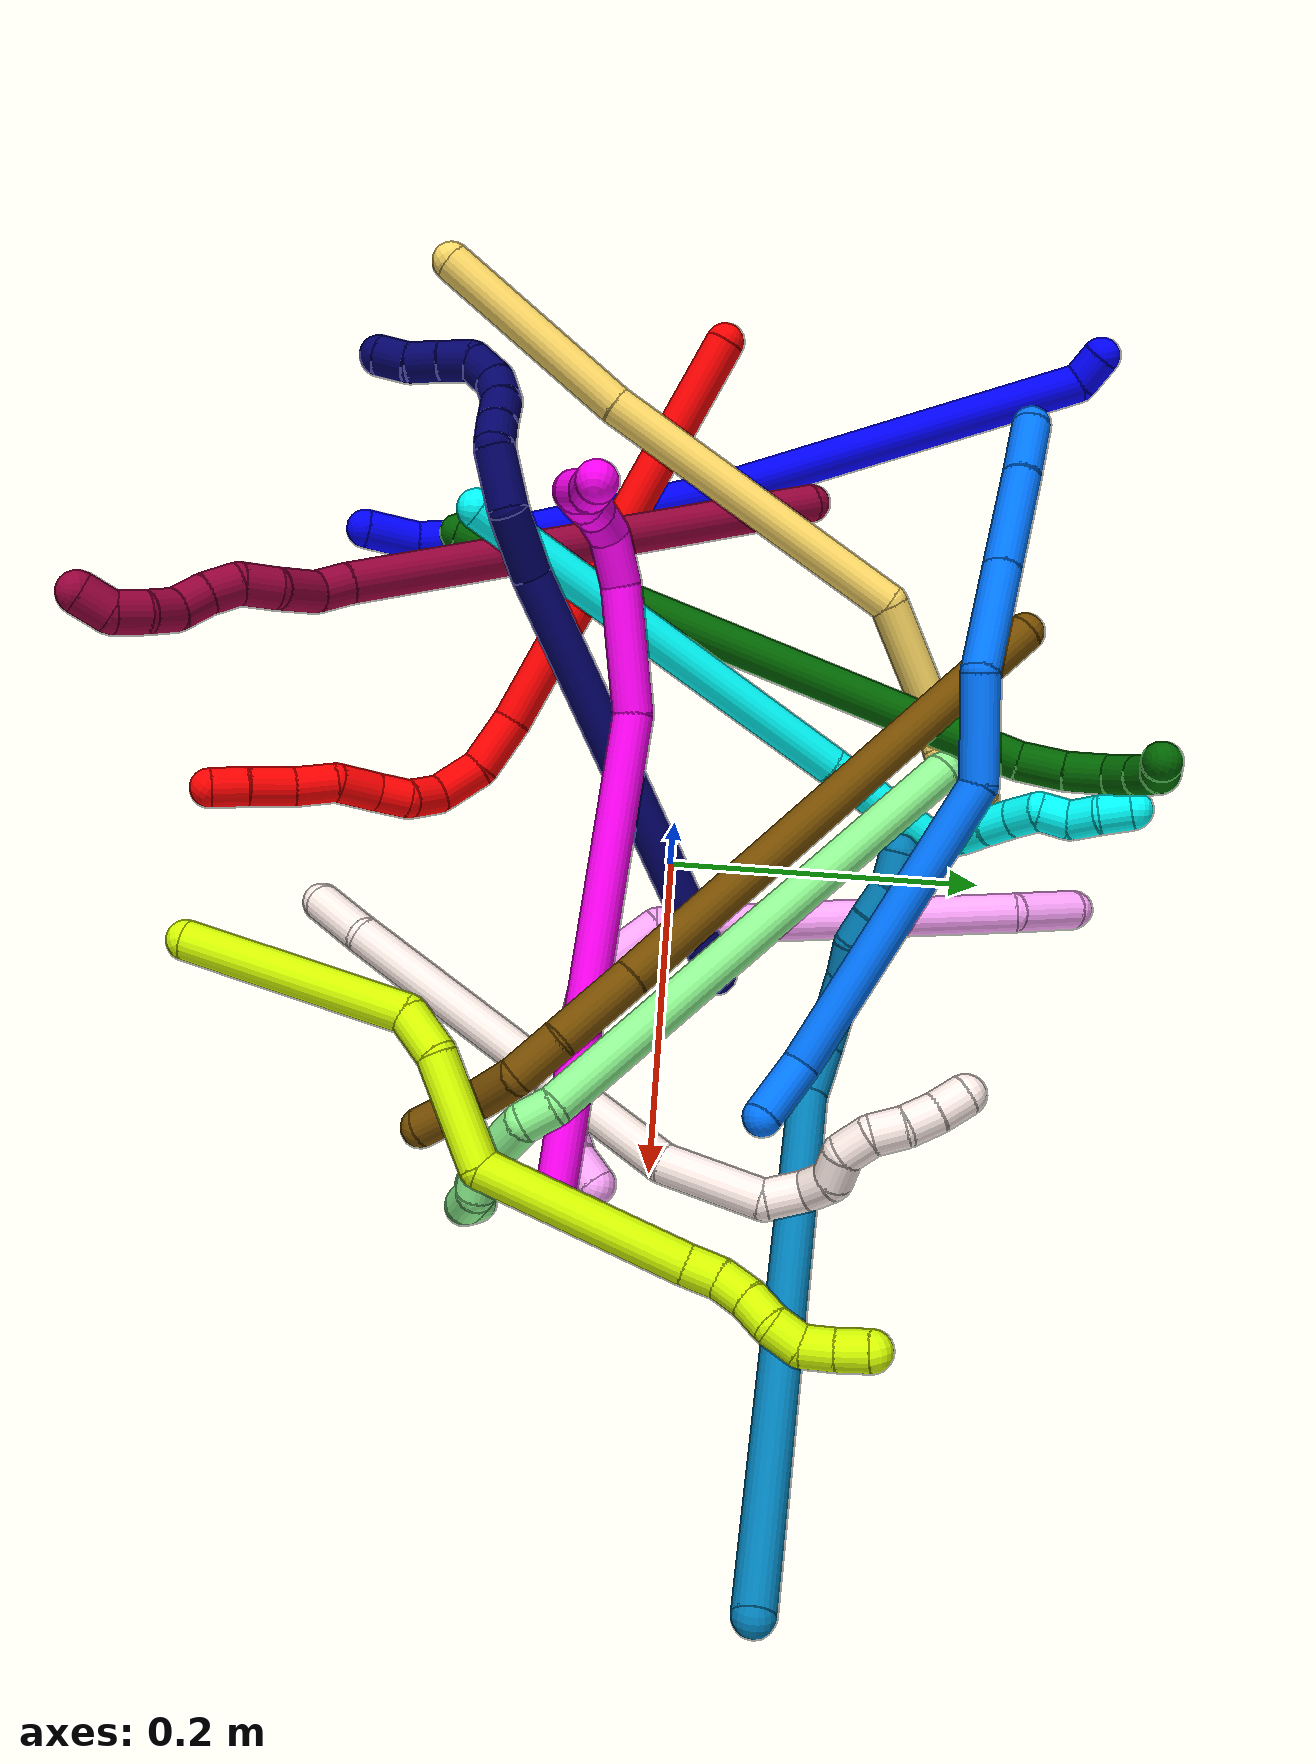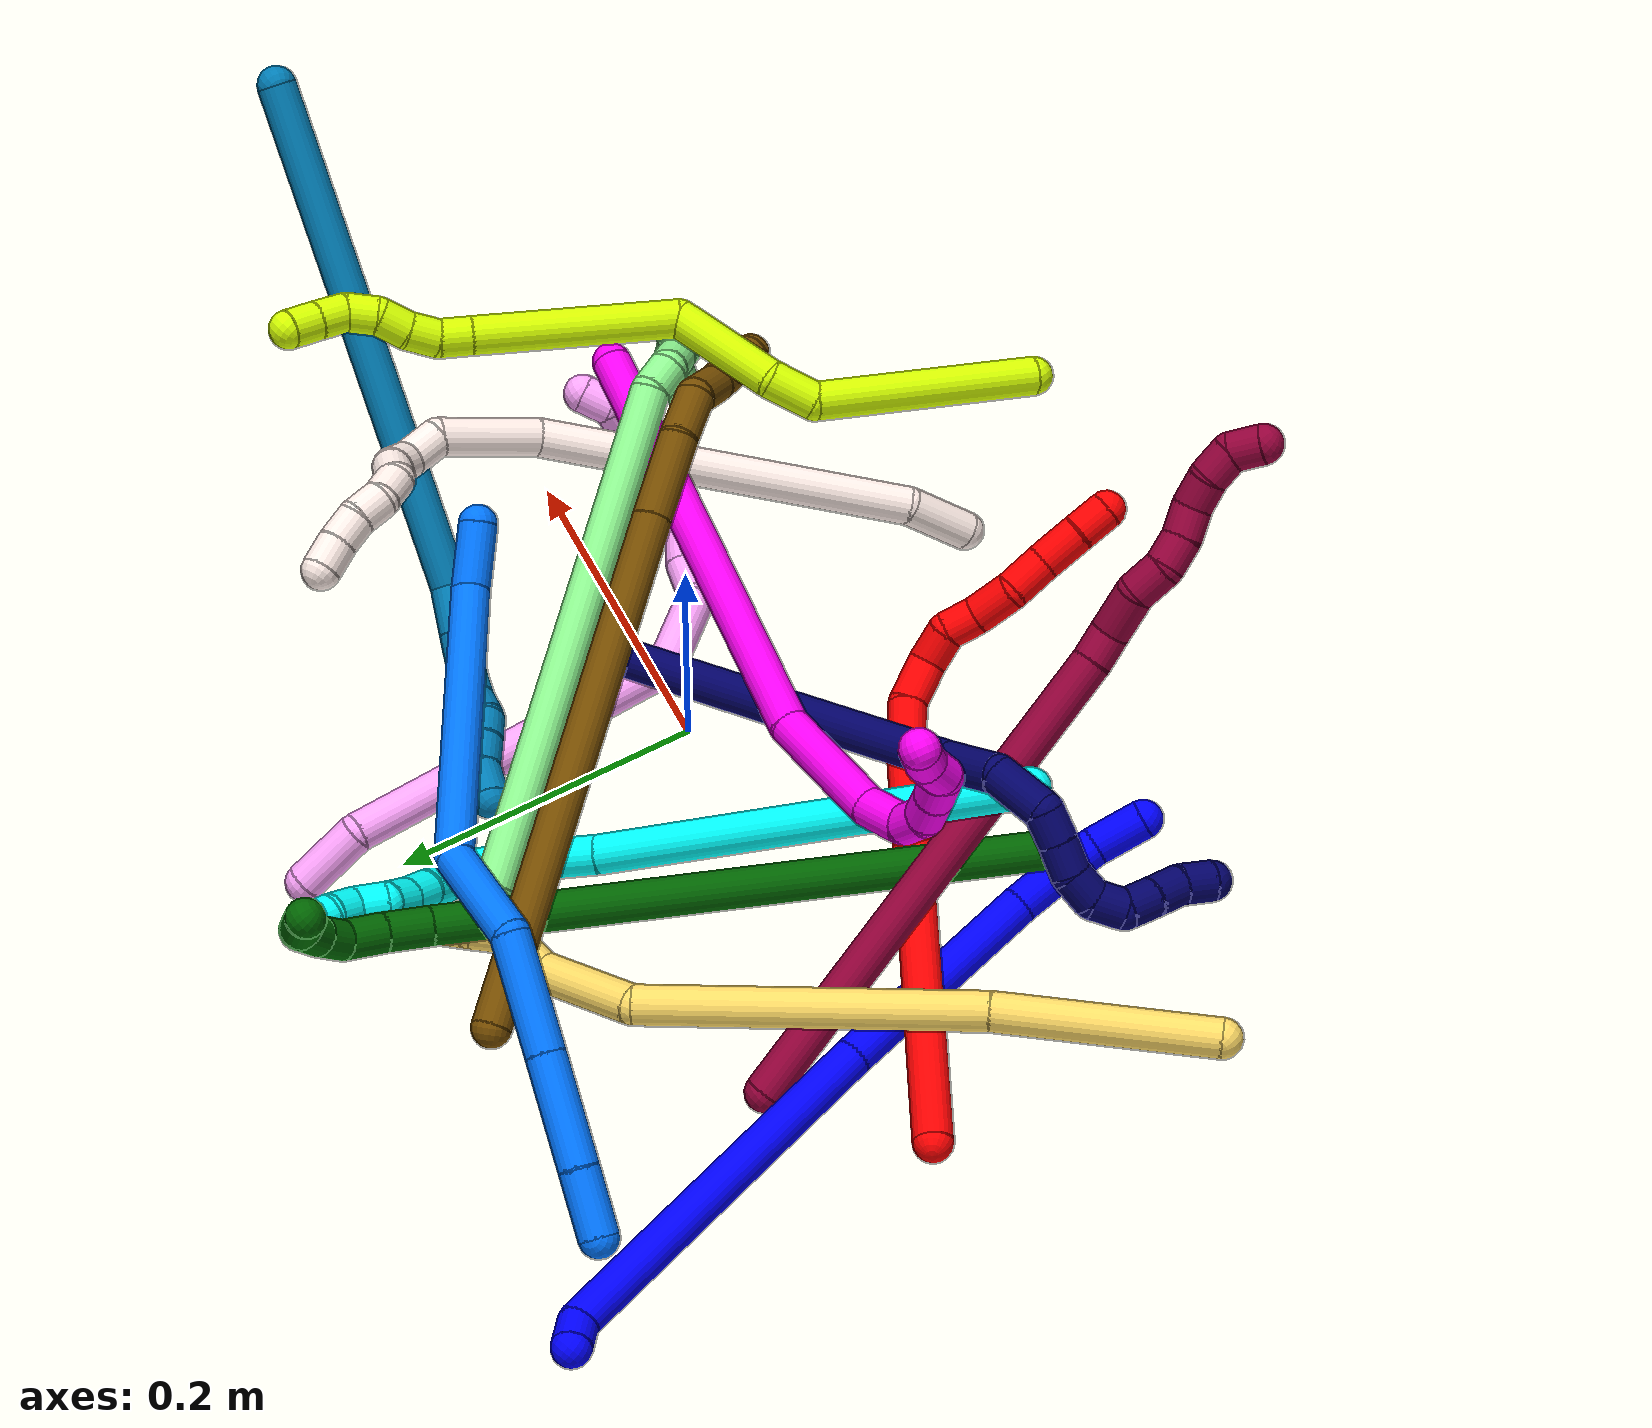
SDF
<sdf version="1.7">
 <world name="default">
  <plugin name="TubeGeneratorPlugin" filename="libtube_generator_plugin.so"/>
  <model name="photoneo_s_sensor">
   <static>1</static>
   <pose>0 0 2 1.57079 1.57079 3.14159</pose>
   <link name="link">
    <inertial><mass>0.1</mass></inertial>
    <sensor name="sensor" type="depth">
     <update_rate>30</update_rate>
     <camera>
      <horizontal_fov>1.22</horizontal_fov>
      <image><width>1920</width><height>1200</height><format>B8G8R8</format></image>
      <clip><near>0.1</near><far>4</far></clip>
      <depth_camera><output>points</output></depth_camera>
     </camera>
     <plugin name="camera_plugin" filename="libgazebo_ros_depth_camera.so">
      <baseline>0.2</baseline>
      <alwaysOn>1</alwaysOn>
      <updateRate>0.0</updateRate>
      <cameraName>camera_ir</cameraName>
      <imageTopicName>/camera/color/image_raw</imageTopicName>
      <cameraInfoTopicName>/camera/color/camera_info</cameraInfoTopicName>
      <depthImageTopicName>/camera/depth/image_raw</depthImageTopicName>
      <depthImageCameraInfoTopicName>/camera/depth/camera_info</depthImageCameraInfoTopicName>
      <pointCloudTopicName>/camera/depth/points</pointCloudTopicName>
      <frameName>fr_optical</frameName>
      <pointCloudCutoff>0.1</pointCloudCutoff>
      <pointCloudCutoffMax>2.0</pointCloudCutoffMax>
      <distortionK1>0</distortionK1>
      <distortionK2>0</distortionK2>
      <distortionK3>0</distortionK3>
      <distortionT1>0</distortionT1>
      <distortionT2>0</distortionT2>
      <CxPrime>0</CxPrime>
      <Cx>0</Cx>
      <Cy>0</Cy>
      <focalLength>0</focalLength>
      <hackBaseline>0</hackBaseline>
     </plugin>
    </sensor>
   </link>
  </model>
  <gravity>0 0 -9.8</gravity>
  <magnetic_field>6e-06 2.3e-05 -4.2e-05</magnetic_field>
  <atmosphere type="adiabatic"/>
  <physics name="default_physics" default="0" type="ode">
   <max_step_size>0.003</max_step_size>
   <real_time_factor>1</real_time_factor>
   <real_time_update_rate>1000</real_time_update_rate>
   <max_contacts>10000</max_contacts>
   <ode>
    <solver>
     <type>quick</type>
     <iters>100</iters>
     <sor>1.3</sor>
     <use_dynamic_moi_rescaling>0</use_dynamic_moi_rescaling>
    </solver>
    <constraints>
     <contact_max_correcting_vel>0</contact_max_correcting_vel>
     <contact_surface_layer>0.001</contact_surface_layer>
     <cfm>0</cfm>
     <erp>0.2</erp>
    </constraints>
   </ode>
  </physics>
  <scene><ambient>0.4 0.4 0.4 1</ambient><background>0.7 0.7 0.7 1</background><shadows>0</shadows></scene>
  <audio><device>default</device></audio>
  <spherical_coordinates>
   <surface_model>EARTH_WGS84</surface_model>
   <latitude_deg>0</latitude_deg>
   <longitude_deg>0</longitude_deg>
   <elevation>0</elevation>
   <heading_deg>0</heading_deg>
  </spherical_coordinates>
  <model name="bin">
   <static>1</static>
   <link name="bottom">
    <collision name="collision-bottom">
     <pose>0 0 -0.01 0 -0 0</pose>
     <geometry><box><size>0.8 0.6 0.02</size></box></geometry>
     <surface>
      <friction><ode><mu>100</mu><mu2>100</mu2></ode></friction>
      <contact><collide_bitmask>65535</collide_bitmask></contact>
     </surface>
    </collision>
   </link>
   <link name="west_wall">
    <collision name="collision-west_wall">
     <pose>-0.41 0 0.1 0 -0 0</pose>
     <geometry><box><size>0.02 0.6 0.2</size></box></geometry>
     <surface>
      <friction><ode><mu>100</mu><mu2>100</mu2></ode></friction>
      <contact><collide_bitmask>65535</collide_bitmask></contact>
     </surface>
    </collision>
   </link>
   <link name="east_wall">
    <collision name="collision-east_wall">
     <pose>0.41 0 0.1 0 -0 0</pose>
     <geometry><box><size>0.02 0.6 0.2</size></box></geometry>
     <surface>
      <friction><ode><mu>100</mu><mu2>100</mu2></ode></friction>
      <contact><collide_bitmask>65535</collide_bitmask></contact>
     </surface>
    </collision>
   </link>
   <link name="south_wall">
    <collision name="collision-south_wall">
     <pose>0 -0.31 0.1 0 -0 0</pose>
     <geometry><box><size>0.8 0.02 0.2</size></box></geometry>
     <surface>
      <friction><ode><mu>100</mu><mu2>100</mu2></ode></friction>
      <contact><collide_bitmask>65535</collide_bitmask></contact>
     </surface>
    </collision>
   </link>
   <link name="north_wall">
    <collision name="collision-north_wall">
     <pose>0 0.31 0.1 0 -0 0</pose>
     <geometry><box><size>0.8 0.02 0.2</size></box></geometry>
     <surface>
      <friction><ode><mu>100</mu><mu2>100</mu2></ode></friction>
      <contact><collide_bitmask>65535</collide_bitmask></contact>
     </surface>
    </collision>
   </link>
  </model>
  <model name="1">
   <static>0</static>
   <link name="1">
    <collision name="collision-cylinder-e_1_1_4">
     <pose>-0.003978 -0.00771 -0.005909 2.22469 -0.388654 -0.758919</pose>
     <geometry><cylinder><radius>0.0125</radius><length>0.020993</length></cylinder></geometry>
     <surface>
      <friction><ode><mu>1.16</mu><mu2>1.16</mu2><slip1>0</slip1><slip2>0</slip2></ode></friction>
      <contact><ode><kp>1e+06</kp><kd>1</kd><max_vel>0</max_vel><min_depth>0.001</min_depth></ode></contact>
     </surface>
    </collision>
    <visual name="visual-cylinder-e_1_1_4">
     <pose>-0.003978 -0.00771 -0.005909 2.22469 -0.388654 -0.758919</pose>
     <geometry><cylinder><radius>0.0125</radius><length>0.020993</length></cylinder></geometry>
     <material><ambient>0 0 1 1</ambient></material>
    </visual>
    <collision name="collision-cylinder-e_2_4_5">
     <pose>0.000942 -0.066885 -0.120306 2.69865 0.073965 0.325731</pose>
     <geometry><cylinder><radius>0.0125</radius><length>0.240812</length></cylinder></geometry>
     <surface>
      <friction><ode><mu>1.16</mu><mu2>1.16</mu2><slip1>0</slip1><slip2>0</slip2></ode></friction>
      <contact><ode><kp>1e+06</kp><kd>1</kd><max_vel>0</max_vel><min_depth>0.001</min_depth></ode></contact>
     </surface>
    </collision>
    <visual name="visual-cylinder-e_2_4_5">
     <pose>0.000942 -0.066885 -0.120306 2.69865 0.073965 0.325731</pose>
     <geometry><cylinder><radius>0.0125</radius><length>0.240812</length></cylinder></geometry>
     <material><ambient>0 0 1 1</ambient></material>
    </visual>
    <collision name="collision-cylinder-e_3_5_6">
     <pose>0.018374 -0.141351 -0.296509 2.81414 0.11877 0.690915</pose>
     <geometry><cylinder><radius>0.0125</radius><length>0.144044</length></cylinder></geometry>
     <surface>
      <friction><ode><mu>1.16</mu><mu2>1.16</mu2><slip1>0</slip1><slip2>0</slip2></ode></friction>
      <contact><ode><kp>1e+06</kp><kd>1</kd><max_vel>0</max_vel><min_depth>0.001</min_depth></ode></contact>
     </surface>
    </collision>
    <visual name="visual-cylinder-e_3_5_6">
     <pose>0.018374 -0.141351 -0.296509 2.81414 0.11877 0.690915</pose>
     <geometry><cylinder><radius>0.0125</radius><length>0.144044</length></cylinder></geometry>
     <material><ambient>0 0 1 1</ambient></material>
    </visual>
    <collision name="collision-cylinder-e_4_6_7">
     <pose>0.029696 -0.166429 -0.377815 2.98997 0.200029 1.84575</pose>
     <geometry><cylinder><radius>0.0125</radius><length>0.028056</length></cylinder></geometry>
     <surface>
      <friction><ode><mu>1.16</mu><mu2>1.16</mu2><slip1>0</slip1><slip2>0</slip2></ode></friction>
      <contact><ode><kp>1e+06</kp><kd>1</kd><max_vel>0</max_vel><min_depth>0.001</min_depth></ode></contact>
     </surface>
    </collision>
    <visual name="visual-cylinder-e_4_6_7">
     <pose>0.029696 -0.166429 -0.377815 2.98997 0.200029 1.84575</pose>
     <geometry><cylinder><radius>0.0125</radius><length>0.028056</length></cylinder></geometry>
     <material><ambient>0 0 1 1</ambient></material>
    </visual>
    <collision name="collision-cylinder-e_5_7_8">
     <pose>0.036235 -0.171297 -0.406547 2.95928 0.239063 1.84048</pose>
     <geometry><cylinder><radius>0.0125</radius><length>0.031695</length></cylinder></geometry>
     <surface>
      <friction><ode><mu>1.16</mu><mu2>1.16</mu2><slip1>0</slip1><slip2>0</slip2></ode></friction>
      <contact><ode><kp>1e+06</kp><kd>1</kd><max_vel>0</max_vel><min_depth>0.001</min_depth></ode></contact>
     </surface>
    </collision>
    <visual name="visual-cylinder-e_5_7_8">
     <pose>0.036235 -0.171297 -0.406547 2.95928 0.239063 1.84048</pose>
     <geometry><cylinder><radius>0.0125</radius><length>0.031695</length></cylinder></geometry>
     <material><ambient>0 0 1 1</ambient></material>
    </visual>
    <collision name="collision-cylinder-e_6_8_2">
     <pose>0.046728 -0.172669 -0.437449 -3.05175 0.402647 -2.70799</pose>
     <geometry><cylinder><radius>0.0125</radius><length>0.0344</length></cylinder></geometry>
     <surface>
      <friction><ode><mu>1.16</mu><mu2>1.16</mu2><slip1>0</slip1><slip2>0</slip2></ode></friction>
      <contact><ode><kp>1e+06</kp><kd>1</kd><max_vel>0</max_vel><min_depth>0.001</min_depth></ode></contact>
     </surface>
    </collision>
    <visual name="visual-cylinder-e_6_8_2">
     <pose>0.046728 -0.172669 -0.437449 -3.05175 0.402647 -2.70799</pose>
     <geometry><cylinder><radius>0.0125</radius><length>0.0344</length></cylinder></geometry>
     <material><ambient>0 0 1 1</ambient></material>
    </visual>
    <collision name="collision-sphere-2">
     <pose>0.053468 -0.171249 -0.45321 0 -0 0</pose>
     <geometry><sphere><radius>0.0125</radius></sphere></geometry>
     <surface>
      <friction><ode><mu>1.16</mu><mu2>1.16</mu2><slip1>0</slip1><slip2>0</slip2></ode></friction>
      <contact><ode><kp>1e+06</kp><kd>1</kd><max_vel>0</max_vel><min_depth>0.001</min_depth></ode></contact>
     </surface>
    </collision>
    <visual name="visual-sphere-2">
     <pose>0.053468 -0.171249 -0.45321 0 -0 0</pose>
     <geometry><sphere><radius>0.0125</radius></sphere></geometry>
     <material><ambient>0 0 1 1</ambient></material>
    </visual>
    <collision name="collision-sphere-4">
     <pose>-0.007955 -0.01542 -0.011817 0 -0 0</pose>
     <geometry><sphere><radius>0.0125</radius></sphere></geometry>
     <surface>
      <friction><ode><mu>1.16</mu><mu2>1.16</mu2><slip1>0</slip1><slip2>0</slip2></ode></friction>
      <contact><ode><kp>1e+06</kp><kd>1</kd><max_vel>0</max_vel><min_depth>0.001</min_depth></ode></contact>
     </surface>
    </collision>
    <visual name="visual-sphere-4">
     <pose>-0.007955 -0.01542 -0.011817 0 -0 0</pose>
     <geometry><sphere><radius>0.0125</radius></sphere></geometry>
     <material><ambient>0 0 1 1</ambient></material>
    </visual>
    <collision name="collision-sphere-1">
     <geometry><sphere><radius>0.0125</radius></sphere></geometry>
     <surface>
      <friction><ode><mu>1.16</mu><mu2>1.16</mu2><slip1>0</slip1><slip2>0</slip2></ode></friction>
      <contact><ode><kp>1e+06</kp><kd>1</kd><max_vel>0</max_vel><min_depth>0.001</min_depth></ode></contact>
     </surface>
    </collision>
    <visual name="visual-sphere-1">
     <geometry><sphere><radius>0.0125</radius></sphere></geometry>
     <material><ambient>0 0 1 1</ambient></material>
    </visual>
    <collision name="collision-sphere-8">
     <pose>0.039988 -0.174089 -0.421689 0 -0 0</pose>
     <geometry><sphere><radius>0.0125</radius></sphere></geometry>
     <surface>
      <friction><ode><mu>1.16</mu><mu2>1.16</mu2><slip1>0</slip1><slip2>0</slip2></ode></friction>
      <contact><ode><kp>1e+06</kp><kd>1</kd><max_vel>0</max_vel><min_depth>0.001</min_depth></ode></contact>
     </surface>
    </collision>
    <visual name="visual-sphere-8">
     <pose>0.039988 -0.174089 -0.421689 0 -0 0</pose>
     <geometry><sphere><radius>0.0125</radius></sphere></geometry>
     <material><ambient>0 0 1 1</ambient></material>
    </visual>
    <collision name="collision-sphere-5">
     <pose>0.00984 -0.11835 -0.228794 0 -0 0</pose>
     <geometry><sphere><radius>0.0125</radius></sphere></geometry>
     <surface>
      <friction><ode><mu>1.16</mu><mu2>1.16</mu2><slip1>0</slip1><slip2>0</slip2></ode></friction>
      <contact><ode><kp>1e+06</kp><kd>1</kd><max_vel>0</max_vel><min_depth>0.001</min_depth></ode></contact>
     </surface>
    </collision>
    <visual name="visual-sphere-5">
     <pose>0.00984 -0.11835 -0.228794 0 -0 0</pose>
     <geometry><sphere><radius>0.0125</radius></sphere></geometry>
     <material><ambient>0 0 1 1</ambient></material>
    </visual>
    <collision name="collision-sphere-6">
     <pose>0.026908 -0.164353 -0.364224 0 -0 0</pose>
     <geometry><sphere><radius>0.0125</radius></sphere></geometry>
     <surface>
      <friction><ode><mu>1.16</mu><mu2>1.16</mu2><slip1>0</slip1><slip2>0</slip2></ode></friction>
      <contact><ode><kp>1e+06</kp><kd>1</kd><max_vel>0</max_vel><min_depth>0.001</min_depth></ode></contact>
     </surface>
    </collision>
    <visual name="visual-sphere-6">
     <pose>0.026908 -0.164353 -0.364224 0 -0 0</pose>
     <geometry><sphere><radius>0.0125</radius></sphere></geometry>
     <material><ambient>0 0 1 1</ambient></material>
    </visual>
    <collision name="collision-sphere-7">
     <pose>0.032483 -0.168506 -0.391405 0 -0 0</pose>
     <geometry><sphere><radius>0.0125</radius></sphere></geometry>
     <surface>
      <friction><ode><mu>1.16</mu><mu2>1.16</mu2><slip1>0</slip1><slip2>0</slip2></ode></friction>
      <contact><ode><kp>1e+06</kp><kd>1</kd><max_vel>0</max_vel><min_depth>0.001</min_depth></ode></contact>
     </surface>
    </collision>
    <visual name="visual-sphere-7">
     <pose>0.032483 -0.168506 -0.391405 0 -0 0</pose>
     <geometry><sphere><radius>0.0125</radius></sphere></geometry>
     <material><ambient>0 0 1 1</ambient></material>
    </visual>
    <inertial>
     <pose>0.012758 -0.105336 -0.220678 0 -0 0</pose>
     <mass>0.5</mass>
     <inertia>
      <ixx>0.001842</ixx>
      <ixy>0</ixy>
      <ixz>0</ixz>
      <iyy>-0.00064</iyy>
      <iyz>0</iyz>
      <izz>0.00043</izz>
     </inertia>
    </inertial>
   </link>
   <pose>-0.34319 0.253969 0.045245 1.92049 0.121931 -2.73501</pose>
  </model>
  <model name="2">
   <static>0</static>
   <link name="2">
    <collision name="collision-cylinder-e_1_1_4">
     <pose>0.037554 0.015673 -0.133207 -3.02447 0.272998 -2.33475</pose>
     <geometry><cylinder><radius>0.0125</radius><length>0.278568</length></cylinder></geometry>
     <surface>
      <friction><ode><mu>1.16</mu><mu2>1.16</mu2><slip1>0</slip1><slip2>0</slip2></ode></friction>
      <contact><ode><kp>1e+06</kp><kd>1</kd><max_vel>0</max_vel><min_depth>0.001</min_depth></ode></contact>
     </surface>
    </collision>
    <visual name="visual-cylinder-e_1_1_4">
     <pose>0.037554 0.015673 -0.133207 -3.02447 0.272998 -2.33475</pose>
     <geometry><cylinder><radius>0.0125</radius><length>0.278568</length></cylinder></geometry>
     <material><ambient>1 0 0 1</ambient></material>
    </visual>
    <collision name="collision-cylinder-e_2_4_5">
     <pose>0.083387 0.032189 -0.283261 -3.09157 0.45632 -2.92694</pose>
     <geometry><cylinder><radius>0.0125</radius><length>0.03758</length></cylinder></geometry>
     <surface>
      <friction><ode><mu>1.16</mu><mu2>1.16</mu2><slip1>0</slip1><slip2>0</slip2></ode></friction>
      <contact><ode><kp>1e+06</kp><kd>1</kd><max_vel>0</max_vel><min_depth>0.001</min_depth></ode></contact>
     </surface>
    </collision>
    <visual name="visual-cylinder-e_2_4_5">
     <pose>0.083387 0.032189 -0.283261 -3.09157 0.45632 -2.92694</pose>
     <geometry><cylinder><radius>0.0125</radius><length>0.03758</length></cylinder></geometry>
     <material><ambient>1 0 0 1</ambient></material>
    </visual>
    <collision name="collision-cylinder-e_3_5_6">
     <pose>0.098514 0.027727 -0.313196 2.7565 0.451449 1.73377</pose>
     <geometry><cylinder><radius>0.0125</radius><length>0.031391</length></cylinder></geometry>
     <surface>
      <friction><ode><mu>1.16</mu><mu2>1.16</mu2><slip1>0</slip1><slip2>0</slip2></ode></friction>
      <contact><ode><kp>1e+06</kp><kd>1</kd><max_vel>0</max_vel><min_depth>0.001</min_depth></ode></contact>
     </surface>
    </collision>
    <visual name="visual-cylinder-e_3_5_6">
     <pose>0.098514 0.027727 -0.313196 2.7565 0.451449 1.73377</pose>
     <geometry><cylinder><radius>0.0125</radius><length>0.031391</length></cylinder></geometry>
     <material><ambient>1 0 0 1</ambient></material>
    </visual>
    <collision name="collision-cylinder-e_4_6_7">
     <pose>0.115811 0.016977 -0.329766 2.13969 1.01684 1.58844</pose>
     <geometry><cylinder><radius>0.0125</radius><length>0.024573</length></cylinder></geometry>
     <surface>
      <friction><ode><mu>1.16</mu><mu2>1.16</mu2><slip1>0</slip1><slip2>0</slip2></ode></friction>
      <contact><ode><kp>1e+06</kp><kd>1</kd><max_vel>0</max_vel><min_depth>0.001</min_depth></ode></contact>
     </surface>
    </collision>
    <visual name="visual-cylinder-e_4_6_7">
     <pose>0.115811 0.016977 -0.329766 2.13969 1.01684 1.58844</pose>
     <geometry><cylinder><radius>0.0125</radius><length>0.024573</length></cylinder></geometry>
     <material><ambient>1 0 0 1</ambient></material>
    </visual>
    <collision name="collision-cylinder-e_5_7_8">
     <pose>0.131283 0.00254 -0.335876 1.85521 0.492217 0.646768</pose>
     <geometry><cylinder><radius>0.0125</radius><length>0.021259</length></cylinder></geometry>
     <surface>
      <friction><ode><mu>1.16</mu><mu2>1.16</mu2><slip1>0</slip1><slip2>0</slip2></ode></friction>
      <contact><ode><kp>1e+06</kp><kd>1</kd><max_vel>0</max_vel><min_depth>0.001</min_depth></ode></contact>
     </surface>
    </collision>
    <visual name="visual-cylinder-e_5_7_8">
     <pose>0.131283 0.00254 -0.335876 1.85521 0.492217 0.646768</pose>
     <geometry><cylinder><radius>0.0125</radius><length>0.021259</length></cylinder></geometry>
     <material><ambient>1 0 0 1</ambient></material>
    </visual>
    <collision name="collision-cylinder-e_6_8_9">
     <pose>0.145633 -0.016846 -0.340169 1.72958 0.724985 0.83706</pose>
     <geometry><cylinder><radius>0.0125</radius><length>0.028128</length></cylinder></geometry>
     <surface>
      <friction><ode><mu>1.16</mu><mu2>1.16</mu2><slip1>0</slip1><slip2>0</slip2></ode></friction>
      <contact><ode><kp>1e+06</kp><kd>1</kd><max_vel>0</max_vel><min_depth>0.001</min_depth></ode></contact>
     </surface>
    </collision>
    <visual name="visual-cylinder-e_6_8_9">
     <pose>0.145633 -0.016846 -0.340169 1.72958 0.724985 0.83706</pose>
     <geometry><cylinder><radius>0.0125</radius><length>0.028128</length></cylinder></geometry>
     <material><ambient>1 0 0 1</ambient></material>
    </visual>
    <collision name="collision-cylinder-e_7_9_10">
     <pose>0.161746 -0.036376 -0.348714 2.21635 0.535578 1.00595</pose>
     <geometry><cylinder><radius>0.0125</radius><length>0.026597</length></cylinder></geometry>
     <surface>
      <friction><ode><mu>1.16</mu><mu2>1.16</mu2><slip1>0</slip1><slip2>0</slip2></ode></friction>
      <contact><ode><kp>1e+06</kp><kd>1</kd><max_vel>0</max_vel><min_depth>0.001</min_depth></ode></contact>
     </surface>
    </collision>
    <visual name="visual-cylinder-e_7_9_10">
     <pose>0.161746 -0.036376 -0.348714 2.21635 0.535578 1.00595</pose>
     <geometry><cylinder><radius>0.0125</radius><length>0.026597</length></cylinder></geometry>
     <material><ambient>1 0 0 1</ambient></material>
    </visual>
    <collision name="collision-cylinder-e_8_10_11">
     <pose>0.176954 -0.055947 -0.361195 2.06333 0.618129 0.980512</pose>
     <geometry><cylinder><radius>0.0125</radius><length>0.029066</length></cylinder></geometry>
     <surface>
      <friction><ode><mu>1.16</mu><mu2>1.16</mu2><slip1>0</slip1><slip2>0</slip2></ode></friction>
      <contact><ode><kp>1e+06</kp><kd>1</kd><max_vel>0</max_vel><min_depth>0.001</min_depth></ode></contact>
     </surface>
    </collision>
    <visual name="visual-cylinder-e_8_10_11">
     <pose>0.176954 -0.055947 -0.361195 2.06333 0.618129 0.980512</pose>
     <geometry><cylinder><radius>0.0125</radius><length>0.029066</length></cylinder></geometry>
     <material><ambient>1 0 0 1</ambient></material>
    </visual>
    <collision name="collision-cylinder-e_9_11_2">
     <pose>0.191239 -0.074646 -0.372064 2.13838 0.539167 0.933456</pose>
     <geometry><cylinder><radius>0.0125</radius><length>0.022838</length></cylinder></geometry>
     <surface>
      <friction><ode><mu>1.16</mu><mu2>1.16</mu2><slip1>0</slip1><slip2>0</slip2></ode></friction>
      <contact><ode><kp>1e+06</kp><kd>1</kd><max_vel>0</max_vel><min_depth>0.001</min_depth></ode></contact>
     </surface>
    </collision>
    <visual name="visual-cylinder-e_9_11_2">
     <pose>0.191239 -0.074646 -0.372064 2.13838 0.539167 0.933456</pose>
     <geometry><cylinder><radius>0.0125</radius><length>0.022838</length></cylinder></geometry>
     <material><ambient>1 0 0 1</ambient></material>
    </visual>
    <collision name="collision-sphere-2">
     <pose>0.197102 -0.082908 -0.377332 0 -0 0</pose>
     <geometry><sphere><radius>0.0125</radius></sphere></geometry>
     <surface>
      <friction><ode><mu>1.16</mu><mu2>1.16</mu2><slip1>0</slip1><slip2>0</slip2></ode></friction>
      <contact><ode><kp>1e+06</kp><kd>1</kd><max_vel>0</max_vel><min_depth>0.001</min_depth></ode></contact>
     </surface>
    </collision>
    <visual name="visual-sphere-2">
     <pose>0.197102 -0.082908 -0.377332 0 -0 0</pose>
     <geometry><sphere><radius>0.0125</radius></sphere></geometry>
     <material><ambient>1 0 0 1</ambient></material>
    </visual>
    <collision name="collision-sphere-11">
     <pose>0.185376 -0.066383 -0.366796 0 -0 0</pose>
     <geometry><sphere><radius>0.0125</radius></sphere></geometry>
     <surface>
      <friction><ode><mu>1.16</mu><mu2>1.16</mu2><slip1>0</slip1><slip2>0</slip2></ode></friction>
      <contact><ode><kp>1e+06</kp><kd>1</kd><max_vel>0</max_vel><min_depth>0.001</min_depth></ode></contact>
     </surface>
    </collision>
    <visual name="visual-sphere-11">
     <pose>0.185376 -0.066383 -0.366796 0 -0 0</pose>
     <geometry><sphere><radius>0.0125</radius></sphere></geometry>
     <material><ambient>1 0 0 1</ambient></material>
    </visual>
    <collision name="collision-sphere-10">
     <pose>0.168532 -0.045511 -0.355595 0 -0 0</pose>
     <geometry><sphere><radius>0.0125</radius></sphere></geometry>
     <surface>
      <friction><ode><mu>1.16</mu><mu2>1.16</mu2><slip1>0</slip1><slip2>0</slip2></ode></friction>
      <contact><ode><kp>1e+06</kp><kd>1</kd><max_vel>0</max_vel><min_depth>0.001</min_depth></ode></contact>
     </surface>
    </collision>
    <visual name="visual-sphere-10">
     <pose>0.168532 -0.045511 -0.355595 0 -0 0</pose>
     <geometry><sphere><radius>0.0125</radius></sphere></geometry>
     <material><ambient>1 0 0 1</ambient></material>
    </visual>
    <collision name="collision-sphere-9">
     <pose>0.154959 -0.027241 -0.341834 0 -0 0</pose>
     <geometry><sphere><radius>0.0125</radius></sphere></geometry>
     <surface>
      <friction><ode><mu>1.16</mu><mu2>1.16</mu2><slip1>0</slip1><slip2>0</slip2></ode></friction>
      <contact><ode><kp>1e+06</kp><kd>1</kd><max_vel>0</max_vel><min_depth>0.001</min_depth></ode></contact>
     </surface>
    </collision>
    <visual name="visual-sphere-9">
     <pose>0.154959 -0.027241 -0.341834 0 -0 0</pose>
     <geometry><sphere><radius>0.0125</radius></sphere></geometry>
     <material><ambient>1 0 0 1</ambient></material>
    </visual>
    <collision name="collision-sphere-4">
     <pose>0.075107 0.031346 -0.266414 0 -0 0</pose>
     <geometry><sphere><radius>0.0125</radius></sphere></geometry>
     <surface>
      <friction><ode><mu>1.16</mu><mu2>1.16</mu2><slip1>0</slip1><slip2>0</slip2></ode></friction>
      <contact><ode><kp>1e+06</kp><kd>1</kd><max_vel>0</max_vel><min_depth>0.001</min_depth></ode></contact>
     </surface>
    </collision>
    <visual name="visual-sphere-4">
     <pose>0.075107 0.031346 -0.266414 0 -0 0</pose>
     <geometry><sphere><radius>0.0125</radius></sphere></geometry>
     <material><ambient>1 0 0 1</ambient></material>
    </visual>
    <collision name="collision-sphere-1">
     <geometry><sphere><radius>0.0125</radius></sphere></geometry>
     <surface>
      <friction><ode><mu>1.16</mu><mu2>1.16</mu2><slip1>0</slip1><slip2>0</slip2></ode></friction>
      <contact><ode><kp>1e+06</kp><kd>1</kd><max_vel>0</max_vel><min_depth>0.001</min_depth></ode></contact>
     </surface>
    </collision>
    <visual name="visual-sphere-1">
     <geometry><sphere><radius>0.0125</radius></sphere></geometry>
     <material><ambient>1 0 0 1</ambient></material>
    </visual>
    <collision name="collision-sphere-8">
     <pose>0.136306 -0.006452 -0.338505 0 -0 0</pose>
     <geometry><sphere><radius>0.0125</radius></sphere></geometry>
     <surface>
      <friction><ode><mu>1.16</mu><mu2>1.16</mu2><slip1>0</slip1><slip2>0</slip2></ode></friction>
      <contact><ode><kp>1e+06</kp><kd>1</kd><max_vel>0</max_vel><min_depth>0.001</min_depth></ode></contact>
     </surface>
    </collision>
    <visual name="visual-sphere-8">
     <pose>0.136306 -0.006452 -0.338505 0 -0 0</pose>
     <geometry><sphere><radius>0.0125</radius></sphere></geometry>
     <material><ambient>1 0 0 1</ambient></material>
    </visual>
    <collision name="collision-sphere-5">
     <pose>0.091667 0.033032 -0.300107 0 -0 0</pose>
     <geometry><sphere><radius>0.0125</radius></sphere></geometry>
     <surface>
      <friction><ode><mu>1.16</mu><mu2>1.16</mu2><slip1>0</slip1><slip2>0</slip2></ode></friction>
      <contact><ode><kp>1e+06</kp><kd>1</kd><max_vel>0</max_vel><min_depth>0.001</min_depth></ode></contact>
     </surface>
    </collision>
    <visual name="visual-sphere-5">
     <pose>0.091667 0.033032 -0.300107 0 -0 0</pose>
     <geometry><sphere><radius>0.0125</radius></sphere></geometry>
     <material><ambient>1 0 0 1</ambient></material>
    </visual>
    <collision name="collision-sphere-6">
     <pose>0.105362 0.022422 -0.326284 0 -0 0</pose>
     <geometry><sphere><radius>0.0125</radius></sphere></geometry>
     <surface>
      <friction><ode><mu>1.16</mu><mu2>1.16</mu2><slip1>0</slip1><slip2>0</slip2></ode></friction>
      <contact><ode><kp>1e+06</kp><kd>1</kd><max_vel>0</max_vel><min_depth>0.001</min_depth></ode></contact>
     </surface>
    </collision>
    <visual name="visual-sphere-6">
     <pose>0.105362 0.022422 -0.326284 0 -0 0</pose>
     <geometry><sphere><radius>0.0125</radius></sphere></geometry>
     <material><ambient>1 0 0 1</ambient></material>
    </visual>
    <collision name="collision-sphere-7">
     <pose>0.12626 0.011531 -0.333248 0 -0 0</pose>
     <geometry><sphere><radius>0.0125</radius></sphere></geometry>
     <surface>
      <friction><ode><mu>1.16</mu><mu2>1.16</mu2><slip1>0</slip1><slip2>0</slip2></ode></friction>
      <contact><ode><kp>1e+06</kp><kd>1</kd><max_vel>0</max_vel><min_depth>0.001</min_depth></ode></contact>
     </surface>
    </collision>
    <visual name="visual-sphere-7">
     <pose>0.12626 0.011531 -0.333248 0 -0 0</pose>
     <geometry><sphere><radius>0.0125</radius></sphere></geometry>
     <material><ambient>1 0 0 1</ambient></material>
    </visual>
    <inertial>
     <pose>0.080467 0.00429 -0.221332 0 -0 0</pose>
     <mass>0.5</mass>
     <inertia>
      <ixx>-0.00244</ixx>
      <ixy>0</ixy>
      <ixz>0</ixz>
      <iyy>4.1e-05</iyy>
      <iyz>0</iyz>
      <izz>-0.000724</izz>
     </inertia>
    </inertial>
   </link>
   <pose>-0.332411 0.011119 0.053521 -0.001069 -1.14436 -0.56583</pose>
  </model>
  <model name="3">
   <static>0</static>
   <link name="3">
    <collision name="collision-cylinder-e_1_1_4">
     <pose>-0.02797 0.072492 0.114014 -0.566341 -0.204136 0.059591</pose>
     <geometry><cylinder><radius>0.0125</radius><length>0.275947</length></cylinder></geometry>
     <surface>
      <friction><ode><mu>1.16</mu><mu2>1.16</mu2><slip1>0</slip1><slip2>0</slip2></ode></friction>
      <contact><ode><kp>1e+06</kp><kd>1</kd><max_vel>0</max_vel><min_depth>0.001</min_depth></ode></contact>
     </surface>
    </collision>
    <visual name="visual-cylinder-e_1_1_4">
     <pose>-0.02797 0.072492 0.114014 -0.566341 -0.204136 0.059591</pose>
     <geometry><cylinder><radius>0.0125</radius><length>0.275947</length></cylinder></geometry>
     <material><ambient>0.003922 1 0.996078 1</ambient></material>
    </visual>
    <collision name="collision-cylinder-e_2_4_5">
     <pose>-0.059976 0.161079 0.251892 -0.593353 -0.139314 0.042651</pose>
     <geometry><cylinder><radius>0.0125</radius><length>0.058131</length></cylinder></geometry>
     <surface>
      <friction><ode><mu>1.16</mu><mu2>1.16</mu2><slip1>0</slip1><slip2>0</slip2></ode></friction>
      <contact><ode><kp>1e+06</kp><kd>1</kd><max_vel>0</max_vel><min_depth>0.001</min_depth></ode></contact>
     </surface>
    </collision>
    <visual name="visual-cylinder-e_2_4_5">
     <pose>-0.059976 0.161079 0.251892 -0.593353 -0.139314 0.042651</pose>
     <geometry><cylinder><radius>0.0125</radius><length>0.058131</length></cylinder></geometry>
     <material><ambient>0.003922 1 0.996078 1</ambient></material>
    </visual>
    <collision name="collision-cylinder-e_3_5_6">
     <pose>-0.066528 0.183416 0.285948 -0.549578 -0.207411 0.058667</pose>
     <geometry><cylinder><radius>0.0125</radius><length>0.024428</length></cylinder></geometry>
     <surface>
      <friction><ode><mu>1.16</mu><mu2>1.16</mu2><slip1>0</slip1><slip2>0</slip2></ode></friction>
      <contact><ode><kp>1e+06</kp><kd>1</kd><max_vel>0</max_vel><min_depth>0.001</min_depth></ode></contact>
     </surface>
    </collision>
    <visual name="visual-cylinder-e_3_5_6">
     <pose>-0.066528 0.183416 0.285948 -0.549578 -0.207411 0.058667</pose>
     <geometry><cylinder><radius>0.0125</radius><length>0.024428</length></cylinder></geometry>
     <material><ambient>0.003922 1 0.996078 1</ambient></material>
    </visual>
    <collision name="collision-cylinder-e_4_6_7">
     <pose>-0.066678 0.188675 0.30647 0.094968 0.224077 0.010693</pose>
     <geometry><cylinder><radius>0.0125</radius><length>0.021284</length></cylinder></geometry>
     <surface>
      <friction><ode><mu>1.16</mu><mu2>1.16</mu2><slip1>0</slip1><slip2>0</slip2></ode></friction>
      <contact><ode><kp>1e+06</kp><kd>1</kd><max_vel>0</max_vel><min_depth>0.001</min_depth></ode></contact>
     </surface>
    </collision>
    <visual name="visual-cylinder-e_4_6_7">
     <pose>-0.066678 0.188675 0.30647 0.094968 0.224077 0.010693</pose>
     <geometry><cylinder><radius>0.0125</radius><length>0.021284</length></cylinder></geometry>
     <material><ambient>0.003922 1 0.996078 1</ambient></material>
    </visual>
    <collision name="collision-cylinder-e_5_7_8">
     <pose>-0.057084 0.184482 0.322995 0.477916 0.803108 0.206155</pose>
     <geometry><cylinder><radius>0.0125</radius><length>0.020095</length></cylinder></geometry>
     <surface>
      <friction><ode><mu>1.16</mu><mu2>1.16</mu2><slip1>0</slip1><slip2>0</slip2></ode></friction>
      <contact><ode><kp>1e+06</kp><kd>1</kd><max_vel>0</max_vel><min_depth>0.001</min_depth></ode></contact>
     </surface>
    </collision>
    <visual name="visual-cylinder-e_5_7_8">
     <pose>-0.057084 0.184482 0.322995 0.477916 0.803108 0.206155</pose>
     <geometry><cylinder><radius>0.0125</radius><length>0.020095</length></cylinder></geometry>
     <material><ambient>0.003922 1 0.996078 1</ambient></material>
    </visual>
    <collision name="collision-cylinder-e_6_8_9">
     <pose>-0.043386 0.178164 0.3362 0.417429 0.700835 0.154518</pose>
     <geometry><cylinder><radius>0.0125</radius><length>0.020064</length></cylinder></geometry>
     <surface>
      <friction><ode><mu>1.16</mu><mu2>1.16</mu2><slip1>0</slip1><slip2>0</slip2></ode></friction>
      <contact><ode><kp>1e+06</kp><kd>1</kd><max_vel>0</max_vel><min_depth>0.001</min_depth></ode></contact>
     </surface>
    </collision>
    <visual name="visual-cylinder-e_6_8_9">
     <pose>-0.043386 0.178164 0.3362 0.417429 0.700835 0.154518</pose>
     <geometry><cylinder><radius>0.0125</radius><length>0.020064</length></cylinder></geometry>
     <material><ambient>0.003922 1 0.996078 1</ambient></material>
    </visual>
    <collision name="collision-cylinder-e_7_9_10">
     <pose>-0.029577 0.172484 0.349519 0.387093 0.822491 0.170542</pose>
     <geometry><cylinder><radius>0.0125</radius><length>0.020029</length></cylinder></geometry>
     <surface>
      <friction><ode><mu>1.16</mu><mu2>1.16</mu2><slip1>0</slip1><slip2>0</slip2></ode></friction>
      <contact><ode><kp>1e+06</kp><kd>1</kd><max_vel>0</max_vel><min_depth>0.001</min_depth></ode></contact>
     </surface>
    </collision>
    <visual name="visual-cylinder-e_7_9_10">
     <pose>-0.029577 0.172484 0.349519 0.387093 0.822491 0.170542</pose>
     <geometry><cylinder><radius>0.0125</radius><length>0.020029</length></cylinder></geometry>
     <material><ambient>0.003922 1 0.996078 1</ambient></material>
    </visual>
    <collision name="collision-cylinder-e_8_10_11">
     <pose>-0.019598 0.17241 0.365148 -0.261928 0.267093 -0.035388</pose>
     <geometry><cylinder><radius>0.0125</radius><length>0.020007</length></cylinder></geometry>
     <surface>
      <friction><ode><mu>1.16</mu><mu2>1.16</mu2><slip1>0</slip1><slip2>0</slip2></ode></friction>
      <contact><ode><kp>1e+06</kp><kd>1</kd><max_vel>0</max_vel><min_depth>0.001</min_depth></ode></contact>
     </surface>
    </collision>
    <visual name="visual-cylinder-e_8_10_11">
     <pose>-0.019598 0.17241 0.365148 -0.261928 0.267093 -0.035388</pose>
     <geometry><cylinder><radius>0.0125</radius><length>0.020007</length></cylinder></geometry>
     <material><ambient>0.003922 1 0.996078 1</ambient></material>
    </visual>
    <collision name="collision-cylinder-e_9_11_12">
     <pose>-0.010621 0.172791 0.381918 0.276864 0.6857 0.09938</pose>
     <geometry><cylinder><radius>0.0125</radius><length>0.020015</length></cylinder></geometry>
     <surface>
      <friction><ode><mu>1.16</mu><mu2>1.16</mu2><slip1>0</slip1><slip2>0</slip2></ode></friction>
      <contact><ode><kp>1e+06</kp><kd>1</kd><max_vel>0</max_vel><min_depth>0.001</min_depth></ode></contact>
     </surface>
    </collision>
    <visual name="visual-cylinder-e_9_11_12">
     <pose>-0.010621 0.172791 0.381918 0.276864 0.6857 0.09938</pose>
     <geometry><cylinder><radius>0.0125</radius><length>0.020015</length></cylinder></geometry>
     <material><ambient>0.003922 1 0.996078 1</ambient></material>
    </visual>
    <collision name="collision-cylinder-e_10_12_2">
     <pose>-0.00047 0.168837 0.398429 0.199983 0.391261 0.039757</pose>
     <geometry><cylinder><radius>0.0125</radius><length>0.02</length></cylinder></geometry>
     <surface>
      <friction><ode><mu>1.16</mu><mu2>1.16</mu2><slip1>0</slip1><slip2>0</slip2></ode></friction>
      <contact><ode><kp>1e+06</kp><kd>1</kd><max_vel>0</max_vel><min_depth>0.001</min_depth></ode></contact>
     </surface>
    </collision>
    <visual name="visual-cylinder-e_10_12_2">
     <pose>-0.00047 0.168837 0.398429 0.199983 0.391261 0.039757</pose>
     <geometry><cylinder><radius>0.0125</radius><length>0.02</length></cylinder></geometry>
     <material><ambient>0.003922 1 0.996078 1</ambient></material>
    </visual>
    <collision name="collision-sphere-2">
     <pose>0.003343 0.167001 0.407489 0 -0 0</pose>
     <geometry><sphere><radius>0.0125</radius></sphere></geometry>
     <surface>
      <friction><ode><mu>1.16</mu><mu2>1.16</mu2><slip1>0</slip1><slip2>0</slip2></ode></friction>
      <contact><ode><kp>1e+06</kp><kd>1</kd><max_vel>0</max_vel><min_depth>0.001</min_depth></ode></contact>
     </surface>
    </collision>
    <visual name="visual-sphere-2">
     <pose>0.003343 0.167001 0.407489 0 -0 0</pose>
     <geometry><sphere><radius>0.0125</radius></sphere></geometry>
     <material><ambient>0.003922 1 0.996078 1</ambient></material>
    </visual>
    <collision name="collision-sphere-12">
     <pose>-0.004284 0.170674 0.389369 0 -0 0</pose>
     <geometry><sphere><radius>0.0125</radius></sphere></geometry>
     <surface>
      <friction><ode><mu>1.16</mu><mu2>1.16</mu2><slip1>0</slip1><slip2>0</slip2></ode></friction>
      <contact><ode><kp>1e+06</kp><kd>1</kd><max_vel>0</max_vel><min_depth>0.001</min_depth></ode></contact>
     </surface>
    </collision>
    <visual name="visual-sphere-12">
     <pose>-0.004284 0.170674 0.389369 0 -0 0</pose>
     <geometry><sphere><radius>0.0125</radius></sphere></geometry>
     <material><ambient>0.003922 1 0.996078 1</ambient></material>
    </visual>
    <collision name="collision-sphere-11">
     <pose>-0.016958 0.174908 0.374467 0 -0 0</pose>
     <geometry><sphere><radius>0.0125</radius></sphere></geometry>
     <surface>
      <friction><ode><mu>1.16</mu><mu2>1.16</mu2><slip1>0</slip1><slip2>0</slip2></ode></friction>
      <contact><ode><kp>1e+06</kp><kd>1</kd><max_vel>0</max_vel><min_depth>0.001</min_depth></ode></contact>
     </surface>
    </collision>
    <visual name="visual-sphere-11">
     <pose>-0.016958 0.174908 0.374467 0 -0 0</pose>
     <geometry><sphere><radius>0.0125</radius></sphere></geometry>
     <material><ambient>0.003922 1 0.996078 1</ambient></material>
    </visual>
    <collision name="collision-sphere-10">
     <pose>-0.022238 0.169911 0.355828 0 -0 0</pose>
     <geometry><sphere><radius>0.0125</radius></sphere></geometry>
     <surface>
      <friction><ode><mu>1.16</mu><mu2>1.16</mu2><slip1>0</slip1><slip2>0</slip2></ode></friction>
      <contact><ode><kp>1e+06</kp><kd>1</kd><max_vel>0</max_vel><min_depth>0.001</min_depth></ode></contact>
     </surface>
    </collision>
    <visual name="visual-sphere-10">
     <pose>-0.022238 0.169911 0.355828 0 -0 0</pose>
     <geometry><sphere><radius>0.0125</radius></sphere></geometry>
     <material><ambient>0.003922 1 0.996078 1</ambient></material>
    </visual>
    <collision name="collision-sphere-9">
     <pose>-0.036916 0.175056 0.343209 0 -0 0</pose>
     <geometry><sphere><radius>0.0125</radius></sphere></geometry>
     <surface>
      <friction><ode><mu>1.16</mu><mu2>1.16</mu2><slip1>0</slip1><slip2>0</slip2></ode></friction>
      <contact><ode><kp>1e+06</kp><kd>1</kd><max_vel>0</max_vel><min_depth>0.001</min_depth></ode></contact>
     </surface>
    </collision>
    <visual name="visual-sphere-9">
     <pose>-0.036916 0.175056 0.343209 0 -0 0</pose>
     <geometry><sphere><radius>0.0125</radius></sphere></geometry>
     <material><ambient>0.003922 1 0.996078 1</ambient></material>
    </visual>
    <collision name="collision-sphere-4">
     <pose>-0.05594 0.144985 0.228029 0 -0 0</pose>
     <geometry><sphere><radius>0.0125</radius></sphere></geometry>
     <surface>
      <friction><ode><mu>1.16</mu><mu2>1.16</mu2><slip1>0</slip1><slip2>0</slip2></ode></friction>
      <contact><ode><kp>1e+06</kp><kd>1</kd><max_vel>0</max_vel><min_depth>0.001</min_depth></ode></contact>
     </surface>
    </collision>
    <visual name="visual-sphere-4">
     <pose>-0.05594 0.144985 0.228029 0 -0 0</pose>
     <geometry><sphere><radius>0.0125</radius></sphere></geometry>
     <material><ambient>0.003922 1 0.996078 1</ambient></material>
    </visual>
    <collision name="collision-sphere-1">
     <geometry><sphere><radius>0.0125</radius></sphere></geometry>
     <surface>
      <friction><ode><mu>1.16</mu><mu2>1.16</mu2><slip1>0</slip1><slip2>0</slip2></ode></friction>
      <contact><ode><kp>1e+06</kp><kd>1</kd><max_vel>0</max_vel><min_depth>0.001</min_depth></ode></contact>
     </surface>
    </collision>
    <visual name="visual-sphere-1">
     <geometry><sphere><radius>0.0125</radius></sphere></geometry>
     <material><ambient>0.003922 1 0.996078 1</ambient></material>
    </visual>
    <collision name="collision-sphere-8">
     <pose>-0.049855 0.181273 0.32919 0 -0 0</pose>
     <geometry><sphere><radius>0.0125</radius></sphere></geometry>
     <surface>
      <friction><ode><mu>1.16</mu><mu2>1.16</mu2><slip1>0</slip1><slip2>0</slip2></ode></friction>
      <contact><ode><kp>1e+06</kp><kd>1</kd><max_vel>0</max_vel><min_depth>0.001</min_depth></ode></contact>
     </surface>
    </collision>
    <visual name="visual-sphere-8">
     <pose>-0.049855 0.181273 0.32919 0 -0 0</pose>
     <geometry><sphere><radius>0.0125</radius></sphere></geometry>
     <material><ambient>0.003922 1 0.996078 1</ambient></material>
    </visual>
    <collision name="collision-sphere-5">
     <pose>-0.064013 0.177173 0.275756 0 -0 0</pose>
     <geometry><sphere><radius>0.0125</radius></sphere></geometry>
     <surface>
      <friction><ode><mu>1.16</mu><mu2>1.16</mu2><slip1>0</slip1><slip2>0</slip2></ode></friction>
      <contact><ode><kp>1e+06</kp><kd>1</kd><max_vel>0</max_vel><min_depth>0.001</min_depth></ode></contact>
     </surface>
    </collision>
    <visual name="visual-sphere-5">
     <pose>-0.064013 0.177173 0.275756 0 -0 0</pose>
     <geometry><sphere><radius>0.0125</radius></sphere></geometry>
     <material><ambient>0.003922 1 0.996078 1</ambient></material>
    </visual>
    <collision name="collision-sphere-6">
     <pose>-0.069043 0.189659 0.296141 0 -0 0</pose>
     <geometry><sphere><radius>0.0125</radius></sphere></geometry>
     <surface>
      <friction><ode><mu>1.16</mu><mu2>1.16</mu2><slip1>0</slip1><slip2>0</slip2></ode></friction>
      <contact><ode><kp>1e+06</kp><kd>1</kd><max_vel>0</max_vel><min_depth>0.001</min_depth></ode></contact>
     </surface>
    </collision>
    <visual name="visual-sphere-6">
     <pose>-0.069043 0.189659 0.296141 0 -0 0</pose>
     <geometry><sphere><radius>0.0125</radius></sphere></geometry>
     <material><ambient>0.003922 1 0.996078 1</ambient></material>
    </visual>
    <collision name="collision-sphere-7">
     <pose>-0.064313 0.187691 0.316799 0 -0 0</pose>
     <geometry><sphere><radius>0.0125</radius></sphere></geometry>
     <surface>
      <friction><ode><mu>1.16</mu><mu2>1.16</mu2><slip1>0</slip1><slip2>0</slip2></ode></friction>
      <contact><ode><kp>1e+06</kp><kd>1</kd><max_vel>0</max_vel><min_depth>0.001</min_depth></ode></contact>
     </surface>
    </collision>
    <visual name="visual-sphere-7">
     <pose>-0.064313 0.187691 0.316799 0 -0 0</pose>
     <geometry><sphere><radius>0.0125</radius></sphere></geometry>
     <material><ambient>0.003922 1 0.996078 1</ambient></material>
    </visual>
    <inertial>
     <pose>-0.034946 0.11777 0.205535 0 -0 0</pose>
     <mass>0.5</mass>
     <inertia>
      <ixx>0.001856</ixx>
      <ixy>0</ixy>
      <ixz>0</ixz>
      <iyy>0.00164</iyy>
      <iyz>0</iyz>
      <izz>-0.000549</izz>
     </inertia>
    </inertial>
   </link>
   <pose>-0.189624 -0.130632 0.133665 -2.0771 -1.39478 0.550471</pose>
  </model>
  <model name="4">
   <static>0</static>
   <link name="4">
    <collision name="collision-cylinder-e_1_1_4">
     <pose>0.002263 -0.007897 -0.021047 2.78264 0.100343 0.540018</pose>
     <geometry><cylinder><radius>0.0125</radius><length>0.045187</length></cylinder></geometry>
     <surface>
      <friction><ode><mu>1.16</mu><mu2>1.16</mu2><slip1>0</slip1><slip2>0</slip2></ode></friction>
      <contact><ode><kp>1e+06</kp><kd>1</kd><max_vel>0</max_vel><min_depth>0.001</min_depth></ode></contact>
     </surface>
    </collision>
    <visual name="visual-cylinder-e_1_1_4">
     <pose>0.002263 -0.007897 -0.021047 2.78264 0.100343 0.540018</pose>
     <geometry><cylinder><radius>0.0125</radius><length>0.045187</length></cylinder></geometry>
     <material><ambient>1 0.65098 0.996078 1</ambient></material>
    </visual>
    <collision name="collision-cylinder-e_2_4_5">
     <pose>0.058489 -0.083415 -0.116185 2.40182 0.493549 1.15233</pose>
     <geometry><cylinder><radius>0.0125</radius><length>0.227806</length></cylinder></geometry>
     <surface>
      <friction><ode><mu>1.16</mu><mu2>1.16</mu2><slip1>0</slip1><slip2>0</slip2></ode></friction>
      <contact><ode><kp>1e+06</kp><kd>1</kd><max_vel>0</max_vel><min_depth>0.001</min_depth></ode></contact>
     </surface>
    </collision>
    <visual name="visual-cylinder-e_2_4_5">
     <pose>0.058489 -0.083415 -0.116185 2.40182 0.493549 1.15233</pose>
     <geometry><cylinder><radius>0.0125</radius><length>0.227806</length></cylinder></geometry>
     <material><ambient>1 0.65098 0.996078 1</ambient></material>
    </visual>
    <collision name="collision-cylinder-e_3_5_6">
     <pose>0.110232 -0.173163 -0.204871 2.15389 -0.083493 -0.154873</pose>
     <geometry><cylinder><radius>0.0125</radius><length>0.0532</length></cylinder></geometry>
     <surface>
      <friction><ode><mu>1.16</mu><mu2>1.16</mu2><slip1>0</slip1><slip2>0</slip2></ode></friction>
      <contact><ode><kp>1e+06</kp><kd>1</kd><max_vel>0</max_vel><min_depth>0.001</min_depth></ode></contact>
     </surface>
    </collision>
    <visual name="visual-cylinder-e_3_5_6">
     <pose>0.110232 -0.173163 -0.204871 2.15389 -0.083493 -0.154873</pose>
     <geometry><cylinder><radius>0.0125</radius><length>0.0532</length></cylinder></geometry>
     <material><ambient>1 0.65098 0.996078 1</ambient></material>
    </visual>
    <collision name="collision-cylinder-e_4_6_7">
     <pose>0.102267 -0.208069 -0.218458 1.49199 -0.421435 -0.390304</pose>
     <geometry><cylinder><radius>0.0125</radius><length>0.028095</length></cylinder></geometry>
     <surface>
      <friction><ode><mu>1.16</mu><mu2>1.16</mu2><slip1>0</slip1><slip2>0</slip2></ode></friction>
      <contact><ode><kp>1e+06</kp><kd>1</kd><max_vel>0</max_vel><min_depth>0.001</min_depth></ode></contact>
     </surface>
    </collision>
    <visual name="visual-cylinder-e_4_6_7">
     <pose>0.102267 -0.208069 -0.218458 1.49199 -0.421435 -0.390304</pose>
     <geometry><cylinder><radius>0.0125</radius><length>0.028095</length></cylinder></geometry>
     <material><ambient>1 0.65098 0.996078 1</ambient></material>
    </visual>
    <collision name="collision-cylinder-e_5_7_8">
     <pose>0.089416 -0.233741 -0.223483 2.00857 -0.462898 -0.709677</pose>
     <geometry><cylinder><radius>0.0125</radius><length>0.03182</length></cylinder></geometry>
     <surface>
      <friction><ode><mu>1.16</mu><mu2>1.16</mu2><slip1>0</slip1><slip2>0</slip2></ode></friction>
      <contact><ode><kp>1e+06</kp><kd>1</kd><max_vel>0</max_vel><min_depth>0.001</min_depth></ode></contact>
     </surface>
    </collision>
    <visual name="visual-cylinder-e_5_7_8">
     <pose>0.089416 -0.233741 -0.223483 2.00857 -0.462898 -0.709677</pose>
     <geometry><cylinder><radius>0.0125</radius><length>0.03182</length></cylinder></geometry>
     <material><ambient>1 0.65098 0.996078 1</ambient></material>
    </visual>
    <collision name="collision-cylinder-e_6_8_9">
     <pose>0.068033 -0.251804 -0.230907 1.83328 -1.21211 -1.46988</pose>
     <geometry><cylinder><radius>0.0125</radius><length>0.030498</length></cylinder></geometry>
     <surface>
      <friction><ode><mu>1.16</mu><mu2>1.16</mu2><slip1>0</slip1><slip2>0</slip2></ode></friction>
      <contact><ode><kp>1e+06</kp><kd>1</kd><max_vel>0</max_vel><min_depth>0.001</min_depth></ode></contact>
     </surface>
    </collision>
    <visual name="visual-cylinder-e_6_8_9">
     <pose>0.068033 -0.251804 -0.230907 1.83328 -1.21211 -1.46988</pose>
     <geometry><cylinder><radius>0.0125</radius><length>0.030498</length></cylinder></geometry>
     <material><ambient>1 0.65098 0.996078 1</ambient></material>
    </visual>
    <collision name="collision-cylinder-e_7_9_10">
     <pose>0.042667 -0.257197 -0.235618 3.07433 -1.2791 -3.0512</pose>
     <geometry><cylinder><radius>0.0125</radius><length>0.023152</length></cylinder></geometry>
     <surface>
      <friction><ode><mu>1.16</mu><mu2>1.16</mu2><slip1>0</slip1><slip2>0</slip2></ode></friction>
      <contact><ode><kp>1e+06</kp><kd>1</kd><max_vel>0</max_vel><min_depth>0.001</min_depth></ode></contact>
     </surface>
    </collision>
    <visual name="visual-cylinder-e_7_9_10">
     <pose>0.042667 -0.257197 -0.235618 3.07433 -1.2791 -3.0512</pose>
     <geometry><cylinder><radius>0.0125</radius><length>0.023152</length></cylinder></geometry>
     <material><ambient>1 0.65098 0.996078 1</ambient></material>
    </visual>
    <collision name="collision-cylinder-e_8_10_11">
     <pose>0.02324 -0.256218 -0.244368 -2.92361 -0.982772 2.73822</pose>
     <geometry><cylinder><radius>0.0125</radius><length>0.020049</length></cylinder></geometry>
     <surface>
      <friction><ode><mu>1.16</mu><mu2>1.16</mu2><slip1>0</slip1><slip2>0</slip2></ode></friction>
      <contact><ode><kp>1e+06</kp><kd>1</kd><max_vel>0</max_vel><min_depth>0.001</min_depth></ode></contact>
     </surface>
    </collision>
    <visual name="visual-cylinder-e_8_10_11">
     <pose>0.02324 -0.256218 -0.244368 -2.92361 -0.982772 2.73822</pose>
     <geometry><cylinder><radius>0.0125</radius><length>0.020049</length></cylinder></geometry>
     <material><ambient>1 0.65098 0.996078 1</ambient></material>
    </visual>
    <collision name="collision-cylinder-e_9_11_12">
     <pose>0.005469 -0.254442 -0.253199 -2.97456 -1.22012 2.90321</pose>
     <geometry><cylinder><radius>0.0125</radius><length>0.020081</length></cylinder></geometry>
     <surface>
      <friction><ode><mu>1.16</mu><mu2>1.16</mu2><slip1>0</slip1><slip2>0</slip2></ode></friction>
      <contact><ode><kp>1e+06</kp><kd>1</kd><max_vel>0</max_vel><min_depth>0.001</min_depth></ode></contact>
     </surface>
    </collision>
    <visual name="visual-cylinder-e_9_11_12">
     <pose>0.005469 -0.254442 -0.253199 -2.97456 -1.22012 2.90321</pose>
     <geometry><cylinder><radius>0.0125</radius><length>0.020081</length></cylinder></geometry>
     <material><ambient>1 0.65098 0.996078 1</ambient></material>
    </visual>
    <collision name="collision-cylinder-e_10_12_2">
     <pose>-0.013359 -0.255183 -0.253277 0.376565 -1.20751 -0.26132</pose>
     <geometry><cylinder><radius>0.0125</radius><length>0.020111</length></cylinder></geometry>
     <surface>
      <friction><ode><mu>1.16</mu><mu2>1.16</mu2><slip1>0</slip1><slip2>0</slip2></ode></friction>
      <contact><ode><kp>1e+06</kp><kd>1</kd><max_vel>0</max_vel><min_depth>0.001</min_depth></ode></contact>
     </surface>
    </collision>
    <visual name="visual-cylinder-e_10_12_2">
     <pose>-0.013359 -0.255183 -0.253277 0.376565 -1.20751 -0.26132</pose>
     <geometry><cylinder><radius>0.0125</radius><length>0.020111</length></cylinder></geometry>
     <material><ambient>1 0.65098 0.996078 1</ambient></material>
    </visual>
    <collision name="collision-sphere-2">
     <pose>-0.022758 -0.256497 -0.249954 0 -0 0</pose>
     <geometry><sphere><radius>0.0125</radius></sphere></geometry>
     <surface>
      <friction><ode><mu>1.16</mu><mu2>1.16</mu2><slip1>0</slip1><slip2>0</slip2></ode></friction>
      <contact><ode><kp>1e+06</kp><kd>1</kd><max_vel>0</max_vel><min_depth>0.001</min_depth></ode></contact>
     </surface>
    </collision>
    <visual name="visual-sphere-2">
     <pose>-0.022758 -0.256497 -0.249954 0 -0 0</pose>
     <geometry><sphere><radius>0.0125</radius></sphere></geometry>
     <material><ambient>1 0.65098 0.996078 1</ambient></material>
    </visual>
    <collision name="collision-sphere-12">
     <pose>-0.00396 -0.253869 -0.2566 0 -0 0</pose>
     <geometry><sphere><radius>0.0125</radius></sphere></geometry>
     <surface>
      <friction><ode><mu>1.16</mu><mu2>1.16</mu2><slip1>0</slip1><slip2>0</slip2></ode></friction>
      <contact><ode><kp>1e+06</kp><kd>1</kd><max_vel>0</max_vel><min_depth>0.001</min_depth></ode></contact>
     </surface>
    </collision>
    <visual name="visual-sphere-12">
     <pose>-0.00396 -0.253869 -0.2566 0 -0 0</pose>
     <geometry><sphere><radius>0.0125</radius></sphere></geometry>
     <material><ambient>1 0.65098 0.996078 1</ambient></material>
    </visual>
    <collision name="collision-sphere-11">
     <pose>0.014899 -0.255016 -0.249798 0 -0 0</pose>
     <geometry><sphere><radius>0.0125</radius></sphere></geometry>
     <surface>
      <friction><ode><mu>1.16</mu><mu2>1.16</mu2><slip1>0</slip1><slip2>0</slip2></ode></friction>
      <contact><ode><kp>1e+06</kp><kd>1</kd><max_vel>0</max_vel><min_depth>0.001</min_depth></ode></contact>
     </surface>
    </collision>
    <visual name="visual-sphere-11">
     <pose>0.014899 -0.255016 -0.249798 0 -0 0</pose>
     <geometry><sphere><radius>0.0125</radius></sphere></geometry>
     <material><ambient>1 0.65098 0.996078 1</ambient></material>
    </visual>
    <collision name="collision-sphere-10">
     <pose>0.03158 -0.257421 -0.238939 0 -0 0</pose>
     <geometry><sphere><radius>0.0125</radius></sphere></geometry>
     <surface>
      <friction><ode><mu>1.16</mu><mu2>1.16</mu2><slip1>0</slip1><slip2>0</slip2></ode></friction>
      <contact><ode><kp>1e+06</kp><kd>1</kd><max_vel>0</max_vel><min_depth>0.001</min_depth></ode></contact>
     </surface>
    </collision>
    <visual name="visual-sphere-10">
     <pose>0.03158 -0.257421 -0.238939 0 -0 0</pose>
     <geometry><sphere><radius>0.0125</radius></sphere></geometry>
     <material><ambient>1 0.65098 0.996078 1</ambient></material>
    </visual>
    <collision name="collision-sphere-9">
     <pose>0.053755 -0.256973 -0.232296 0 -0 0</pose>
     <geometry><sphere><radius>0.0125</radius></sphere></geometry>
     <surface>
      <friction><ode><mu>1.16</mu><mu2>1.16</mu2><slip1>0</slip1><slip2>0</slip2></ode></friction>
      <contact><ode><kp>1e+06</kp><kd>1</kd><max_vel>0</max_vel><min_depth>0.001</min_depth></ode></contact>
     </surface>
    </collision>
    <visual name="visual-sphere-9">
     <pose>0.053755 -0.256973 -0.232296 0 -0 0</pose>
     <geometry><sphere><radius>0.0125</radius></sphere></geometry>
     <material><ambient>1 0.65098 0.996078 1</ambient></material>
    </visual>
    <collision name="collision-sphere-4">
     <pose>0.004527 -0.015794 -0.042095 0 -0 0</pose>
     <geometry><sphere><radius>0.0125</radius></sphere></geometry>
     <surface>
      <friction><ode><mu>1.16</mu><mu2>1.16</mu2><slip1>0</slip1><slip2>0</slip2></ode></friction>
      <contact><ode><kp>1e+06</kp><kd>1</kd><max_vel>0</max_vel><min_depth>0.001</min_depth></ode></contact>
     </surface>
    </collision>
    <visual name="visual-sphere-4">
     <pose>0.004527 -0.015794 -0.042095 0 -0 0</pose>
     <geometry><sphere><radius>0.0125</radius></sphere></geometry>
     <material><ambient>1 0.65098 0.996078 1</ambient></material>
    </visual>
    <collision name="collision-sphere-1">
     <geometry><sphere><radius>0.0125</radius></sphere></geometry>
     <surface>
      <friction><ode><mu>1.16</mu><mu2>1.16</mu2><slip1>0</slip1><slip2>0</slip2></ode></friction>
      <contact><ode><kp>1e+06</kp><kd>1</kd><max_vel>0</max_vel><min_depth>0.001</min_depth></ode></contact>
     </surface>
    </collision>
    <visual name="visual-sphere-1">
     <geometry><sphere><radius>0.0125</radius></sphere></geometry>
     <material><ambient>1 0.65098 0.996078 1</ambient></material>
    </visual>
    <collision name="collision-sphere-8">
     <pose>0.082312 -0.246634 -0.229518 0 -0 0</pose>
     <geometry><sphere><radius>0.0125</radius></sphere></geometry>
     <surface>
      <friction><ode><mu>1.16</mu><mu2>1.16</mu2><slip1>0</slip1><slip2>0</slip2></ode></friction>
      <contact><ode><kp>1e+06</kp><kd>1</kd><max_vel>0</max_vel><min_depth>0.001</min_depth></ode></contact>
     </surface>
    </collision>
    <visual name="visual-sphere-8">
     <pose>0.082312 -0.246634 -0.229518 0 -0 0</pose>
     <geometry><sphere><radius>0.0125</radius></sphere></geometry>
     <material><ambient>1 0.65098 0.996078 1</ambient></material>
    </visual>
    <collision name="collision-sphere-5">
     <pose>0.112451 -0.151035 -0.190276 0 -0 0</pose>
     <geometry><sphere><radius>0.0125</radius></sphere></geometry>
     <surface>
      <friction><ode><mu>1.16</mu><mu2>1.16</mu2><slip1>0</slip1><slip2>0</slip2></ode></friction>
      <contact><ode><kp>1e+06</kp><kd>1</kd><max_vel>0</max_vel><min_depth>0.001</min_depth></ode></contact>
     </surface>
    </collision>
    <visual name="visual-sphere-5">
     <pose>0.112451 -0.151035 -0.190276 0 -0 0</pose>
     <geometry><sphere><radius>0.0125</radius></sphere></geometry>
     <material><ambient>1 0.65098 0.996078 1</ambient></material>
    </visual>
    <collision name="collision-sphere-6">
     <pose>0.108014 -0.19529 -0.219467 0 -0 0</pose>
     <geometry><sphere><radius>0.0125</radius></sphere></geometry>
     <surface>
      <friction><ode><mu>1.16</mu><mu2>1.16</mu2><slip1>0</slip1><slip2>0</slip2></ode></friction>
      <contact><ode><kp>1e+06</kp><kd>1</kd><max_vel>0</max_vel><min_depth>0.001</min_depth></ode></contact>
     </surface>
    </collision>
    <visual name="visual-sphere-6">
     <pose>0.108014 -0.19529 -0.219467 0 -0 0</pose>
     <geometry><sphere><radius>0.0125</radius></sphere></geometry>
     <material><ambient>1 0.65098 0.996078 1</ambient></material>
    </visual>
    <collision name="collision-sphere-7">
     <pose>0.096521 -0.220848 -0.217448 0 -0 0</pose>
     <geometry><sphere><radius>0.0125</radius></sphere></geometry>
     <surface>
      <friction><ode><mu>1.16</mu><mu2>1.16</mu2><slip1>0</slip1><slip2>0</slip2></ode></friction>
      <contact><ode><kp>1e+06</kp><kd>1</kd><max_vel>0</max_vel><min_depth>0.001</min_depth></ode></contact>
     </surface>
    </collision>
    <visual name="visual-sphere-7">
     <pose>0.096521 -0.220848 -0.217448 0 -0 0</pose>
     <geometry><sphere><radius>0.0125</radius></sphere></geometry>
     <material><ambient>1 0.65098 0.996078 1</ambient></material>
    </visual>
    <inertial>
     <pose>0.056758 -0.141735 -0.158283 0 -0 0</pose>
     <mass>0.5</mass>
     <inertia>
      <ixx>0.001179</ixx>
      <ixy>0</ixy>
      <ixz>0</ixz>
      <iyy>0.000764</iyy>
      <iyz>0</iyz>
      <izz>0.000135</izz>
     </inertia>
    </inertial>
   </link>
   <pose>0.012593 0.260473 0.011473 2.58499 0.613227 -2.48418</pose>
  </model>
  <model name="5">
   <static>0</static>
   <link name="5">
    <collision name="collision-cylinder-e_1_1_4">
     <pose>0.063016 0.020664 -0.017986 -2.28701 1.16071 -1.92759</pose>
     <geometry><cylinder><radius>0.0125</radius><length>0.137428</length></cylinder></geometry>
     <surface>
      <friction><ode><mu>1.16</mu><mu2>1.16</mu2><slip1>0</slip1><slip2>0</slip2></ode></friction>
      <contact><ode><kp>1e+06</kp><kd>1</kd><max_vel>0</max_vel><min_depth>0.001</min_depth></ode></contact>
     </surface>
    </collision>
    <visual name="visual-cylinder-e_1_1_4">
     <pose>0.063016 0.020664 -0.017986 -2.28701 1.16071 -1.92759</pose>
     <geometry><cylinder><radius>0.0125</radius><length>0.137428</length></cylinder></geometry>
     <material><ambient>1 0.858824 0.4 1</ambient></material>
    </visual>
    <collision name="collision-cylinder-e_2_4_5">
     <pose>0.222794 0.067492 -0.072652 -2.52199 1.13502 -2.21085</pose>
     <geometry><cylinder><radius>0.0125</radius><length>0.213473</length></cylinder></geometry>
     <surface>
      <friction><ode><mu>1.16</mu><mu2>1.16</mu2><slip1>0</slip1><slip2>0</slip2></ode></friction>
      <contact><ode><kp>1e+06</kp><kd>1</kd><max_vel>0</max_vel><min_depth>0.001</min_depth></ode></contact>
     </surface>
    </collision>
    <visual name="visual-cylinder-e_2_4_5">
     <pose>0.222794 0.067492 -0.072652 -2.52199 1.13502 -2.21085</pose>
     <geometry><cylinder><radius>0.0125</radius><length>0.213473</length></cylinder></geometry>
     <material><ambient>1 0.858824 0.4 1</ambient></material>
    </visual>
    <collision name="collision-cylinder-e_3_5_6">
     <pose>0.354388 0.09783 -0.101844 -0.508572 1.32952 -0.401918</pose>
     <geometry><cylinder><radius>0.0125</radius><length>0.071744</length></cylinder></geometry>
     <surface>
      <friction><ode><mu>1.16</mu><mu2>1.16</mu2><slip1>0</slip1><slip2>0</slip2></ode></friction>
      <contact><ode><kp>1e+06</kp><kd>1</kd><max_vel>0</max_vel><min_depth>0.001</min_depth></ode></contact>
     </surface>
    </collision>
    <visual name="visual-cylinder-e_3_5_6">
     <pose>0.354388 0.09783 -0.101844 -0.508572 1.32952 -0.401918</pose>
     <geometry><cylinder><radius>0.0125</radius><length>0.071744</length></cylinder></geometry>
     <material><ambient>1 0.858824 0.4 1</ambient></material>
    </visual>
    <collision name="collision-cylinder-e_4_6_7">
     <pose>0.401362 0.112545 -0.090119 -1.18848 0.818536 -0.570227</pose>
     <geometry><cylinder><radius>0.0125</radius><length>0.033256</length></cylinder></geometry>
     <surface>
      <friction><ode><mu>1.16</mu><mu2>1.16</mu2><slip1>0</slip1><slip2>0</slip2></ode></friction>
      <contact><ode><kp>1e+06</kp><kd>1</kd><max_vel>0</max_vel><min_depth>0.001</min_depth></ode></contact>
     </surface>
    </collision>
    <visual name="visual-cylinder-e_4_6_7">
     <pose>0.401362 0.112545 -0.090119 -1.18848 0.818536 -0.570227</pose>
     <geometry><cylinder><radius>0.0125</radius><length>0.033256</length></cylinder></geometry>
     <material><ambient>1 0.858824 0.4 1</ambient></material>
    </visual>
    <collision name="collision-cylinder-e_5_7_8">
     <pose>0.422715 0.127088 -0.089547 -2.31257 1.03839 -1.82934</pose>
     <geometry><cylinder><radius>0.0125</radius><length>0.021385</length></cylinder></geometry>
     <surface>
      <friction><ode><mu>1.16</mu><mu2>1.16</mu2><slip1>0</slip1><slip2>0</slip2></ode></friction>
      <contact><ode><kp>1e+06</kp><kd>1</kd><max_vel>0</max_vel><min_depth>0.001</min_depth></ode></contact>
     </surface>
    </collision>
    <visual name="visual-cylinder-e_5_7_8">
     <pose>0.422715 0.127088 -0.089547 -2.31257 1.03839 -1.82934</pose>
     <geometry><cylinder><radius>0.0125</radius><length>0.021385</length></cylinder></geometry>
     <material><ambient>1 0.858824 0.4 1</ambient></material>
    </visual>
    <collision name="collision-cylinder-e_6_8_2">
     <pose>0.442945 0.129701 -0.090831 0.527564 1.32554 0.415531</pose>
     <geometry><cylinder><radius>0.0125</radius><length>0.022715</length></cylinder></geometry>
     <surface>
      <friction><ode><mu>1.16</mu><mu2>1.16</mu2><slip1>0</slip1><slip2>0</slip2></ode></friction>
      <contact><ode><kp>1e+06</kp><kd>1</kd><max_vel>0</max_vel><min_depth>0.001</min_depth></ode></contact>
     </surface>
    </collision>
    <visual name="visual-cylinder-e_6_8_2">
     <pose>0.442945 0.129701 -0.090831 0.527564 1.32554 0.415531</pose>
     <geometry><cylinder><radius>0.0125</radius><length>0.022715</length></cylinder></geometry>
     <material><ambient>1 0.858824 0.4 1</ambient></material>
    </visual>
    <collision name="collision-sphere-2">
     <pose>0.453963 0.128313 -0.088448 0 -0 0</pose>
     <geometry><sphere><radius>0.0125</radius></sphere></geometry>
     <surface>
      <friction><ode><mu>1.16</mu><mu2>1.16</mu2><slip1>0</slip1><slip2>0</slip2></ode></friction>
      <contact><ode><kp>1e+06</kp><kd>1</kd><max_vel>0</max_vel><min_depth>0.001</min_depth></ode></contact>
     </surface>
    </collision>
    <visual name="visual-sphere-2">
     <pose>0.453963 0.128313 -0.088448 0 -0 0</pose>
     <geometry><sphere><radius>0.0125</radius></sphere></geometry>
     <material><ambient>1 0.858824 0.4 1</ambient></material>
    </visual>
    <collision name="collision-sphere-4">
     <pose>0.126033 0.041329 -0.035972 0 -0 0</pose>
     <geometry><sphere><radius>0.0125</radius></sphere></geometry>
     <surface>
      <friction><ode><mu>1.16</mu><mu2>1.16</mu2><slip1>0</slip1><slip2>0</slip2></ode></friction>
      <contact><ode><kp>1e+06</kp><kd>1</kd><max_vel>0</max_vel><min_depth>0.001</min_depth></ode></contact>
     </surface>
    </collision>
    <visual name="visual-sphere-4">
     <pose>0.126033 0.041329 -0.035972 0 -0 0</pose>
     <geometry><sphere><radius>0.0125</radius></sphere></geometry>
     <material><ambient>1 0.858824 0.4 1</ambient></material>
    </visual>
    <collision name="collision-sphere-1">
     <geometry><sphere><radius>0.0125</radius></sphere></geometry>
     <surface>
      <friction><ode><mu>1.16</mu><mu2>1.16</mu2><slip1>0</slip1><slip2>0</slip2></ode></friction>
      <contact><ode><kp>1e+06</kp><kd>1</kd><max_vel>0</max_vel><min_depth>0.001</min_depth></ode></contact>
     </surface>
    </collision>
    <visual name="visual-sphere-1">
     <geometry><sphere><radius>0.0125</radius></sphere></geometry>
     <material><ambient>1 0.858824 0.4 1</ambient></material>
    </visual>
    <collision name="collision-sphere-8">
     <pose>0.431928 0.131089 -0.093214 0 -0 0</pose>
     <geometry><sphere><radius>0.0125</radius></sphere></geometry>
     <surface>
      <friction><ode><mu>1.16</mu><mu2>1.16</mu2><slip1>0</slip1><slip2>0</slip2></ode></friction>
      <contact><ode><kp>1e+06</kp><kd>1</kd><max_vel>0</max_vel><min_depth>0.001</min_depth></ode></contact>
     </surface>
    </collision>
    <visual name="visual-sphere-8">
     <pose>0.431928 0.131089 -0.093214 0 -0 0</pose>
     <geometry><sphere><radius>0.0125</radius></sphere></geometry>
     <material><ambient>1 0.858824 0.4 1</ambient></material>
    </visual>
    <collision name="collision-sphere-5">
     <pose>0.319555 0.093656 -0.109331 0 -0 0</pose>
     <geometry><sphere><radius>0.0125</radius></sphere></geometry>
     <surface>
      <friction><ode><mu>1.16</mu><mu2>1.16</mu2><slip1>0</slip1><slip2>0</slip2></ode></friction>
      <contact><ode><kp>1e+06</kp><kd>1</kd><max_vel>0</max_vel><min_depth>0.001</min_depth></ode></contact>
     </surface>
    </collision>
    <visual name="visual-sphere-5">
     <pose>0.319555 0.093656 -0.109331 0 -0 0</pose>
     <geometry><sphere><radius>0.0125</radius></sphere></geometry>
     <material><ambient>1 0.858824 0.4 1</ambient></material>
    </visual>
    <collision name="collision-sphere-6">
     <pose>0.389221 0.102003 -0.094358 0 -0 0</pose>
     <geometry><sphere><radius>0.0125</radius></sphere></geometry>
     <surface>
      <friction><ode><mu>1.16</mu><mu2>1.16</mu2><slip1>0</slip1><slip2>0</slip2></ode></friction>
      <contact><ode><kp>1e+06</kp><kd>1</kd><max_vel>0</max_vel><min_depth>0.001</min_depth></ode></contact>
     </surface>
    </collision>
    <visual name="visual-sphere-6">
     <pose>0.389221 0.102003 -0.094358 0 -0 0</pose>
     <geometry><sphere><radius>0.0125</radius></sphere></geometry>
     <material><ambient>1 0.858824 0.4 1</ambient></material>
    </visual>
    <collision name="collision-sphere-7">
     <pose>0.413503 0.123086 -0.08588 0 -0 0</pose>
     <geometry><sphere><radius>0.0125</radius></sphere></geometry>
     <surface>
      <friction><ode><mu>1.16</mu><mu2>1.16</mu2><slip1>0</slip1><slip2>0</slip2></ode></friction>
      <contact><ode><kp>1e+06</kp><kd>1</kd><max_vel>0</max_vel><min_depth>0.001</min_depth></ode></contact>
     </surface>
    </collision>
    <visual name="visual-sphere-7">
     <pose>0.413503 0.123086 -0.08588 0 -0 0</pose>
     <geometry><sphere><radius>0.0125</radius></sphere></geometry>
     <material><ambient>1 0.858824 0.4 1</ambient></material>
    </visual>
    <inertial>
     <pose>0.228189 0.067346 -0.064526 0 -0 0</pose>
     <mass>0.5</mass>
     <inertia>
      <ixx>-0.000557</ixx>
      <ixy>0</ixy>
      <ixz>0</ixz>
      <iyy>0.000622</iyy>
      <iyz>0</iyz>
      <izz>-0.001266</izz>
     </inertia>
    </inertial>
   </link>
   <pose>-0.363175 -0.16491 0.079579 1.92492 0.461784 0.784108</pose>
  </model>
  <model name="6">
   <static>0</static>
   <link name="6">
    <collision name="collision-cylinder-e_1_1_4">
     <pose>0.031367 0.11897 0.146518 -0.682004 0.164688 -0.058558</pose>
     <geometry><cylinder><radius>0.0125</radius><length>0.38265</length></cylinder></geometry>
     <surface>
      <friction><ode><mu>1.16</mu><mu2>1.16</mu2><slip1>0</slip1><slip2>0</slip2></ode></friction>
      <contact><ode><kp>1e+06</kp><kd>1</kd><max_vel>0</max_vel><min_depth>0.001</min_depth></ode></contact>
     </surface>
    </collision>
    <visual name="visual-cylinder-e_1_1_4">
     <pose>0.031367 0.11897 0.146518 -0.682004 0.164688 -0.058558</pose>
     <geometry><cylinder><radius>0.0125</radius><length>0.38265</length></cylinder></geometry>
     <material><ambient>0 0.392157 0.003922 1</ambient></material>
    </visual>
    <collision name="collision-cylinder-e_2_4_5">
     <pose>0.068543 0.247845 0.302749 -0.795244 0.396567 -0.168374</pose>
     <geometry><cylinder><radius>0.0125</radius><length>0.03008</length></cylinder></geometry>
     <surface>
      <friction><ode><mu>1.16</mu><mu2>1.16</mu2><slip1>0</slip1><slip2>0</slip2></ode></friction>
      <contact><ode><kp>1e+06</kp><kd>1</kd><max_vel>0</max_vel><min_depth>0.001</min_depth></ode></contact>
     </surface>
    </collision>
    <visual name="visual-cylinder-e_2_4_5">
     <pose>0.068543 0.247845 0.302749 -0.795244 0.396567 -0.168374</pose>
     <geometry><cylinder><radius>0.0125</radius><length>0.03008</length></cylinder></geometry>
     <material><ambient>0 0.392157 0.003922 1</ambient></material>
    </visual>
    <collision name="collision-cylinder-e_3_5_6">
     <pose>0.081647 0.266328 0.319864 -0.858782 0.572079 -0.267721</pose>
     <geometry><cylinder><radius>0.0125</radius><length>0.02695</length></cylinder></geometry>
     <surface>
      <friction><ode><mu>1.16</mu><mu2>1.16</mu2><slip1>0</slip1><slip2>0</slip2></ode></friction>
      <contact><ode><kp>1e+06</kp><kd>1</kd><max_vel>0</max_vel><min_depth>0.001</min_depth></ode></contact>
     </surface>
    </collision>
    <visual name="visual-cylinder-e_3_5_6">
     <pose>0.081647 0.266328 0.319864 -0.858782 0.572079 -0.267721</pose>
     <geometry><cylinder><radius>0.0125</radius><length>0.02695</length></cylinder></geometry>
     <material><ambient>0 0.392157 0.003922 1</ambient></material>
    </visual>
    <collision name="collision-cylinder-e_4_6_7">
     <pose>0.095329 0.282689 0.328557 -1.40642 0.680455 -0.58312</pose>
     <geometry><cylinder><radius>0.0125</radius><length>0.020303</length></cylinder></geometry>
     <surface>
      <friction><ode><mu>1.16</mu><mu2>1.16</mu2><slip1>0</slip1><slip2>0</slip2></ode></friction>
      <contact><ode><kp>1e+06</kp><kd>1</kd><max_vel>0</max_vel><min_depth>0.001</min_depth></ode></contact>
     </surface>
    </collision>
    <visual name="visual-cylinder-e_4_6_7">
     <pose>0.095329 0.282689 0.328557 -1.40642 0.680455 -0.58312</pose>
     <geometry><cylinder><radius>0.0125</radius><length>0.020303</length></cylinder></geometry>
     <material><ambient>0 0.392157 0.003922 1</ambient></material>
    </visual>
    <collision name="collision-cylinder-e_5_7_8">
     <pose>0.108427 0.297873 0.329378 -1.63429 0.735627 -0.779273</pose>
     <geometry><cylinder><radius>0.0125</radius><length>0.020002</length></cylinder></geometry>
     <surface>
      <friction><ode><mu>1.16</mu><mu2>1.16</mu2><slip1>0</slip1><slip2>0</slip2></ode></friction>
      <contact><ode><kp>1e+06</kp><kd>1</kd><max_vel>0</max_vel><min_depth>0.001</min_depth></ode></contact>
     </surface>
    </collision>
    <visual name="visual-cylinder-e_5_7_8">
     <pose>0.108427 0.297873 0.329378 -1.63429 0.735627 -0.779273</pose>
     <geometry><cylinder><radius>0.0125</radius><length>0.020002</length></cylinder></geometry>
     <material><ambient>0 0.392157 0.003922 1</ambient></material>
    </visual>
    <collision name="collision-cylinder-e_6_8_2">
     <pose>0.121414 0.308889 0.322002 -2.65925 0.67782 -1.92319</pose>
     <geometry><cylinder><radius>0.0125</radius><length>0.020015</length></cylinder></geometry>
     <surface>
      <friction><ode><mu>1.16</mu><mu2>1.16</mu2><slip1>0</slip1><slip2>0</slip2></ode></friction>
      <contact><ode><kp>1e+06</kp><kd>1</kd><max_vel>0</max_vel><min_depth>0.001</min_depth></ode></contact>
     </surface>
    </collision>
    <visual name="visual-cylinder-e_6_8_2">
     <pose>0.121414 0.308889 0.322002 -2.65925 0.67782 -1.92319</pose>
     <geometry><cylinder><radius>0.0125</radius><length>0.020015</length></cylinder></geometry>
     <material><ambient>0 0.392157 0.003922 1</ambient></material>
    </visual>
    <collision name="collision-sphere-2">
     <pose>0.127689 0.312505 0.315096 0 -0 0</pose>
     <geometry><sphere><radius>0.0125</radius></sphere></geometry>
     <surface>
      <friction><ode><mu>1.16</mu><mu2>1.16</mu2><slip1>0</slip1><slip2>0</slip2></ode></friction>
      <contact><ode><kp>1e+06</kp><kd>1</kd><max_vel>0</max_vel><min_depth>0.001</min_depth></ode></contact>
     </surface>
    </collision>
    <visual name="visual-sphere-2">
     <pose>0.127689 0.312505 0.315096 0 -0 0</pose>
     <geometry><sphere><radius>0.0125</radius></sphere></geometry>
     <material><ambient>0 0.392157 0.003922 1</ambient></material>
    </visual>
    <collision name="collision-sphere-4">
     <pose>0.062733 0.23794 0.293036 0 -0 0</pose>
     <geometry><sphere><radius>0.0125</radius></sphere></geometry>
     <surface>
      <friction><ode><mu>1.16</mu><mu2>1.16</mu2><slip1>0</slip1><slip2>0</slip2></ode></friction>
      <contact><ode><kp>1e+06</kp><kd>1</kd><max_vel>0</max_vel><min_depth>0.001</min_depth></ode></contact>
     </surface>
    </collision>
    <visual name="visual-sphere-4">
     <pose>0.062733 0.23794 0.293036 0 -0 0</pose>
     <geometry><sphere><radius>0.0125</radius></sphere></geometry>
     <material><ambient>0 0.392157 0.003922 1</ambient></material>
    </visual>
    <collision name="collision-sphere-1">
     <geometry><sphere><radius>0.0125</radius></sphere></geometry>
     <surface>
      <friction><ode><mu>1.16</mu><mu2>1.16</mu2><slip1>0</slip1><slip2>0</slip2></ode></friction>
      <contact><ode><kp>1e+06</kp><kd>1</kd><max_vel>0</max_vel><min_depth>0.001</min_depth></ode></contact>
     </surface>
    </collision>
    <visual name="visual-sphere-1">
     <geometry><sphere><radius>0.0125</radius></sphere></geometry>
     <material><ambient>0 0.392157 0.003922 1</ambient></material>
    </visual>
    <collision name="collision-sphere-8">
     <pose>0.115138 0.305273 0.328907 0 -0 0</pose>
     <geometry><sphere><radius>0.0125</radius></sphere></geometry>
     <surface>
      <friction><ode><mu>1.16</mu><mu2>1.16</mu2><slip1>0</slip1><slip2>0</slip2></ode></friction>
      <contact><ode><kp>1e+06</kp><kd>1</kd><max_vel>0</max_vel><min_depth>0.001</min_depth></ode></contact>
     </surface>
    </collision>
    <visual name="visual-sphere-8">
     <pose>0.115138 0.305273 0.328907 0 -0 0</pose>
     <geometry><sphere><radius>0.0125</radius></sphere></geometry>
     <material><ambient>0 0.392157 0.003922 1</ambient></material>
    </visual>
    <collision name="collision-sphere-5">
     <pose>0.074352 0.257751 0.312461 0 -0 0</pose>
     <geometry><sphere><radius>0.0125</radius></sphere></geometry>
     <surface>
      <friction><ode><mu>1.16</mu><mu2>1.16</mu2><slip1>0</slip1><slip2>0</slip2></ode></friction>
      <contact><ode><kp>1e+06</kp><kd>1</kd><max_vel>0</max_vel><min_depth>0.001</min_depth></ode></contact>
     </surface>
    </collision>
    <visual name="visual-sphere-5">
     <pose>0.074352 0.257751 0.312461 0 -0 0</pose>
     <geometry><sphere><radius>0.0125</radius></sphere></geometry>
     <material><ambient>0 0.392157 0.003922 1</ambient></material>
    </visual>
    <collision name="collision-sphere-6">
     <pose>0.088942 0.274905 0.327266 0 -0 0</pose>
     <geometry><sphere><radius>0.0125</radius></sphere></geometry>
     <surface>
      <friction><ode><mu>1.16</mu><mu2>1.16</mu2><slip1>0</slip1><slip2>0</slip2></ode></friction>
      <contact><ode><kp>1e+06</kp><kd>1</kd><max_vel>0</max_vel><min_depth>0.001</min_depth></ode></contact>
     </surface>
    </collision>
    <visual name="visual-sphere-6">
     <pose>0.088942 0.274905 0.327266 0 -0 0</pose>
     <geometry><sphere><radius>0.0125</radius></sphere></geometry>
     <material><ambient>0 0.392157 0.003922 1</ambient></material>
    </visual>
    <collision name="collision-sphere-7">
     <pose>0.101716 0.290474 0.329848 0 -0 0</pose>
     <geometry><sphere><radius>0.0125</radius></sphere></geometry>
     <surface>
      <friction><ode><mu>1.16</mu><mu2>1.16</mu2><slip1>0</slip1><slip2>0</slip2></ode></friction>
      <contact><ode><kp>1e+06</kp><kd>1</kd><max_vel>0</max_vel><min_depth>0.001</min_depth></ode></contact>
     </surface>
    </collision>
    <visual name="visual-sphere-7">
     <pose>0.101716 0.290474 0.329848 0 -0 0</pose>
     <geometry><sphere><radius>0.0125</radius></sphere></geometry>
     <material><ambient>0 0.392157 0.003922 1</ambient></material>
    </visual>
    <inertial>
     <pose>0.045598 0.156073 0.186992 0 -0 0</pose>
     <mass>0.5</mass>
     <inertia>
      <ixx>0.004355</ixx>
      <ixy>0</ixy>
      <ixz>0</ixz>
      <iyy>0.003415</iyy>
      <iyz>0</iyz>
      <izz>-0.003668</izz>
     </inertia>
    </inertial>
   </link>
   <pose>-0.197486 -0.149876 0.046883 2.32517 -0.630063 2.63454</pose>
  </model>
  <model name="7">
   <static>0</static>
   <link name="7">
    <collision name="collision-cylinder-e_1_1_4">
     <pose>-0.001382 0.000611 0.139871 -0.004367 -0.009877 2.2e-05</pose>
     <geometry><cylinder><radius>0.0125</radius><length>0.279759</length></cylinder></geometry>
     <surface>
      <friction><ode><mu>1.16</mu><mu2>1.16</mu2><slip1>0</slip1><slip2>0</slip2></ode></friction>
      <contact><ode><kp>1e+06</kp><kd>1</kd><max_vel>0</max_vel><min_depth>0.001</min_depth></ode></contact>
     </surface>
    </collision>
    <visual name="visual-cylinder-e_1_1_4">
     <pose>-0.001382 0.000611 0.139871 -0.004367 -0.009877 2.2e-05</pose>
     <geometry><cylinder><radius>0.0125</radius><length>0.279759</length></cylinder></geometry>
     <material><ambient>0.003922 0 0.403922 1</ambient></material>
    </visual>
    <collision name="collision-cylinder-e_2_4_5">
     <pose>-0.002519 0.006185 0.300414 -0.235655 0.011491 -0.00136</pose>
     <geometry><cylinder><radius>0.0125</radius><length>0.04252</length></cylinder></geometry>
     <surface>
      <friction><ode><mu>1.16</mu><mu2>1.16</mu2><slip1>0</slip1><slip2>0</slip2></ode></friction>
      <contact><ode><kp>1e+06</kp><kd>1</kd><max_vel>0</max_vel><min_depth>0.001</min_depth></ode></contact>
     </surface>
    </collision>
    <visual name="visual-cylinder-e_2_4_5">
     <pose>-0.002519 0.006185 0.300414 -0.235655 0.011491 -0.00136</pose>
     <geometry><cylinder><radius>0.0125</radius><length>0.04252</length></cylinder></geometry>
     <material><ambient>0.003922 0 0.403922 1</ambient></material>
    </visual>
    <collision name="collision-cylinder-e_3_5_6">
     <pose>-0.008325 0.008704 0.338524 0.139257 -0.330975 -0.023295</pose>
     <geometry><cylinder><radius>0.0125</radius><length>0.03724</length></cylinder></geometry>
     <surface>
      <friction><ode><mu>1.16</mu><mu2>1.16</mu2><slip1>0</slip1><slip2>0</slip2></ode></friction>
      <contact><ode><kp>1e+06</kp><kd>1</kd><max_vel>0</max_vel><min_depth>0.001</min_depth></ode></contact>
     </surface>
    </collision>
    <visual name="visual-cylinder-e_3_5_6">
     <pose>-0.008325 0.008704 0.338524 0.139257 -0.330975 -0.023295</pose>
     <geometry><cylinder><radius>0.0125</radius><length>0.03724</length></cylinder></geometry>
     <material><ambient>0.003922 0 0.403922 1</ambient></material>
    </visual>
    <collision name="collision-cylinder-e_4_6_7">
     <pose>-0.021409 0.00119 0.360996 0.789107 -0.777563 -0.33788</pose>
     <geometry><cylinder><radius>0.0125</radius><length>0.02005</length></cylinder></geometry>
     <surface>
      <friction><ode><mu>1.16</mu><mu2>1.16</mu2><slip1>0</slip1><slip2>0</slip2></ode></friction>
      <contact><ode><kp>1e+06</kp><kd>1</kd><max_vel>0</max_vel><min_depth>0.001</min_depth></ode></contact>
     </surface>
    </collision>
    <visual name="visual-cylinder-e_4_6_7">
     <pose>-0.021409 0.00119 0.360996 0.789107 -0.777563 -0.33788</pose>
     <geometry><cylinder><radius>0.0125</radius><length>0.02005</length></cylinder></geometry>
     <material><ambient>0.003922 0 0.403922 1</ambient></material>
    </visual>
    <collision name="collision-cylinder-e_5_7_8">
     <pose>-0.035884 -0.008928 0.370723 0.821665 -0.823627 -0.376054</pose>
     <geometry><cylinder><radius>0.0125</radius><length>0.020288</length></cylinder></geometry>
     <surface>
      <friction><ode><mu>1.16</mu><mu2>1.16</mu2><slip1>0</slip1><slip2>0</slip2></ode></friction>
      <contact><ode><kp>1e+06</kp><kd>1</kd><max_vel>0</max_vel><min_depth>0.001</min_depth></ode></contact>
     </surface>
    </collision>
    <visual name="visual-cylinder-e_5_7_8">
     <pose>-0.035884 -0.008928 0.370723 0.821665 -0.823627 -0.376054</pose>
     <geometry><cylinder><radius>0.0125</radius><length>0.020288</length></cylinder></geometry>
     <material><ambient>0.003922 0 0.403922 1</ambient></material>
    </visual>
    <collision name="collision-cylinder-e_6_8_9">
     <pose>-0.048005 -0.020614 0.381266 0.848517 -0.486585 -0.223295</pose>
     <geometry><cylinder><radius>0.0125</radius><length>0.020017</length></cylinder></geometry>
     <surface>
      <friction><ode><mu>1.16</mu><mu2>1.16</mu2><slip1>0</slip1><slip2>0</slip2></ode></friction>
      <contact><ode><kp>1e+06</kp><kd>1</kd><max_vel>0</max_vel><min_depth>0.001</min_depth></ode></contact>
     </surface>
    </collision>
    <visual name="visual-cylinder-e_6_8_9">
     <pose>-0.048005 -0.020614 0.381266 0.848517 -0.486585 -0.223295</pose>
     <geometry><cylinder><radius>0.0125</radius><length>0.020017</length></cylinder></geometry>
     <material><ambient>0.003922 0 0.403922 1</ambient></material>
    </visual>
    <collision name="collision-cylinder-e_7_9_10">
     <pose>-0.05226 -0.033681 0.394837 0.694261 0.042296 0.015304</pose>
     <geometry><cylinder><radius>0.0125</radius><length>0.020114</length></cylinder></geometry>
     <surface>
      <friction><ode><mu>1.16</mu><mu2>1.16</mu2><slip1>0</slip1><slip2>0</slip2></ode></friction>
      <contact><ode><kp>1e+06</kp><kd>1</kd><max_vel>0</max_vel><min_depth>0.001</min_depth></ode></contact>
     </surface>
    </collision>
    <visual name="visual-cylinder-e_7_9_10">
     <pose>-0.05226 -0.033681 0.394837 0.694261 0.042296 0.015304</pose>
     <geometry><cylinder><radius>0.0125</radius><length>0.020114</length></cylinder></geometry>
     <material><ambient>0.003922 0 0.403922 1</ambient></material>
    </visual>
    <collision name="collision-cylinder-e_8_10_11">
     <pose>-0.04546 -0.046767 0.406439 1.04307 0.691154 0.407985</pose>
     <geometry><cylinder><radius>0.0125</radius><length>0.020001</length></cylinder></geometry>
     <surface>
      <friction><ode><mu>1.16</mu><mu2>1.16</mu2><slip1>0</slip1><slip2>0</slip2></ode></friction>
      <contact><ode><kp>1e+06</kp><kd>1</kd><max_vel>0</max_vel><min_depth>0.001</min_depth></ode></contact>
     </surface>
    </collision>
    <visual name="visual-cylinder-e_8_10_11">
     <pose>-0.04546 -0.046767 0.406439 1.04307 0.691154 0.407985</pose>
     <geometry><cylinder><radius>0.0125</radius><length>0.020001</length></cylinder></geometry>
     <material><ambient>0.003922 0 0.403922 1</ambient></material>
    </visual>
    <collision name="collision-cylinder-e_9_11_12">
     <pose>-0.032677 -0.060292 0.413757 1.10669 0.695442 0.440515</pose>
     <geometry><cylinder><radius>0.0125</radius><length>0.020004</length></cylinder></geometry>
     <surface>
      <friction><ode><mu>1.16</mu><mu2>1.16</mu2><slip1>0</slip1><slip2>0</slip2></ode></friction>
      <contact><ode><kp>1e+06</kp><kd>1</kd><max_vel>0</max_vel><min_depth>0.001</min_depth></ode></contact>
     </surface>
    </collision>
    <visual name="visual-cylinder-e_9_11_12">
     <pose>-0.032677 -0.060292 0.413757 1.10669 0.695442 0.440515</pose>
     <geometry><cylinder><radius>0.0125</radius><length>0.020004</length></cylinder></geometry>
     <material><ambient>0.003922 0 0.403922 1</ambient></material>
    </visual>
    <collision name="collision-cylinder-e_10_12_2">
     <pose>-0.021913 -0.074229 0.422773 0.902823 0.450456 0.221242</pose>
     <geometry><cylinder><radius>0.0125</radius><length>0.020006</length></cylinder></geometry>
     <surface>
      <friction><ode><mu>1.16</mu><mu2>1.16</mu2><slip1>0</slip1><slip2>0</slip2></ode></friction>
      <contact><ode><kp>1e+06</kp><kd>1</kd><max_vel>0</max_vel><min_depth>0.001</min_depth></ode></contact>
     </surface>
    </collision>
    <visual name="visual-cylinder-e_10_12_2">
     <pose>-0.021913 -0.074229 0.422773 0.902823 0.450456 0.221242</pose>
     <geometry><cylinder><radius>0.0125</radius><length>0.020006</length></cylinder></geometry>
     <material><ambient>0.003922 0 0.403922 1</ambient></material>
    </visual>
    <collision name="collision-sphere-2">
     <pose>-0.017558 -0.081298 0.42835 0 -0 0</pose>
     <geometry><sphere><radius>0.0125</radius></sphere></geometry>
     <surface>
      <friction><ode><mu>1.16</mu><mu2>1.16</mu2><slip1>0</slip1><slip2>0</slip2></ode></friction>
      <contact><ode><kp>1e+06</kp><kd>1</kd><max_vel>0</max_vel><min_depth>0.001</min_depth></ode></contact>
     </surface>
    </collision>
    <visual name="visual-sphere-2">
     <pose>-0.017558 -0.081298 0.42835 0 -0 0</pose>
     <geometry><sphere><radius>0.0125</radius></sphere></geometry>
     <material><ambient>0.003922 0 0.403922 1</ambient></material>
    </visual>
    <collision name="collision-sphere-12">
     <pose>-0.026268 -0.067159 0.417195 0 -0 0</pose>
     <geometry><sphere><radius>0.0125</radius></sphere></geometry>
     <surface>
      <friction><ode><mu>1.16</mu><mu2>1.16</mu2><slip1>0</slip1><slip2>0</slip2></ode></friction>
      <contact><ode><kp>1e+06</kp><kd>1</kd><max_vel>0</max_vel><min_depth>0.001</min_depth></ode></contact>
     </surface>
    </collision>
    <visual name="visual-sphere-12">
     <pose>-0.026268 -0.067159 0.417195 0 -0 0</pose>
     <geometry><sphere><radius>0.0125</radius></sphere></geometry>
     <material><ambient>0.003922 0 0.403922 1</ambient></material>
    </visual>
    <collision name="collision-sphere-11">
     <pose>-0.039086 -0.053424 0.41032 0 -0 0</pose>
     <geometry><sphere><radius>0.0125</radius></sphere></geometry>
     <surface>
      <friction><ode><mu>1.16</mu><mu2>1.16</mu2><slip1>0</slip1><slip2>0</slip2></ode></friction>
      <contact><ode><kp>1e+06</kp><kd>1</kd><max_vel>0</max_vel><min_depth>0.001</min_depth></ode></contact>
     </surface>
    </collision>
    <visual name="visual-sphere-11">
     <pose>-0.039086 -0.053424 0.41032 0 -0 0</pose>
     <geometry><sphere><radius>0.0125</radius></sphere></geometry>
     <material><ambient>0.003922 0 0.403922 1</ambient></material>
    </visual>
    <collision name="collision-sphere-10">
     <pose>-0.051835 -0.04011 0.402559 0 -0 0</pose>
     <geometry><sphere><radius>0.0125</radius></sphere></geometry>
     <surface>
      <friction><ode><mu>1.16</mu><mu2>1.16</mu2><slip1>0</slip1><slip2>0</slip2></ode></friction>
      <contact><ode><kp>1e+06</kp><kd>1</kd><max_vel>0</max_vel><min_depth>0.001</min_depth></ode></contact>
     </surface>
    </collision>
    <visual name="visual-sphere-10">
     <pose>-0.051835 -0.04011 0.402559 0 -0 0</pose>
     <geometry><sphere><radius>0.0125</radius></sphere></geometry>
     <material><ambient>0.003922 0 0.403922 1</ambient></material>
    </visual>
    <collision name="collision-sphere-9">
     <pose>-0.052685 -0.027252 0.387115 0 -0 0</pose>
     <geometry><sphere><radius>0.0125</radius></sphere></geometry>
     <surface>
      <friction><ode><mu>1.16</mu><mu2>1.16</mu2><slip1>0</slip1><slip2>0</slip2></ode></friction>
      <contact><ode><kp>1e+06</kp><kd>1</kd><max_vel>0</max_vel><min_depth>0.001</min_depth></ode></contact>
     </surface>
    </collision>
    <visual name="visual-sphere-9">
     <pose>-0.052685 -0.027252 0.387115 0 -0 0</pose>
     <geometry><sphere><radius>0.0125</radius></sphere></geometry>
     <material><ambient>0.003922 0 0.403922 1</ambient></material>
    </visual>
    <collision name="collision-sphere-4">
     <pose>-0.002763 0.001222 0.279742 0 -0 0</pose>
     <geometry><sphere><radius>0.0125</radius></sphere></geometry>
     <surface>
      <friction><ode><mu>1.16</mu><mu2>1.16</mu2><slip1>0</slip1><slip2>0</slip2></ode></friction>
      <contact><ode><kp>1e+06</kp><kd>1</kd><max_vel>0</max_vel><min_depth>0.001</min_depth></ode></contact>
     </surface>
    </collision>
    <visual name="visual-sphere-4">
     <pose>-0.002763 0.001222 0.279742 0 -0 0</pose>
     <geometry><sphere><radius>0.0125</radius></sphere></geometry>
     <material><ambient>0.003922 0 0.403922 1</ambient></material>
    </visual>
    <collision name="collision-sphere-1">
     <geometry><sphere><radius>0.0125</radius></sphere></geometry>
     <surface>
      <friction><ode><mu>1.16</mu><mu2>1.16</mu2><slip1>0</slip1><slip2>0</slip2></ode></friction>
      <contact><ode><kp>1e+06</kp><kd>1</kd><max_vel>0</max_vel><min_depth>0.001</min_depth></ode></contact>
     </surface>
    </collision>
    <visual name="visual-sphere-1">
     <geometry><sphere><radius>0.0125</radius></sphere></geometry>
     <material><ambient>0.003922 0 0.403922 1</ambient></material>
    </visual>
    <collision name="collision-sphere-8">
     <pose>-0.043325 -0.013976 0.375417 0 -0 0</pose>
     <geometry><sphere><radius>0.0125</radius></sphere></geometry>
     <surface>
      <friction><ode><mu>1.16</mu><mu2>1.16</mu2><slip1>0</slip1><slip2>0</slip2></ode></friction>
      <contact><ode><kp>1e+06</kp><kd>1</kd><max_vel>0</max_vel><min_depth>0.001</min_depth></ode></contact>
     </surface>
    </collision>
    <visual name="visual-sphere-8">
     <pose>-0.043325 -0.013976 0.375417 0 -0 0</pose>
     <geometry><sphere><radius>0.0125</radius></sphere></geometry>
     <material><ambient>0.003922 0 0.403922 1</ambient></material>
    </visual>
    <collision name="collision-sphere-5">
     <pose>-0.002274 0.011149 0.321085 0 -0 0</pose>
     <geometry><sphere><radius>0.0125</radius></sphere></geometry>
     <surface>
      <friction><ode><mu>1.16</mu><mu2>1.16</mu2><slip1>0</slip1><slip2>0</slip2></ode></friction>
      <contact><ode><kp>1e+06</kp><kd>1</kd><max_vel>0</max_vel><min_depth>0.001</min_depth></ode></contact>
     </surface>
    </collision>
    <visual name="visual-sphere-5">
     <pose>-0.002274 0.011149 0.321085 0 -0 0</pose>
     <geometry><sphere><radius>0.0125</radius></sphere></geometry>
     <material><ambient>0.003922 0 0.403922 1</ambient></material>
    </visual>
    <collision name="collision-sphere-6">
     <pose>-0.014376 0.00626 0.355963 0 -0 0</pose>
     <geometry><sphere><radius>0.0125</radius></sphere></geometry>
     <surface>
      <friction><ode><mu>1.16</mu><mu2>1.16</mu2><slip1>0</slip1><slip2>0</slip2></ode></friction>
      <contact><ode><kp>1e+06</kp><kd>1</kd><max_vel>0</max_vel><min_depth>0.001</min_depth></ode></contact>
     </surface>
    </collision>
    <visual name="visual-sphere-6">
     <pose>-0.014376 0.00626 0.355963 0 -0 0</pose>
     <geometry><sphere><radius>0.0125</radius></sphere></geometry>
     <material><ambient>0.003922 0 0.403922 1</ambient></material>
    </visual>
    <collision name="collision-sphere-7">
     <pose>-0.028442 -0.00388 0.366028 0 -0 0</pose>
     <geometry><sphere><radius>0.0125</radius></sphere></geometry>
     <surface>
      <friction><ode><mu>1.16</mu><mu2>1.16</mu2><slip1>0</slip1><slip2>0</slip2></ode></friction>
      <contact><ode><kp>1e+06</kp><kd>1</kd><max_vel>0</max_vel><min_depth>0.001</min_depth></ode></contact>
     </surface>
    </collision>
    <visual name="visual-sphere-7">
     <pose>-0.028442 -0.00388 0.366028 0 -0 0</pose>
     <geometry><sphere><radius>0.0125</radius></sphere></geometry>
     <material><ambient>0.003922 0 0.403922 1</ambient></material>
    </visual>
    <inertial>
     <pose>-0.011949 -0.008232 0.239415 0 -0 0</pose>
     <mass>0.5</mass>
     <inertia><ixx>0.001856</ixx><ixy>0</ixy><ixz>0</ixz><iyy>0.00185</iyy><iyz>0</iyz><izz>5.1e-05</izz></inertia>
    </inertial>
   </link>
   <pose>0.071887 0.034255 0.026801 1.14171 -0.391986 -0.860362</pose>
  </model>
  <model name="8">
   <static>0</static>
   <link name="8">
    <collision name="collision-cylinder-e_1_1_4">
     <pose>-0.030015 -0.048874 0.15183 0.311425 -0.186003 -0.029282</pose>
     <geometry><cylinder><radius>0.0125</radius><length>0.324604</length></cylinder></geometry>
     <surface>
      <friction><ode><mu>1.16</mu><mu2>1.16</mu2><slip1>0</slip1><slip2>0</slip2></ode></friction>
      <contact><ode><kp>1e+06</kp><kd>1</kd><max_vel>0</max_vel><min_depth>0.001</min_depth></ode></contact>
     </surface>
    </collision>
    <visual name="visual-cylinder-e_1_1_4">
     <pose>-0.030015 -0.048874 0.15183 0.311425 -0.186003 -0.029282</pose>
     <geometry><cylinder><radius>0.0125</radius><length>0.324604</length></cylinder></geometry>
     <material><ambient>0.584314 0 0.227451 1</ambient></material>
    </visual>
    <collision name="collision-cylinder-e_2_4_5">
     <pose>-0.06149 -0.101757 0.313288 0.394524 -0.139081 -0.02784</pose>
     <geometry><cylinder><radius>0.0125</radius><length>0.021061</length></cylinder></geometry>
     <surface>
      <friction><ode><mu>1.16</mu><mu2>1.16</mu2><slip1>0</slip1><slip2>0</slip2></ode></friction>
      <contact><ode><kp>1e+06</kp><kd>1</kd><max_vel>0</max_vel><min_depth>0.001</min_depth></ode></contact>
     </surface>
    </collision>
    <visual name="visual-cylinder-e_2_4_5">
     <pose>-0.06149 -0.101757 0.313288 0.394524 -0.139081 -0.02784</pose>
     <geometry><cylinder><radius>0.0125</radius><length>0.021061</length></cylinder></geometry>
     <material><ambient>0.584314 0 0.227451 1</ambient></material>
    </visual>
    <collision name="collision-cylinder-e_3_5_6">
     <pose>-0.058922 -0.10721 0.337686 0.097476 0.26501 0.013002</pose>
     <geometry><cylinder><radius>0.0125</radius><length>0.030755</length></cylinder></geometry>
     <surface>
      <friction><ode><mu>1.16</mu><mu2>1.16</mu2><slip1>0</slip1><slip2>0</slip2></ode></friction>
      <contact><ode><kp>1e+06</kp><kd>1</kd><max_vel>0</max_vel><min_depth>0.001</min_depth></ode></contact>
     </surface>
    </collision>
    <visual name="visual-cylinder-e_3_5_6">
     <pose>-0.058922 -0.10721 0.337686 0.097476 0.26501 0.013002</pose>
     <geometry><cylinder><radius>0.0125</radius><length>0.030755</length></cylinder></geometry>
     <material><ambient>0.584314 0 0.227451 1</ambient></material>
    </visual>
    <collision name="collision-cylinder-e_4_6_7">
     <pose>-0.056154 -0.108875 0.363711 0.019688 -0.111441 -0.001098</pose>
     <geometry><cylinder><radius>0.0125</radius><length>0.022653</length></cylinder></geometry>
     <surface>
      <friction><ode><mu>1.16</mu><mu2>1.16</mu2><slip1>0</slip1><slip2>0</slip2></ode></friction>
      <contact><ode><kp>1e+06</kp><kd>1</kd><max_vel>0</max_vel><min_depth>0.001</min_depth></ode></contact>
     </surface>
    </collision>
    <visual name="visual-cylinder-e_4_6_7">
     <pose>-0.056154 -0.108875 0.363711 0.019688 -0.111441 -0.001098</pose>
     <geometry><cylinder><radius>0.0125</radius><length>0.022653</length></cylinder></geometry>
     <material><ambient>0.584314 0 0.227451 1</ambient></material>
    </visual>
    <collision name="collision-cylinder-e_5_7_8">
     <pose>-0.059388 -0.113425 0.38396 0.448436 -0.19526 -0.044664</pose>
     <geometry><cylinder><radius>0.0125</radius><length>0.020352</length></cylinder></geometry>
     <surface>
      <friction><ode><mu>1.16</mu><mu2>1.16</mu2><slip1>0</slip1><slip2>0</slip2></ode></friction>
      <contact><ode><kp>1e+06</kp><kd>1</kd><max_vel>0</max_vel><min_depth>0.001</min_depth></ode></contact>
     </surface>
    </collision>
    <visual name="visual-cylinder-e_5_7_8">
     <pose>-0.059388 -0.113425 0.38396 0.448436 -0.19526 -0.044664</pose>
     <geometry><cylinder><radius>0.0125</radius><length>0.020352</length></cylinder></geometry>
     <material><ambient>0.584314 0 0.227451 1</ambient></material>
    </visual>
    <collision name="collision-cylinder-e_6_8_9">
     <pose>-0.061501 -0.123465 0.401489 0.58984 -0.013486 -0.004097</pose>
     <geometry><cylinder><radius>0.0125</radius><length>0.020538</length></cylinder></geometry>
     <surface>
      <friction><ode><mu>1.16</mu><mu2>1.16</mu2><slip1>0</slip1><slip2>0</slip2></ode></friction>
      <contact><ode><kp>1e+06</kp><kd>1</kd><max_vel>0</max_vel><min_depth>0.001</min_depth></ode></contact>
     </surface>
    </collision>
    <visual name="visual-cylinder-e_6_8_9">
     <pose>-0.061501 -0.123465 0.401489 0.58984 -0.013486 -0.004097</pose>
     <geometry><cylinder><radius>0.0125</radius><length>0.020538</length></cylinder></geometry>
     <material><ambient>0.584314 0 0.227451 1</ambient></material>
    </visual>
    <collision name="collision-cylinder-e_7_9_10">
     <pose>-0.059754 -0.131302 0.419625 0.217873 0.189329 0.020768</pose>
     <geometry><cylinder><radius>0.0125</radius><length>0.02003</length></cylinder></geometry>
     <surface>
      <friction><ode><mu>1.16</mu><mu2>1.16</mu2><slip1>0</slip1><slip2>0</slip2></ode></friction>
      <contact><ode><kp>1e+06</kp><kd>1</kd><max_vel>0</max_vel><min_depth>0.001</min_depth></ode></contact>
     </surface>
    </collision>
    <visual name="visual-cylinder-e_7_9_10">
     <pose>-0.059754 -0.131302 0.419625 0.217873 0.189329 0.020768</pose>
     <geometry><cylinder><radius>0.0125</radius><length>0.02003</length></cylinder></geometry>
     <material><ambient>0.584314 0 0.227451 1</ambient></material>
    </visual>
    <collision name="collision-cylinder-e_8_10_11">
     <pose>-0.058665 -0.134926 0.439086 0.150783 -0.079582 -0.006014</pose>
     <geometry><cylinder><radius>0.0125</radius><length>0.020004</length></cylinder></geometry>
     <surface>
      <friction><ode><mu>1.16</mu><mu2>1.16</mu2><slip1>0</slip1><slip2>0</slip2></ode></friction>
      <contact><ode><kp>1e+06</kp><kd>1</kd><max_vel>0</max_vel><min_depth>0.001</min_depth></ode></contact>
     </surface>
    </collision>
    <visual name="visual-cylinder-e_8_10_11">
     <pose>-0.058665 -0.134926 0.439086 0.150783 -0.079582 -0.006014</pose>
     <geometry><cylinder><radius>0.0125</radius><length>0.020004</length></cylinder></geometry>
     <material><ambient>0.584314 0 0.227451 1</ambient></material>
    </visual>
    <collision name="collision-cylinder-e_9_11_2">
     <pose>-0.062087 -0.132214 0.457627 -0.451401 -0.265837 0.061382</pose>
     <geometry><cylinder><radius>0.0125</radius><length>0.020002</length></cylinder></geometry>
     <surface>
      <friction><ode><mu>1.16</mu><mu2>1.16</mu2><slip1>0</slip1><slip2>0</slip2></ode></friction>
      <contact><ode><kp>1e+06</kp><kd>1</kd><max_vel>0</max_vel><min_depth>0.001</min_depth></ode></contact>
     </surface>
    </collision>
    <visual name="visual-cylinder-e_9_11_2">
     <pose>-0.062087 -0.132214 0.457627 -0.451401 -0.265837 0.061382</pose>
     <geometry><cylinder><radius>0.0125</radius><length>0.020002</length></cylinder></geometry>
     <material><ambient>0.584314 0 0.227451 1</ambient></material>
    </visual>
    <collision name="collision-sphere-2">
     <pose>-0.064715 -0.128004 0.46631 0 -0 0</pose>
     <geometry><sphere><radius>0.0125</radius></sphere></geometry>
     <surface>
      <friction><ode><mu>1.16</mu><mu2>1.16</mu2><slip1>0</slip1><slip2>0</slip2></ode></friction>
      <contact><ode><kp>1e+06</kp><kd>1</kd><max_vel>0</max_vel><min_depth>0.001</min_depth></ode></contact>
     </surface>
    </collision>
    <visual name="visual-sphere-2">
     <pose>-0.064715 -0.128004 0.46631 0 -0 0</pose>
     <geometry><sphere><radius>0.0125</radius></sphere></geometry>
     <material><ambient>0.584314 0 0.227451 1</ambient></material>
    </visual>
    <collision name="collision-sphere-11">
     <pose>-0.05946 -0.136424 0.448943 0 -0 0</pose>
     <geometry><sphere><radius>0.0125</radius></sphere></geometry>
     <surface>
      <friction><ode><mu>1.16</mu><mu2>1.16</mu2><slip1>0</slip1><slip2>0</slip2></ode></friction>
      <contact><ode><kp>1e+06</kp><kd>1</kd><max_vel>0</max_vel><min_depth>0.001</min_depth></ode></contact>
     </surface>
    </collision>
    <visual name="visual-sphere-11">
     <pose>-0.05946 -0.136424 0.448943 0 -0 0</pose>
     <geometry><sphere><radius>0.0125</radius></sphere></geometry>
     <material><ambient>0.584314 0 0.227451 1</ambient></material>
    </visual>
    <collision name="collision-sphere-10">
     <pose>-0.05787 -0.133428 0.429229 0 -0 0</pose>
     <geometry><sphere><radius>0.0125</radius></sphere></geometry>
     <surface>
      <friction><ode><mu>1.16</mu><mu2>1.16</mu2><slip1>0</slip1><slip2>0</slip2></ode></friction>
      <contact><ode><kp>1e+06</kp><kd>1</kd><max_vel>0</max_vel><min_depth>0.001</min_depth></ode></contact>
     </surface>
    </collision>
    <visual name="visual-sphere-10">
     <pose>-0.05787 -0.133428 0.429229 0 -0 0</pose>
     <geometry><sphere><radius>0.0125</radius></sphere></geometry>
     <material><ambient>0.584314 0 0.227451 1</ambient></material>
    </visual>
    <collision name="collision-sphere-9">
     <pose>-0.061639 -0.129176 0.410022 0 -0 0</pose>
     <geometry><sphere><radius>0.0125</radius></sphere></geometry>
     <surface>
      <friction><ode><mu>1.16</mu><mu2>1.16</mu2><slip1>0</slip1><slip2>0</slip2></ode></friction>
      <contact><ode><kp>1e+06</kp><kd>1</kd><max_vel>0</max_vel><min_depth>0.001</min_depth></ode></contact>
     </surface>
    </collision>
    <visual name="visual-sphere-9">
     <pose>-0.061639 -0.129176 0.410022 0 -0 0</pose>
     <geometry><sphere><radius>0.0125</radius></sphere></geometry>
     <material><ambient>0.584314 0 0.227451 1</ambient></material>
    </visual>
    <collision name="collision-sphere-4">
     <pose>-0.06003 -0.097748 0.30366 0 -0 0</pose>
     <geometry><sphere><radius>0.0125</radius></sphere></geometry>
     <surface>
      <friction><ode><mu>1.16</mu><mu2>1.16</mu2><slip1>0</slip1><slip2>0</slip2></ode></friction>
      <contact><ode><kp>1e+06</kp><kd>1</kd><max_vel>0</max_vel><min_depth>0.001</min_depth></ode></contact>
     </surface>
    </collision>
    <visual name="visual-sphere-4">
     <pose>-0.06003 -0.097748 0.30366 0 -0 0</pose>
     <geometry><sphere><radius>0.0125</radius></sphere></geometry>
     <material><ambient>0.584314 0 0.227451 1</ambient></material>
    </visual>
    <collision name="collision-sphere-1">
     <geometry><sphere><radius>0.0125</radius></sphere></geometry>
     <surface>
      <friction><ode><mu>1.16</mu><mu2>1.16</mu2><slip1>0</slip1><slip2>0</slip2></ode></friction>
      <contact><ode><kp>1e+06</kp><kd>1</kd><max_vel>0</max_vel><min_depth>0.001</min_depth></ode></contact>
     </surface>
    </collision>
    <visual name="visual-sphere-1">
     <geometry><sphere><radius>0.0125</radius></sphere></geometry>
     <material><ambient>0.584314 0 0.227451 1</ambient></material>
    </visual>
    <collision name="collision-sphere-8">
     <pose>-0.061362 -0.117753 0.392956 0 -0 0</pose>
     <geometry><sphere><radius>0.0125</radius></sphere></geometry>
     <surface>
      <friction><ode><mu>1.16</mu><mu2>1.16</mu2><slip1>0</slip1><slip2>0</slip2></ode></friction>
      <contact><ode><kp>1e+06</kp><kd>1</kd><max_vel>0</max_vel><min_depth>0.001</min_depth></ode></contact>
     </surface>
    </collision>
    <visual name="visual-sphere-8">
     <pose>-0.061362 -0.117753 0.392956 0 -0 0</pose>
     <geometry><sphere><radius>0.0125</radius></sphere></geometry>
     <material><ambient>0.584314 0 0.227451 1</ambient></material>
    </visual>
    <collision name="collision-sphere-5">
     <pose>-0.06295 -0.105765 0.322916 0 -0 0</pose>
     <geometry><sphere><radius>0.0125</radius></sphere></geometry>
     <surface>
      <friction><ode><mu>1.16</mu><mu2>1.16</mu2><slip1>0</slip1><slip2>0</slip2></ode></friction>
      <contact><ode><kp>1e+06</kp><kd>1</kd><max_vel>0</max_vel><min_depth>0.001</min_depth></ode></contact>
     </surface>
    </collision>
    <visual name="visual-sphere-5">
     <pose>-0.06295 -0.105765 0.322916 0 -0 0</pose>
     <geometry><sphere><radius>0.0125</radius></sphere></geometry>
     <material><ambient>0.584314 0 0.227451 1</ambient></material>
    </visual>
    <collision name="collision-sphere-6">
     <pose>-0.054894 -0.108654 0.352456 0 -0 0</pose>
     <geometry><sphere><radius>0.0125</radius></sphere></geometry>
     <surface>
      <friction><ode><mu>1.16</mu><mu2>1.16</mu2><slip1>0</slip1><slip2>0</slip2></ode></friction>
      <contact><ode><kp>1e+06</kp><kd>1</kd><max_vel>0</max_vel><min_depth>0.001</min_depth></ode></contact>
     </surface>
    </collision>
    <visual name="visual-sphere-6">
     <pose>-0.054894 -0.108654 0.352456 0 -0 0</pose>
     <geometry><sphere><radius>0.0125</radius></sphere></geometry>
     <material><ambient>0.584314 0 0.227451 1</ambient></material>
    </visual>
    <collision name="collision-sphere-7">
     <pose>-0.057414 -0.109097 0.374965 0 -0 0</pose>
     <geometry><sphere><radius>0.0125</radius></sphere></geometry>
     <surface>
      <friction><ode><mu>1.16</mu><mu2>1.16</mu2><slip1>0</slip1><slip2>0</slip2></ode></friction>
      <contact><ode><kp>1e+06</kp><kd>1</kd><max_vel>0</max_vel><min_depth>0.001</min_depth></ode></contact>
     </surface>
    </collision>
    <visual name="visual-sphere-7">
     <pose>-0.057414 -0.109097 0.374965 0 -0 0</pose>
     <geometry><sphere><radius>0.0125</radius></sphere></geometry>
     <material><ambient>0.584314 0 0.227451 1</ambient></material>
    </visual>
    <inertial>
     <pose>-0.040413 -0.073178 0.23382 0 -0 0</pose>
     <mass>0.5</mass>
     <inertia><ixx>0.002739</ixx><ixy>0</ixy><ixz>0</ixz><iyy>0.00265</iyy><iyz>0</iyz><izz>0.00143</izz></inertia>
    </inertial>
   </link>
   <pose>-0.243121 0.075436 0.011492 0.189327 -0.885172 1.39512</pose>
  </model>
  <model name="9">
   <static>0</static>
   <link name="9">
    <collision name="collision-cylinder-e_1_1_4">
     <pose>-0.109588 0.045998 -0.114649 -2.76004 -0.725652 2.20041</pose>
     <geometry><cylinder><radius>0.0125</radius><length>0.330271</length></cylinder></geometry>
     <surface>
      <friction><ode><mu>1.16</mu><mu2>1.16</mu2><slip1>0</slip1><slip2>0</slip2></ode></friction>
      <contact><ode><kp>1e+06</kp><kd>1</kd><max_vel>0</max_vel><min_depth>0.001</min_depth></ode></contact>
     </surface>
    </collision>
    <visual name="visual-cylinder-e_1_1_4">
     <pose>-0.109588 0.045998 -0.114649 -2.76004 -0.725652 2.20041</pose>
     <geometry><cylinder><radius>0.0125</radius><length>0.330271</length></cylinder></geometry>
     <material><ambient>0 0.490196 0.709804 1</ambient></material>
    </visual>
    <collision name="collision-cylinder-e_2_4_5">
     <pose>-0.22703 0.091664 -0.243212 3.11773 -0.513829 -3.05081</pose>
     <geometry><cylinder><radius>0.0125</radius><length>0.031963</length></cylinder></geometry>
     <surface>
      <friction><ode><mu>1.16</mu><mu2>1.16</mu2><slip1>0</slip1><slip2>0</slip2></ode></friction>
      <contact><ode><kp>1e+06</kp><kd>1</kd><max_vel>0</max_vel><min_depth>0.001</min_depth></ode></contact>
     </surface>
    </collision>
    <visual name="visual-cylinder-e_2_4_5">
     <pose>-0.22703 0.091664 -0.243212 3.11773 -0.513829 -3.05081</pose>
     <geometry><cylinder><radius>0.0125</radius><length>0.031963</length></cylinder></geometry>
     <material><ambient>0 0.490196 0.709804 1</ambient></material>
    </visual>
    <collision name="collision-cylinder-e_3_5_6">
     <pose>-0.24214 0.091236 -0.269957 3.1341 -0.514522 -3.11313</pose>
     <geometry><cylinder><radius>0.0125</radius><length>0.029481</length></cylinder></geometry>
     <surface>
      <friction><ode><mu>1.16</mu><mu2>1.16</mu2><slip1>0</slip1><slip2>0</slip2></ode></friction>
      <contact><ode><kp>1e+06</kp><kd>1</kd><max_vel>0</max_vel><min_depth>0.001</min_depth></ode></contact>
     </surface>
    </collision>
    <visual name="visual-cylinder-e_3_5_6">
     <pose>-0.24214 0.091236 -0.269957 3.1341 -0.514522 -3.11313</pose>
     <geometry><cylinder><radius>0.0125</radius><length>0.029481</length></cylinder></geometry>
     <material><ambient>0 0.490196 0.709804 1</ambient></material>
    </visual>
    <collision name="collision-cylinder-e_4_6_7">
     <pose>-0.249246 0.088797 -0.293276 2.92175 0.013708 0.124046</pose>
     <geometry><cylinder><radius>0.0125</radius><length>0.021493</length></cylinder></geometry>
     <surface>
      <friction><ode><mu>1.16</mu><mu2>1.16</mu2><slip1>0</slip1><slip2>0</slip2></ode></friction>
      <contact><ode><kp>1e+06</kp><kd>1</kd><max_vel>0</max_vel><min_depth>0.001</min_depth></ode></contact>
     </surface>
    </collision>
    <visual name="visual-cylinder-e_4_6_7">
     <pose>-0.249246 0.088797 -0.293276 2.92175 0.013708 0.124046</pose>
     <geometry><cylinder><radius>0.0125</radius><length>0.021493</length></cylinder></geometry>
     <material><ambient>0 0.490196 0.709804 1</ambient></material>
    </visual>
    <collision name="collision-cylinder-e_5_7_8">
     <pose>-0.247071 0.084227 -0.314307 2.93351 0.186044 1.45837</pose>
     <geometry><cylinder><radius>0.0125</radius><length>0.021931</length></cylinder></geometry>
     <surface>
      <friction><ode><mu>1.16</mu><mu2>1.16</mu2><slip1>0</slip1><slip2>0</slip2></ode></friction>
      <contact><ode><kp>1e+06</kp><kd>1</kd><max_vel>0</max_vel><min_depth>0.001</min_depth></ode></contact>
     </surface>
    </collision>
    <visual name="visual-cylinder-e_5_7_8">
     <pose>-0.247071 0.084227 -0.314307 2.93351 0.186044 1.45837</pose>
     <geometry><cylinder><radius>0.0125</radius><length>0.021931</length></cylinder></geometry>
     <material><ambient>0 0.490196 0.709804 1</ambient></material>
    </visual>
    <collision name="collision-cylinder-e_6_8_9">
     <pose>-0.245881 0.07742 -0.333875 2.67187 -0.08264 -0.342191</pose>
     <geometry><cylinder><radius>0.0125</radius><length>0.020311</length></cylinder></geometry>
     <surface>
      <friction><ode><mu>1.16</mu><mu2>1.16</mu2><slip1>0</slip1><slip2>0</slip2></ode></friction>
      <contact><ode><kp>1e+06</kp><kd>1</kd><max_vel>0</max_vel><min_depth>0.001</min_depth></ode></contact>
     </surface>
    </collision>
    <visual name="visual-cylinder-e_6_8_9">
     <pose>-0.245881 0.07742 -0.333875 2.67187 -0.08264 -0.342191</pose>
     <geometry><cylinder><radius>0.0125</radius><length>0.020311</length></cylinder></geometry>
     <material><ambient>0 0.490196 0.709804 1</ambient></material>
    </visual>
    <collision name="collision-cylinder-e_7_9_10">
     <pose>-0.248389 0.067889 -0.352501 2.6656 -0.153371 -0.613457</pose>
     <geometry><cylinder><radius>0.0125</radius><length>0.02186</length></cylinder></geometry>
     <surface>
      <friction><ode><mu>1.16</mu><mu2>1.16</mu2><slip1>0</slip1><slip2>0</slip2></ode></friction>
      <contact><ode><kp>1e+06</kp><kd>1</kd><max_vel>0</max_vel><min_depth>0.001</min_depth></ode></contact>
     </surface>
    </collision>
    <visual name="visual-cylinder-e_7_9_10">
     <pose>-0.248389 0.067889 -0.352501 2.6656 -0.153371 -0.613457</pose>
     <geometry><cylinder><radius>0.0125</radius><length>0.02186</length></cylinder></geometry>
     <material><ambient>0 0.490196 0.709804 1</ambient></material>
    </visual>
    <collision name="collision-cylinder-e_8_10_2">
     <pose>-0.252209 0.061797 -0.373183 3.03886 -0.190708 -2.15512</pose>
     <geometry><cylinder><radius>0.0125</radius><length>0.02269</length></cylinder></geometry>
     <surface>
      <friction><ode><mu>1.16</mu><mu2>1.16</mu2><slip1>0</slip1><slip2>0</slip2></ode></friction>
      <contact><ode><kp>1e+06</kp><kd>1</kd><max_vel>0</max_vel><min_depth>0.001</min_depth></ode></contact>
     </surface>
    </collision>
    <visual name="visual-cylinder-e_8_10_2">
     <pose>-0.252209 0.061797 -0.373183 3.03886 -0.190708 -2.15512</pose>
     <geometry><cylinder><radius>0.0125</radius><length>0.02269</length></cylinder></geometry>
     <material><ambient>0 0.490196 0.709804 1</ambient></material>
    </visual>
    <collision name="collision-sphere-2">
     <pose>-0.254359 0.060655 -0.384263 0 -0 0</pose>
     <geometry><sphere><radius>0.0125</radius></sphere></geometry>
     <surface>
      <friction><ode><mu>1.16</mu><mu2>1.16</mu2><slip1>0</slip1><slip2>0</slip2></ode></friction>
      <contact><ode><kp>1e+06</kp><kd>1</kd><max_vel>0</max_vel><min_depth>0.001</min_depth></ode></contact>
     </surface>
    </collision>
    <visual name="visual-sphere-2">
     <pose>-0.254359 0.060655 -0.384263 0 -0 0</pose>
     <geometry><sphere><radius>0.0125</radius></sphere></geometry>
     <material><ambient>0 0.490196 0.709804 1</ambient></material>
    </visual>
    <collision name="collision-sphere-10">
     <pose>-0.250058 0.062939 -0.362102 0 -0 0</pose>
     <geometry><sphere><radius>0.0125</radius></sphere></geometry>
     <surface>
      <friction><ode><mu>1.16</mu><mu2>1.16</mu2><slip1>0</slip1><slip2>0</slip2></ode></friction>
      <contact><ode><kp>1e+06</kp><kd>1</kd><max_vel>0</max_vel><min_depth>0.001</min_depth></ode></contact>
     </surface>
    </collision>
    <visual name="visual-sphere-10">
     <pose>-0.250058 0.062939 -0.362102 0 -0 0</pose>
     <geometry><sphere><radius>0.0125</radius></sphere></geometry>
     <material><ambient>0 0.490196 0.709804 1</ambient></material>
    </visual>
    <collision name="collision-sphere-9">
     <pose>-0.246719 0.072839 -0.3429 0 -0 0</pose>
     <geometry><sphere><radius>0.0125</radius></sphere></geometry>
     <surface>
      <friction><ode><mu>1.16</mu><mu2>1.16</mu2><slip1>0</slip1><slip2>0</slip2></ode></friction>
      <contact><ode><kp>1e+06</kp><kd>1</kd><max_vel>0</max_vel><min_depth>0.001</min_depth></ode></contact>
     </surface>
    </collision>
    <visual name="visual-sphere-9">
     <pose>-0.246719 0.072839 -0.3429 0 -0 0</pose>
     <geometry><sphere><radius>0.0125</radius></sphere></geometry>
     <material><ambient>0 0.490196 0.709804 1</ambient></material>
    </visual>
    <collision name="collision-sphere-4">
     <pose>-0.219175 0.091996 -0.229298 0 -0 0</pose>
     <geometry><sphere><radius>0.0125</radius></sphere></geometry>
     <surface>
      <friction><ode><mu>1.16</mu><mu2>1.16</mu2><slip1>0</slip1><slip2>0</slip2></ode></friction>
      <contact><ode><kp>1e+06</kp><kd>1</kd><max_vel>0</max_vel><min_depth>0.001</min_depth></ode></contact>
     </surface>
    </collision>
    <visual name="visual-sphere-4">
     <pose>-0.219175 0.091996 -0.229298 0 -0 0</pose>
     <geometry><sphere><radius>0.0125</radius></sphere></geometry>
     <material><ambient>0 0.490196 0.709804 1</ambient></material>
    </visual>
    <collision name="collision-sphere-1">
     <geometry><sphere><radius>0.0125</radius></sphere></geometry>
     <surface>
      <friction><ode><mu>1.16</mu><mu2>1.16</mu2><slip1>0</slip1><slip2>0</slip2></ode></friction>
      <contact><ode><kp>1e+06</kp><kd>1</kd><max_vel>0</max_vel><min_depth>0.001</min_depth></ode></contact>
     </surface>
    </collision>
    <visual name="visual-sphere-1">
     <geometry><sphere><radius>0.0125</radius></sphere></geometry>
     <material><ambient>0 0.490196 0.709804 1</ambient></material>
    </visual>
    <collision name="collision-sphere-8">
     <pose>-0.245042 0.082001 -0.324851 0 -0 0</pose>
     <geometry><sphere><radius>0.0125</radius></sphere></geometry>
     <surface>
      <friction><ode><mu>1.16</mu><mu2>1.16</mu2><slip1>0</slip1><slip2>0</slip2></ode></friction>
      <contact><ode><kp>1e+06</kp><kd>1</kd><max_vel>0</max_vel><min_depth>0.001</min_depth></ode></contact>
     </surface>
    </collision>
    <visual name="visual-sphere-8">
     <pose>-0.245042 0.082001 -0.324851 0 -0 0</pose>
     <geometry><sphere><radius>0.0125</radius></sphere></geometry>
     <material><ambient>0 0.490196 0.709804 1</ambient></material>
    </visual>
    <collision name="collision-sphere-5">
     <pose>-0.234886 0.091332 -0.257126 0 -0 0</pose>
     <geometry><sphere><radius>0.0125</radius></sphere></geometry>
     <surface>
      <friction><ode><mu>1.16</mu><mu2>1.16</mu2><slip1>0</slip1><slip2>0</slip2></ode></friction>
      <contact><ode><kp>1e+06</kp><kd>1</kd><max_vel>0</max_vel><min_depth>0.001</min_depth></ode></contact>
     </surface>
    </collision>
    <visual name="visual-sphere-5">
     <pose>-0.234886 0.091332 -0.257126 0 -0 0</pose>
     <geometry><sphere><radius>0.0125</radius></sphere></geometry>
     <material><ambient>0 0.490196 0.709804 1</ambient></material>
    </visual>
    <collision name="collision-sphere-6">
     <pose>-0.249394 0.09114 -0.282789 0 -0 0</pose>
     <geometry><sphere><radius>0.0125</radius></sphere></geometry>
     <surface>
      <friction><ode><mu>1.16</mu><mu2>1.16</mu2><slip1>0</slip1><slip2>0</slip2></ode></friction>
      <contact><ode><kp>1e+06</kp><kd>1</kd><max_vel>0</max_vel><min_depth>0.001</min_depth></ode></contact>
     </surface>
    </collision>
    <visual name="visual-sphere-6">
     <pose>-0.249394 0.09114 -0.282789 0 -0 0</pose>
     <geometry><sphere><radius>0.0125</radius></sphere></geometry>
     <material><ambient>0 0.490196 0.709804 1</ambient></material>
    </visual>
    <collision name="collision-sphere-7">
     <pose>-0.249099 0.086453 -0.303763 0 -0 0</pose>
     <geometry><sphere><radius>0.0125</radius></sphere></geometry>
     <surface>
      <friction><ode><mu>1.16</mu><mu2>1.16</mu2><slip1>0</slip1><slip2>0</slip2></ode></friction>
      <contact><ode><kp>1e+06</kp><kd>1</kd><max_vel>0</max_vel><min_depth>0.001</min_depth></ode></contact>
     </surface>
    </collision>
    <visual name="visual-sphere-7">
     <pose>-0.249099 0.086453 -0.303763 0 -0 0</pose>
     <geometry><sphere><radius>0.0125</radius></sphere></geometry>
     <material><ambient>0 0.490196 0.709804 1</ambient></material>
    </visual>
    <inertial>
     <pose>-0.155022 0.058052 -0.179497 0 -0 0</pose>
     <mass>0.5</mass>
     <inertia>
      <ixx>0.000471</ixx>
      <ixy>0</ixy>
      <ixz>0</ixz>
      <iyy>0.00408</iyy>
      <iyz>0</iyz>
      <izz>0.001137</izz>
     </inertia>
    </inertial>
   </link>
   <pose>0.416363 0.069887 0.22615 -1.98685 -1.0451 -1.22042</pose>
  </model>
  <model name="10">
   <static>0</static>
   <link name="10">
    <collision name="collision-cylinder-e_1_1_4">
     <pose>-0.060135 0.018952 -0.128294 -2.99493 -0.434187 2.49858</pose>
     <geometry><cylinder><radius>0.0125</radius><length>0.2859</length></cylinder></geometry>
     <surface>
      <friction><ode><mu>1.16</mu><mu2>1.16</mu2><slip1>0</slip1><slip2>0</slip2></ode></friction>
      <contact><ode><kp>1e+06</kp><kd>1</kd><max_vel>0</max_vel><min_depth>0.001</min_depth></ode></contact>
     </surface>
    </collision>
    <visual name="visual-cylinder-e_1_1_4">
     <pose>-0.060135 0.018952 -0.128294 -2.99493 -0.434187 2.49858</pose>
     <geometry><cylinder><radius>0.0125</radius><length>0.2859</length></cylinder></geometry>
     <material><ambient>1 0 0.964706 1</ambient></material>
    </visual>
    <collision name="collision-cylinder-e_2_4_5">
     <pose>-0.142405 0.034146 -0.288285 3.02358 -0.606319 -2.76829</pose>
     <geometry><cylinder><radius>0.0125</radius><length>0.077686</length></cylinder></geometry>
     <surface>
      <friction><ode><mu>1.16</mu><mu2>1.16</mu2><slip1>0</slip1><slip2>0</slip2></ode></friction>
      <contact><ode><kp>1e+06</kp><kd>1</kd><max_vel>0</max_vel><min_depth>0.001</min_depth></ode></contact>
     </surface>
    </collision>
    <visual name="visual-cylinder-e_2_4_5">
     <pose>-0.142405 0.034146 -0.288285 3.02358 -0.606319 -2.76829</pose>
     <geometry><cylinder><radius>0.0125</radius><length>0.077686</length></cylinder></geometry>
     <material><ambient>1 0 0.964706 1</ambient></material>
    </visual>
    <collision name="collision-cylinder-e_3_5_6">
     <pose>-0.176875 0.027626 -0.329004 2.84451 -0.917852 -2.55345</pose>
     <geometry><cylinder><radius>0.0125</radius><length>0.03106</length></cylinder></geometry>
     <surface>
      <friction><ode><mu>1.16</mu><mu2>1.16</mu2><slip1>0</slip1><slip2>0</slip2></ode></friction>
      <contact><ode><kp>1e+06</kp><kd>1</kd><max_vel>0</max_vel><min_depth>0.001</min_depth></ode></contact>
     </surface>
    </collision>
    <visual name="visual-cylinder-e_3_5_6">
     <pose>-0.176875 0.027626 -0.329004 2.84451 -0.917852 -2.55345</pose>
     <geometry><cylinder><radius>0.0125</radius><length>0.03106</length></cylinder></geometry>
     <material><ambient>1 0 0.964706 1</ambient></material>
    </visual>
    <collision name="collision-cylinder-e_4_6_7">
     <pose>-0.199019 0.021985 -0.338296 1.66424 -1.28407 -1.37491</pose>
     <geometry><cylinder><radius>0.0125</radius><length>0.020451</length></cylinder></geometry>
     <surface>
      <friction><ode><mu>1.16</mu><mu2>1.16</mu2><slip1>0</slip1><slip2>0</slip2></ode></friction>
      <contact><ode><kp>1e+06</kp><kd>1</kd><max_vel>0</max_vel><min_depth>0.001</min_depth></ode></contact>
     </surface>
    </collision>
    <visual name="visual-cylinder-e_4_6_7">
     <pose>-0.199019 0.021985 -0.338296 1.66424 -1.28407 -1.37491</pose>
     <geometry><cylinder><radius>0.0125</radius><length>0.020451</length></cylinder></geometry>
     <material><ambient>1 0 0.964706 1</ambient></material>
    </visual>
    <collision name="collision-cylinder-e_5_7_8">
     <pose>-0.21812 0.017592 -0.334152 0.330477 -1.10545 -0.205012</pose>
     <geometry><cylinder><radius>0.0125</radius><length>0.020797</length></cylinder></geometry>
     <surface>
      <friction><ode><mu>1.16</mu><mu2>1.16</mu2><slip1>0</slip1><slip2>0</slip2></ode></friction>
      <contact><ode><kp>1e+06</kp><kd>1</kd><max_vel>0</max_vel><min_depth>0.001</min_depth></ode></contact>
     </surface>
    </collision>
    <visual name="visual-cylinder-e_5_7_8">
     <pose>-0.21812 0.017592 -0.334152 0.330477 -1.10545 -0.205012</pose>
     <geometry><cylinder><radius>0.0125</radius><length>0.020797</length></cylinder></geometry>
     <material><ambient>1 0 0.964706 1</ambient></material>
    </visual>
    <collision name="collision-cylinder-e_6_8_9">
     <pose>-0.237656 0.01527 -0.325211 0.176433 -1.14885 -0.114365</pose>
     <geometry><cylinder><radius>0.0125</radius><length>0.022456</length></cylinder></geometry>
     <surface>
      <friction><ode><mu>1.16</mu><mu2>1.16</mu2><slip1>0</slip1><slip2>0</slip2></ode></friction>
      <contact><ode><kp>1e+06</kp><kd>1</kd><max_vel>0</max_vel><min_depth>0.001</min_depth></ode></contact>
     </surface>
    </collision>
    <visual name="visual-cylinder-e_6_8_9">
     <pose>-0.237656 0.01527 -0.325211 0.176433 -1.14885 -0.114365</pose>
     <geometry><cylinder><radius>0.0125</radius><length>0.022456</length></cylinder></geometry>
     <material><ambient>1 0 0.964706 1</ambient></material>
    </visual>
    <collision name="collision-cylinder-e_7_9_10">
     <pose>-0.254107 0.020367 -0.315078 -0.811302 -0.651437 0.288096</pose>
     <geometry><cylinder><radius>0.0125</radius><length>0.020476</length></cylinder></geometry>
     <surface>
      <friction><ode><mu>1.16</mu><mu2>1.16</mu2><slip1>0</slip1><slip2>0</slip2></ode></friction>
      <contact><ode><kp>1e+06</kp><kd>1</kd><max_vel>0</max_vel><min_depth>0.001</min_depth></ode></contact>
     </surface>
    </collision>
    <visual name="visual-cylinder-e_7_9_10">
     <pose>-0.254107 0.020367 -0.315078 -0.811302 -0.651437 0.288096</pose>
     <geometry><cylinder><radius>0.0125</radius><length>0.020476</length></cylinder></geometry>
     <material><ambient>1 0 0.964706 1</ambient></material>
    </visual>
    <collision name="collision-cylinder-e_8_10_2">
     <pose>-0.269156 0.03005 -0.305043 -0.706218 -0.988443 0.392071</pose>
     <geometry><cylinder><radius>0.0125</radius><length>0.021173</length></cylinder></geometry>
     <surface>
      <friction><ode><mu>1.16</mu><mu2>1.16</mu2><slip1>0</slip1><slip2>0</slip2></ode></friction>
      <contact><ode><kp>1e+06</kp><kd>1</kd><max_vel>0</max_vel><min_depth>0.001</min_depth></ode></contact>
     </surface>
    </collision>
    <visual name="visual-cylinder-e_8_10_2">
     <pose>-0.269156 0.03005 -0.305043 -0.706218 -0.988443 0.392071</pose>
     <geometry><cylinder><radius>0.0125</radius><length>0.021173</length></cylinder></geometry>
     <material><ambient>1 0 0.964706 1</ambient></material>
    </visual>
    <collision name="collision-sphere-2">
     <pose>-0.277997 0.033829 -0.300613 0 -0 0</pose>
     <geometry><sphere><radius>0.0125</radius></sphere></geometry>
     <surface>
      <friction><ode><mu>1.16</mu><mu2>1.16</mu2><slip1>0</slip1><slip2>0</slip2></ode></friction>
      <contact><ode><kp>1e+06</kp><kd>1</kd><max_vel>0</max_vel><min_depth>0.001</min_depth></ode></contact>
     </surface>
    </collision>
    <visual name="visual-sphere-2">
     <pose>-0.277997 0.033829 -0.300613 0 -0 0</pose>
     <geometry><sphere><radius>0.0125</radius></sphere></geometry>
     <material><ambient>1 0 0.964706 1</ambient></material>
    </visual>
    <collision name="collision-sphere-10">
     <pose>-0.260314 0.026272 -0.309472 0 -0 0</pose>
     <geometry><sphere><radius>0.0125</radius></sphere></geometry>
     <surface>
      <friction><ode><mu>1.16</mu><mu2>1.16</mu2><slip1>0</slip1><slip2>0</slip2></ode></friction>
      <contact><ode><kp>1e+06</kp><kd>1</kd><max_vel>0</max_vel><min_depth>0.001</min_depth></ode></contact>
     </surface>
    </collision>
    <visual name="visual-sphere-10">
     <pose>-0.260314 0.026272 -0.309472 0 -0 0</pose>
     <geometry><sphere><radius>0.0125</radius></sphere></geometry>
     <material><ambient>1 0 0.964706 1</ambient></material>
    </visual>
    <collision name="collision-sphere-9">
     <pose>-0.247899 0.014463 -0.320684 0 -0 0</pose>
     <geometry><sphere><radius>0.0125</radius></sphere></geometry>
     <surface>
      <friction><ode><mu>1.16</mu><mu2>1.16</mu2><slip1>0</slip1><slip2>0</slip2></ode></friction>
      <contact><ode><kp>1e+06</kp><kd>1</kd><max_vel>0</max_vel><min_depth>0.001</min_depth></ode></contact>
     </surface>
    </collision>
    <visual name="visual-sphere-9">
     <pose>-0.247899 0.014463 -0.320684 0 -0 0</pose>
     <geometry><sphere><radius>0.0125</radius></sphere></geometry>
     <material><ambient>1 0 0.964706 1</ambient></material>
    </visual>
    <collision name="collision-sphere-4">
     <pose>-0.12027 0.037904 -0.256587 0 -0 0</pose>
     <geometry><sphere><radius>0.0125</radius></sphere></geometry>
     <surface>
      <friction><ode><mu>1.16</mu><mu2>1.16</mu2><slip1>0</slip1><slip2>0</slip2></ode></friction>
      <contact><ode><kp>1e+06</kp><kd>1</kd><max_vel>0</max_vel><min_depth>0.001</min_depth></ode></contact>
     </surface>
    </collision>
    <visual name="visual-sphere-4">
     <pose>-0.12027 0.037904 -0.256587 0 -0 0</pose>
     <geometry><sphere><radius>0.0125</radius></sphere></geometry>
     <material><ambient>1 0 0.964706 1</ambient></material>
    </visual>
    <collision name="collision-sphere-1">
     <geometry><sphere><radius>0.0125</radius></sphere></geometry>
     <surface>
      <friction><ode><mu>1.16</mu><mu2>1.16</mu2><slip1>0</slip1><slip2>0</slip2></ode></friction>
      <contact><ode><kp>1e+06</kp><kd>1</kd><max_vel>0</max_vel><min_depth>0.001</min_depth></ode></contact>
     </surface>
    </collision>
    <visual name="visual-sphere-1">
     <geometry><sphere><radius>0.0125</radius></sphere></geometry>
     <material><ambient>1 0 0.964706 1</ambient></material>
    </visual>
    <collision name="collision-sphere-8">
     <pose>-0.227412 0.016078 -0.329738 0 -0 0</pose>
     <geometry><sphere><radius>0.0125</radius></sphere></geometry>
     <surface>
      <friction><ode><mu>1.16</mu><mu2>1.16</mu2><slip1>0</slip1><slip2>0</slip2></ode></friction>
      <contact><ode><kp>1e+06</kp><kd>1</kd><max_vel>0</max_vel><min_depth>0.001</min_depth></ode></contact>
     </surface>
    </collision>
    <visual name="visual-sphere-8">
     <pose>-0.227412 0.016078 -0.329738 0 -0 0</pose>
     <geometry><sphere><radius>0.0125</radius></sphere></geometry>
     <material><ambient>1 0 0.964706 1</ambient></material>
    </visual>
    <collision name="collision-sphere-5">
     <pose>-0.16454 0.030388 -0.319982 0 -0 0</pose>
     <geometry><sphere><radius>0.0125</radius></sphere></geometry>
     <surface>
      <friction><ode><mu>1.16</mu><mu2>1.16</mu2><slip1>0</slip1><slip2>0</slip2></ode></friction>
      <contact><ode><kp>1e+06</kp><kd>1</kd><max_vel>0</max_vel><min_depth>0.001</min_depth></ode></contact>
     </surface>
    </collision>
    <visual name="visual-sphere-5">
     <pose>-0.16454 0.030388 -0.319982 0 -0 0</pose>
     <geometry><sphere><radius>0.0125</radius></sphere></geometry>
     <material><ambient>1 0 0.964706 1</ambient></material>
    </visual>
    <collision name="collision-sphere-6">
     <pose>-0.189211 0.024864 -0.338026 0 -0 0</pose>
     <geometry><sphere><radius>0.0125</radius></sphere></geometry>
     <surface>
      <friction><ode><mu>1.16</mu><mu2>1.16</mu2><slip1>0</slip1><slip2>0</slip2></ode></friction>
      <contact><ode><kp>1e+06</kp><kd>1</kd><max_vel>0</max_vel><min_depth>0.001</min_depth></ode></contact>
     </surface>
    </collision>
    <visual name="visual-sphere-6">
     <pose>-0.189211 0.024864 -0.338026 0 -0 0</pose>
     <geometry><sphere><radius>0.0125</radius></sphere></geometry>
     <material><ambient>1 0 0.964706 1</ambient></material>
    </visual>
    <collision name="collision-sphere-7">
     <pose>-0.208827 0.019106 -0.338565 0 -0 0</pose>
     <geometry><sphere><radius>0.0125</radius></sphere></geometry>
     <surface>
      <friction><ode><mu>1.16</mu><mu2>1.16</mu2><slip1>0</slip1><slip2>0</slip2></ode></friction>
      <contact><ode><kp>1e+06</kp><kd>1</kd><max_vel>0</max_vel><min_depth>0.001</min_depth></ode></contact>
     </surface>
    </collision>
    <visual name="visual-sphere-7">
     <pose>-0.208827 0.019106 -0.338565 0 -0 0</pose>
     <geometry><sphere><radius>0.0125</radius></sphere></geometry>
     <material><ambient>1 0 0.964706 1</ambient></material>
    </visual>
    <inertial>
     <pose>-0.117189 0.022282 -0.20675 0 -0 0</pose>
     <mass>0.5</mass>
     <inertia>
      <ixx>-0.000423</ixx>
      <ixy>0</ixy>
      <ixz>0</ixz>
      <iyy>0.002728</iyy>
      <iyz>0</iyz>
      <izz>0.000579</izz>
     </inertia>
    </inertial>
   </link>
   <pose>0.208709 -0.054452 0.104393 0.337248 1.11742 0.347884</pose>
  </model>
  <model name="11">
   <static>0</static>
   <link name="11">
    <collision name="collision-cylinder-e_1_1_4">
     <pose>0.002808 0.021469 -0.006294 -1.85596 0.124854 -0.166541</pose>
     <geometry><cylinder><radius>0.0125</radius><length>0.045097</length></cylinder></geometry>
     <surface>
      <friction><ode><mu>1.16</mu><mu2>1.16</mu2><slip1>0</slip1><slip2>0</slip2></ode></friction>
      <contact><ode><kp>1e+06</kp><kd>1</kd><max_vel>0</max_vel><min_depth>0.001</min_depth></ode></contact>
     </surface>
    </collision>
    <visual name="visual-cylinder-e_1_1_4">
     <pose>0.002808 0.021469 -0.006294 -1.85596 0.124854 -0.166541</pose>
     <geometry><cylinder><radius>0.0125</radius><length>0.045097</length></cylinder></geometry>
     <material><ambient>1 0.933333 0.909804 1</ambient></material>
    </visual>
    <collision name="collision-cylinder-e_2_4_5">
     <pose>0.060174 0.140165 -0.058823 -2.01469 0.469047 -0.723105</pose>
     <geometry><cylinder><radius>0.0125</radius><length>0.241389</length></cylinder></geometry>
     <surface>
      <friction><ode><mu>1.16</mu><mu2>1.16</mu2><slip1>0</slip1><slip2>0</slip2></ode></friction>
      <contact><ode><kp>1e+06</kp><kd>1</kd><max_vel>0</max_vel><min_depth>0.001</min_depth></ode></contact>
     </surface>
    </collision>
    <visual name="visual-cylinder-e_2_4_5">
     <pose>0.060174 0.140165 -0.058823 -2.01469 0.469047 -0.723105</pose>
     <geometry><cylinder><radius>0.0125</radius><length>0.241389</length></cylinder></geometry>
     <material><ambient>1 0.933333 0.909804 1</ambient></material>
    </visual>
    <collision name="collision-cylinder-e_3_5_6">
     <pose>0.121985 0.263378 -0.12502 -2.2258 0.217807 -0.43663</pose>
     <geometry><cylinder><radius>0.0125</radius><length>0.067124</length></cylinder></geometry>
     <surface>
      <friction><ode><mu>1.16</mu><mu2>1.16</mu2><slip1>0</slip1><slip2>0</slip2></ode></friction>
      <contact><ode><kp>1e+06</kp><kd>1</kd><max_vel>0</max_vel><min_depth>0.001</min_depth></ode></contact>
     </surface>
    </collision>
    <visual name="visual-cylinder-e_3_5_6">
     <pose>0.121985 0.263378 -0.12502 -2.2258 0.217807 -0.43663</pose>
     <geometry><cylinder><radius>0.0125</radius><length>0.067124</length></cylinder></geometry>
     <material><ambient>1 0.933333 0.909804 1</ambient></material>
    </visual>
    <collision name="collision-cylinder-e_4_6_7">
     <pose>0.130625 0.292939 -0.156948 -2.85143 0.110674 -0.724781</pose>
     <geometry><cylinder><radius>0.0125</radius><length>0.025132</length></cylinder></geometry>
     <surface>
      <friction><ode><mu>1.16</mu><mu2>1.16</mu2><slip1>0</slip1><slip2>0</slip2></ode></friction>
      <contact><ode><kp>1e+06</kp><kd>1</kd><max_vel>0</max_vel><min_depth>0.001</min_depth></ode></contact>
     </surface>
    </collision>
    <visual name="visual-cylinder-e_4_6_7">
     <pose>0.130625 0.292939 -0.156948 -2.85143 0.110674 -0.724781</pose>
     <geometry><cylinder><radius>0.0125</radius><length>0.025132</length></cylinder></geometry>
     <material><ambient>1 0.933333 0.909804 1</ambient></material>
    </visual>
    <collision name="collision-cylinder-e_5_7_8">
     <pose>0.127107 0.302156 -0.175947 -2.46526 -0.498273 1.25259</pose>
     <geometry><cylinder><radius>0.0125</radius><length>0.02053</length></cylinder></geometry>
     <surface>
      <friction><ode><mu>1.16</mu><mu2>1.16</mu2><slip1>0</slip1><slip2>0</slip2></ode></friction>
      <contact><ode><kp>1e+06</kp><kd>1</kd><max_vel>0</max_vel><min_depth>0.001</min_depth></ode></contact>
     </surface>
    </collision>
    <visual name="visual-cylinder-e_5_7_8">
     <pose>0.127107 0.302156 -0.175947 -2.46526 -0.498273 1.25259</pose>
     <geometry><cylinder><radius>0.0125</radius><length>0.02053</length></cylinder></geometry>
     <material><ambient>1 0.933333 0.909804 1</ambient></material>
    </visual>
    <collision name="collision-cylinder-e_6_8_9">
     <pose>0.113898 0.308081 -0.188661 -3.09204 -0.970179 3.04764</pose>
     <geometry><cylinder><radius>0.0125</radius><length>0.02013</length></cylinder></geometry>
     <surface>
      <friction><ode><mu>1.16</mu><mu2>1.16</mu2><slip1>0</slip1><slip2>0</slip2></ode></friction>
      <contact><ode><kp>1e+06</kp><kd>1</kd><max_vel>0</max_vel><min_depth>0.001</min_depth></ode></contact>
     </surface>
    </collision>
    <visual name="visual-cylinder-e_6_8_9">
     <pose>0.113898 0.308081 -0.188661 -3.09204 -0.970179 3.04764</pose>
     <geometry><cylinder><radius>0.0125</radius><length>0.02013</length></cylinder></geometry>
     <material><ambient>1 0.933333 0.909804 1</ambient></material>
    </visual>
    <collision name="collision-cylinder-e_7_9_10">
     <pose>0.101962 0.31073 -0.203526 -2.88937 -0.365734 1.93965</pose>
     <geometry><cylinder><radius>0.0125</radius><length>0.020312</length></cylinder></geometry>
     <surface>
      <friction><ode><mu>1.16</mu><mu2>1.16</mu2><slip1>0</slip1><slip2>0</slip2></ode></friction>
      <contact><ode><kp>1e+06</kp><kd>1</kd><max_vel>0</max_vel><min_depth>0.001</min_depth></ode></contact>
     </surface>
    </collision>
    <visual name="visual-cylinder-e_7_9_10">
     <pose>0.101962 0.31073 -0.203526 -2.88937 -0.365734 1.93965</pose>
     <geometry><cylinder><radius>0.0125</radius><length>0.020312</length></cylinder></geometry>
     <material><ambient>1 0.933333 0.909804 1</ambient></material>
    </visual>
    <collision name="collision-cylinder-e_8_10_11">
     <pose>0.098848 0.316132 -0.222307 -2.83525 0.051453 -0.330328</pose>
     <geometry><cylinder><radius>0.0125</radius><length>0.020156</length></cylinder></geometry>
     <surface>
      <friction><ode><mu>1.16</mu><mu2>1.16</mu2><slip1>0</slip1><slip2>0</slip2></ode></friction>
      <contact><ode><kp>1e+06</kp><kd>1</kd><max_vel>0</max_vel><min_depth>0.001</min_depth></ode></contact>
     </surface>
    </collision>
    <visual name="visual-cylinder-e_8_10_11">
     <pose>0.098848 0.316132 -0.222307 -2.83525 0.051453 -0.330328</pose>
     <geometry><cylinder><radius>0.0125</radius><length>0.020156</length></cylinder></geometry>
     <material><ambient>1 0.933333 0.909804 1</ambient></material>
    </visual>
    <collision name="collision-cylinder-e_9_11_12">
     <pose>0.100193 0.319634 -0.241876 -3.09483 0.082581 -2.11145</pose>
     <geometry><cylinder><radius>0.0125</radius><length>0.020037</length></cylinder></geometry>
     <surface>
      <friction><ode><mu>1.16</mu><mu2>1.16</mu2><slip1>0</slip1><slip2>0</slip2></ode></friction>
      <contact><ode><kp>1e+06</kp><kd>1</kd><max_vel>0</max_vel><min_depth>0.001</min_depth></ode></contact>
     </surface>
    </collision>
    <visual name="visual-cylinder-e_9_11_12">
     <pose>0.100193 0.319634 -0.241876 -3.09483 0.082581 -2.11145</pose>
     <geometry><cylinder><radius>0.0125</radius><length>0.020037</length></cylinder></geometry>
     <material><ambient>1 0.933333 0.909804 1</ambient></material>
    </visual>
    <collision name="collision-cylinder-e_10_12_2">
     <pose>0.100922 0.319731 -0.261889 3.10479 -0.009661 -0.513324</pose>
     <geometry><cylinder><radius>0.0125</radius><length>0.020093</length></cylinder></geometry>
     <surface>
      <friction><ode><mu>1.16</mu><mu2>1.16</mu2><slip1>0</slip1><slip2>0</slip2></ode></friction>
      <contact><ode><kp>1e+06</kp><kd>1</kd><max_vel>0</max_vel><min_depth>0.001</min_depth></ode></contact>
     </surface>
    </collision>
    <visual name="visual-cylinder-e_10_12_2">
     <pose>0.100922 0.319731 -0.261889 3.10479 -0.009661 -0.513324</pose>
     <geometry><cylinder><radius>0.0125</radius><length>0.020093</length></cylinder></geometry>
     <material><ambient>1 0.933333 0.909804 1</ambient></material>
    </visual>
    <collision name="collision-sphere-2">
     <pose>0.100825 0.319362 -0.271928 0 -0 0</pose>
     <geometry><sphere><radius>0.0125</radius></sphere></geometry>
     <surface>
      <friction><ode><mu>1.16</mu><mu2>1.16</mu2><slip1>0</slip1><slip2>0</slip2></ode></friction>
      <contact><ode><kp>1e+06</kp><kd>1</kd><max_vel>0</max_vel><min_depth>0.001</min_depth></ode></contact>
     </surface>
    </collision>
    <visual name="visual-sphere-2">
     <pose>0.100825 0.319362 -0.271928 0 -0 0</pose>
     <geometry><sphere><radius>0.0125</radius></sphere></geometry>
     <material><ambient>1 0.933333 0.909804 1</ambient></material>
    </visual>
    <collision name="collision-sphere-12">
     <pose>0.101019 0.320101 -0.25185 0 -0 0</pose>
     <geometry><sphere><radius>0.0125</radius></sphere></geometry>
     <surface>
      <friction><ode><mu>1.16</mu><mu2>1.16</mu2><slip1>0</slip1><slip2>0</slip2></ode></friction>
      <contact><ode><kp>1e+06</kp><kd>1</kd><max_vel>0</max_vel><min_depth>0.001</min_depth></ode></contact>
     </surface>
    </collision>
    <visual name="visual-sphere-12">
     <pose>0.101019 0.320101 -0.25185 0 -0 0</pose>
     <geometry><sphere><radius>0.0125</radius></sphere></geometry>
     <material><ambient>1 0.933333 0.909804 1</ambient></material>
    </visual>
    <collision name="collision-sphere-11">
     <pose>0.099367 0.319168 -0.231903 0 -0 0</pose>
     <geometry><sphere><radius>0.0125</radius></sphere></geometry>
     <surface>
      <friction><ode><mu>1.16</mu><mu2>1.16</mu2><slip1>0</slip1><slip2>0</slip2></ode></friction>
      <contact><ode><kp>1e+06</kp><kd>1</kd><max_vel>0</max_vel><min_depth>0.001</min_depth></ode></contact>
     </surface>
    </collision>
    <visual name="visual-sphere-11">
     <pose>0.099367 0.319168 -0.231903 0 -0 0</pose>
     <geometry><sphere><radius>0.0125</radius></sphere></geometry>
     <material><ambient>1 0.933333 0.909804 1</ambient></material>
    </visual>
    <collision name="collision-sphere-10">
     <pose>0.09833 0.313097 -0.212711 0 -0 0</pose>
     <geometry><sphere><radius>0.0125</radius></sphere></geometry>
     <surface>
      <friction><ode><mu>1.16</mu><mu2>1.16</mu2><slip1>0</slip1><slip2>0</slip2></ode></friction>
      <contact><ode><kp>1e+06</kp><kd>1</kd><max_vel>0</max_vel><min_depth>0.001</min_depth></ode></contact>
     </surface>
    </collision>
    <visual name="visual-sphere-10">
     <pose>0.09833 0.313097 -0.212711 0 -0 0</pose>
     <geometry><sphere><radius>0.0125</radius></sphere></geometry>
     <material><ambient>1 0.933333 0.909804 1</ambient></material>
    </visual>
    <collision name="collision-sphere-9">
     <pose>0.105594 0.308363 -0.194342 0 -0 0</pose>
     <geometry><sphere><radius>0.0125</radius></sphere></geometry>
     <surface>
      <friction><ode><mu>1.16</mu><mu2>1.16</mu2><slip1>0</slip1><slip2>0</slip2></ode></friction>
      <contact><ode><kp>1e+06</kp><kd>1</kd><max_vel>0</max_vel><min_depth>0.001</min_depth></ode></contact>
     </surface>
    </collision>
    <visual name="visual-sphere-9">
     <pose>0.105594 0.308363 -0.194342 0 -0 0</pose>
     <geometry><sphere><radius>0.0125</radius></sphere></geometry>
     <material><ambient>1 0.933333 0.909804 1</ambient></material>
    </visual>
    <collision name="collision-sphere-4">
     <pose>0.005616 0.042939 -0.012588 0 -0 0</pose>
     <geometry><sphere><radius>0.0125</radius></sphere></geometry>
     <surface>
      <friction><ode><mu>1.16</mu><mu2>1.16</mu2><slip1>0</slip1><slip2>0</slip2></ode></friction>
      <contact><ode><kp>1e+06</kp><kd>1</kd><max_vel>0</max_vel><min_depth>0.001</min_depth></ode></contact>
     </surface>
    </collision>
    <visual name="visual-sphere-4">
     <pose>0.005616 0.042939 -0.012588 0 -0 0</pose>
     <geometry><sphere><radius>0.0125</radius></sphere></geometry>
     <material><ambient>1 0.933333 0.909804 1</ambient></material>
    </visual>
    <collision name="collision-sphere-1">
     <geometry><sphere><radius>0.0125</radius></sphere></geometry>
     <surface>
      <friction><ode><mu>1.16</mu><mu2>1.16</mu2><slip1>0</slip1><slip2>0</slip2></ode></friction>
      <contact><ode><kp>1e+06</kp><kd>1</kd><max_vel>0</max_vel><min_depth>0.001</min_depth></ode></contact>
     </surface>
    </collision>
    <visual name="visual-sphere-1">
     <geometry><sphere><radius>0.0125</radius></sphere></geometry>
     <material><ambient>1 0.933333 0.909804 1</ambient></material>
    </visual>
    <collision name="collision-sphere-8">
     <pose>0.122202 0.3078 -0.182979 0 -0 0</pose>
     <geometry><sphere><radius>0.0125</radius></sphere></geometry>
     <surface>
      <friction><ode><mu>1.16</mu><mu2>1.16</mu2><slip1>0</slip1><slip2>0</slip2></ode></friction>
      <contact><ode><kp>1e+06</kp><kd>1</kd><max_vel>0</max_vel><min_depth>0.001</min_depth></ode></contact>
     </surface>
    </collision>
    <visual name="visual-sphere-8">
     <pose>0.122202 0.3078 -0.182979 0 -0 0</pose>
     <geometry><sphere><radius>0.0125</radius></sphere></geometry>
     <material><ambient>1 0.933333 0.909804 1</ambient></material>
    </visual>
    <collision name="collision-sphere-5">
     <pose>0.114733 0.237391 -0.105058 0 -0 0</pose>
     <geometry><sphere><radius>0.0125</radius></sphere></geometry>
     <surface>
      <friction><ode><mu>1.16</mu><mu2>1.16</mu2><slip1>0</slip1><slip2>0</slip2></ode></friction>
      <contact><ode><kp>1e+06</kp><kd>1</kd><max_vel>0</max_vel><min_depth>0.001</min_depth></ode></contact>
     </surface>
    </collision>
    <visual name="visual-sphere-5">
     <pose>0.114733 0.237391 -0.105058 0 -0 0</pose>
     <geometry><sphere><radius>0.0125</radius></sphere></geometry>
     <material><ambient>1 0.933333 0.909804 1</ambient></material>
    </visual>
    <collision name="collision-sphere-6">
     <pose>0.129237 0.289365 -0.144981 0 -0 0</pose>
     <geometry><sphere><radius>0.0125</radius></sphere></geometry>
     <surface>
      <friction><ode><mu>1.16</mu><mu2>1.16</mu2><slip1>0</slip1><slip2>0</slip2></ode></friction>
      <contact><ode><kp>1e+06</kp><kd>1</kd><max_vel>0</max_vel><min_depth>0.001</min_depth></ode></contact>
     </surface>
    </collision>
    <visual name="visual-sphere-6">
     <pose>0.129237 0.289365 -0.144981 0 -0 0</pose>
     <geometry><sphere><radius>0.0125</radius></sphere></geometry>
     <material><ambient>1 0.933333 0.909804 1</ambient></material>
    </visual>
    <collision name="collision-sphere-7">
     <pose>0.132013 0.296512 -0.168915 0 -0 0</pose>
     <geometry><sphere><radius>0.0125</radius></sphere></geometry>
     <surface>
      <friction><ode><mu>1.16</mu><mu2>1.16</mu2><slip1>0</slip1><slip2>0</slip2></ode></friction>
      <contact><ode><kp>1e+06</kp><kd>1</kd><max_vel>0</max_vel><min_depth>0.001</min_depth></ode></contact>
     </surface>
    </collision>
    <visual name="visual-sphere-7">
     <pose>0.132013 0.296512 -0.168915 0 -0 0</pose>
     <geometry><sphere><radius>0.0125</radius></sphere></geometry>
     <material><ambient>1 0.933333 0.909804 1</ambient></material>
    </visual>
    <inertial>
     <pose>0.078248 0.195522 -0.105905 0 -0 0</pose>
     <mass>0.5</mass>
     <inertia>
      <ixx>0.000123</ixx>
      <ixy>0</ixy>
      <ixz>0</ixz>
      <iyy>-0.000765</iyy>
      <iyz>0</iyz>
      <izz>-0.001545</izz>
     </inertia>
    </inertial>
   </link>
   <pose>0.042057 -0.222471 0.011498 1.43845 0.785134 0.47943</pose>
  </model>
  <model name="12">
   <static>0</static>
   <link name="12">
    <collision name="collision-cylinder-e_1_1_4">
     <pose>0.038886 -0.036343 0.158032 0.226045 0.235359 0.026837</pose>
     <geometry><cylinder><radius>0.0125</radius><length>0.333509</length></cylinder></geometry>
     <surface>
      <friction><ode><mu>1.16</mu><mu2>1.16</mu2><slip1>0</slip1><slip2>0</slip2></ode></friction>
      <contact><ode><kp>1e+06</kp><kd>1</kd><max_vel>0</max_vel><min_depth>0.001</min_depth></ode></contact>
     </surface>
    </collision>
    <visual name="visual-cylinder-e_1_1_4">
     <pose>0.038886 -0.036343 0.158032 0.226045 0.235359 0.026837</pose>
     <geometry><cylinder><radius>0.0125</radius><length>0.333509</length></cylinder></geometry>
     <material><ambient>0.466667 0.301961 0 1</ambient></material>
    </visual>
    <collision name="collision-cylinder-e_2_4_5">
     <pose>0.084475 -0.079163 0.342501 0.240217 0.24149 0.029286</pose>
     <geometry><cylinder><radius>0.0125</radius><length>0.056064</length></cylinder></geometry>
     <surface>
      <friction><ode><mu>1.16</mu><mu2>1.16</mu2><slip1>0</slip1><slip2>0</slip2></ode></friction>
      <contact><ode><kp>1e+06</kp><kd>1</kd><max_vel>0</max_vel><min_depth>0.001</min_depth></ode></contact>
     </surface>
    </collision>
    <visual name="visual-cylinder-e_2_4_5">
     <pose>0.084475 -0.079163 0.342501 0.240217 0.24149 0.029286</pose>
     <geometry><cylinder><radius>0.0125</radius><length>0.056064</length></cylinder></geometry>
     <material><ambient>0.466667 0.301961 0 1</ambient></material>
    </visual>
    <collision name="collision-cylinder-e_3_5_6">
     <pose>0.098048 -0.090831 0.382928 0.355409 0.431381 0.078659</pose>
     <geometry><cylinder><radius>0.0125</radius><length>0.032854</length></cylinder></geometry>
     <surface>
      <friction><ode><mu>1.16</mu><mu2>1.16</mu2><slip1>0</slip1><slip2>0</slip2></ode></friction>
      <contact><ode><kp>1e+06</kp><kd>1</kd><max_vel>0</max_vel><min_depth>0.001</min_depth></ode></contact>
     </surface>
    </collision>
    <visual name="visual-cylinder-e_3_5_6">
     <pose>0.098048 -0.090831 0.382928 0.355409 0.431381 0.078659</pose>
     <geometry><cylinder><radius>0.0125</radius><length>0.032854</length></cylinder></geometry>
     <material><ambient>0.466667 0.301961 0 1</ambient></material>
    </visual>
    <collision name="collision-cylinder-e_4_6_7">
     <pose>0.117302 -0.105325 0.403032 0.989226 0.838647 0.471869</pose>
     <geometry><cylinder><radius>0.0125</radius><length>0.033306</length></cylinder></geometry>
     <surface>
      <friction><ode><mu>1.16</mu><mu2>1.16</mu2><slip1>0</slip1><slip2>0</slip2></ode></friction>
      <contact><ode><kp>1e+06</kp><kd>1</kd><max_vel>0</max_vel><min_depth>0.001</min_depth></ode></contact>
     </surface>
    </collision>
    <visual name="visual-cylinder-e_4_6_7">
     <pose>0.117302 -0.105325 0.403032 0.989226 0.838647 0.471869</pose>
     <geometry><cylinder><radius>0.0125</radius><length>0.033306</length></cylinder></geometry>
     <material><ambient>0.466667 0.301961 0 1</ambient></material>
    </visual>
    <collision name="collision-cylinder-e_5_7_2">
     <pose>0.141826 -0.12815 0.421784 0.81929 0.580501 0.257944</pose>
     <geometry><cylinder><radius>0.0125</radius><length>0.044267</length></cylinder></geometry>
     <surface>
      <friction><ode><mu>1.16</mu><mu2>1.16</mu2><slip1>0</slip1><slip2>0</slip2></ode></friction>
      <contact><ode><kp>1e+06</kp><kd>1</kd><max_vel>0</max_vel><min_depth>0.001</min_depth></ode></contact>
     </surface>
    </collision>
    <visual name="visual-cylinder-e_5_7_2">
     <pose>0.141826 -0.12815 0.421784 0.81929 0.580501 0.257944</pose>
     <geometry><cylinder><radius>0.0125</radius><length>0.044267</length></cylinder></geometry>
     <material><ambient>0.466667 0.301961 0 1</ambient></material>
    </visual>
    <collision name="collision-sphere-2">
     <pose>0.153965 -0.141673 0.43442 0 -0 0</pose>
     <geometry><sphere><radius>0.0125</radius></sphere></geometry>
     <surface>
      <friction><ode><mu>1.16</mu><mu2>1.16</mu2><slip1>0</slip1><slip2>0</slip2></ode></friction>
      <contact><ode><kp>1e+06</kp><kd>1</kd><max_vel>0</max_vel><min_depth>0.001</min_depth></ode></contact>
     </surface>
    </collision>
    <visual name="visual-sphere-2">
     <pose>0.153965 -0.141673 0.43442 0 -0 0</pose>
     <geometry><sphere><radius>0.0125</radius></sphere></geometry>
     <material><ambient>0.466667 0.301961 0 1</ambient></material>
    </visual>
    <collision name="collision-sphere-7">
     <pose>0.129687 -0.114627 0.409148 0 -0 0</pose>
     <geometry><sphere><radius>0.0125</radius></sphere></geometry>
     <surface>
      <friction><ode><mu>1.16</mu><mu2>1.16</mu2><slip1>0</slip1><slip2>0</slip2></ode></friction>
      <contact><ode><kp>1e+06</kp><kd>1</kd><max_vel>0</max_vel><min_depth>0.001</min_depth></ode></contact>
     </surface>
    </collision>
    <visual name="visual-sphere-7">
     <pose>0.129687 -0.114627 0.409148 0 -0 0</pose>
     <geometry><sphere><radius>0.0125</radius></sphere></geometry>
     <material><ambient>0.466667 0.301961 0 1</ambient></material>
    </visual>
    <collision name="collision-sphere-6">
     <pose>0.104916 -0.096023 0.396917 0 -0 0</pose>
     <geometry><sphere><radius>0.0125</radius></sphere></geometry>
     <surface>
      <friction><ode><mu>1.16</mu><mu2>1.16</mu2><slip1>0</slip1><slip2>0</slip2></ode></friction>
      <contact><ode><kp>1e+06</kp><kd>1</kd><max_vel>0</max_vel><min_depth>0.001</min_depth></ode></contact>
     </surface>
    </collision>
    <visual name="visual-sphere-6">
     <pose>0.104916 -0.096023 0.396917 0 -0 0</pose>
     <geometry><sphere><radius>0.0125</radius></sphere></geometry>
     <material><ambient>0.466667 0.301961 0 1</ambient></material>
    </visual>
    <collision name="collision-sphere-5">
     <pose>0.091179 -0.085638 0.368938 0 -0 0</pose>
     <geometry><sphere><radius>0.0125</radius></sphere></geometry>
     <surface>
      <friction><ode><mu>1.16</mu><mu2>1.16</mu2><slip1>0</slip1><slip2>0</slip2></ode></friction>
      <contact><ode><kp>1e+06</kp><kd>1</kd><max_vel>0</max_vel><min_depth>0.001</min_depth></ode></contact>
     </surface>
    </collision>
    <visual name="visual-sphere-5">
     <pose>0.091179 -0.085638 0.368938 0 -0 0</pose>
     <geometry><sphere><radius>0.0125</radius></sphere></geometry>
     <material><ambient>0.466667 0.301961 0 1</ambient></material>
    </visual>
    <collision name="collision-sphere-1">
     <geometry><sphere><radius>0.0125</radius></sphere></geometry>
     <surface>
      <friction><ode><mu>1.16</mu><mu2>1.16</mu2><slip1>0</slip1><slip2>0</slip2></ode></friction>
      <contact><ode><kp>1e+06</kp><kd>1</kd><max_vel>0</max_vel><min_depth>0.001</min_depth></ode></contact>
     </surface>
    </collision>
    <visual name="visual-sphere-1">
     <geometry><sphere><radius>0.0125</radius></sphere></geometry>
     <material><ambient>0.466667 0.301961 0 1</ambient></material>
    </visual>
    <collision name="collision-sphere-4">
     <pose>0.077771 -0.072687 0.316064 0 -0 0</pose>
     <geometry><sphere><radius>0.0125</radius></sphere></geometry>
     <surface>
      <friction><ode><mu>1.16</mu><mu2>1.16</mu2><slip1>0</slip1><slip2>0</slip2></ode></friction>
      <contact><ode><kp>1e+06</kp><kd>1</kd><max_vel>0</max_vel><min_depth>0.001</min_depth></ode></contact>
     </surface>
    </collision>
    <visual name="visual-sphere-4">
     <pose>0.077771 -0.072687 0.316064 0 -0 0</pose>
     <geometry><sphere><radius>0.0125</radius></sphere></geometry>
     <material><ambient>0.466667 0.301961 0 1</ambient></material>
    </visual>
    <inertial>
     <pose>0.062222 -0.057448 0.233165 0 -0 0</pose>
     <mass>0.5</mass>
     <inertia>
      <ixx>0.003145</ixx>
      <ixy>0</ixy>
      <ixz>0</ixz>
      <iyy>0.003133</iyy>
      <iyz>0</iyz>
      <izz>-1.4e-05</izz>
     </inertia>
    </inertial>
   </link>
   <pose>-0.152888 0.21027 0.069704 0.615703 0.978207 0.055754</pose>
  </model>
  <model name="13">
   <static>0</static>
   <link name="13">
    <collision name="collision-cylinder-e_1_1_4">
     <pose>0.049425 -0.109979 0.110721 0.782038 0.306712 0.12727</pose>
     <geometry><cylinder><radius>0.0125</radius><length>0.327398</length></cylinder></geometry>
     <surface>
      <friction><ode><mu>1.16</mu><mu2>1.16</mu2><slip1>0</slip1><slip2>0</slip2></ode></friction>
      <contact><ode><kp>1e+06</kp><kd>1</kd><max_vel>0</max_vel><min_depth>0.001</min_depth></ode></contact>
     </surface>
    </collision>
    <visual name="visual-cylinder-e_1_1_4">
     <pose>0.049425 -0.109979 0.110721 0.782038 0.306712 0.12727</pose>
     <geometry><cylinder><radius>0.0125</radius><length>0.327398</length></cylinder></geometry>
     <material><ambient>0.564706 0.984314 0.572549 1</ambient></material>
    </visual>
    <collision name="collision-cylinder-e_2_4_5">
     <pose>0.09987 -0.229604 0.22561 1.16289 0.096771 0.063629</pose>
     <geometry><cylinder><radius>0.0125</radius><length>0.021114</length></cylinder></geometry>
     <surface>
      <friction><ode><mu>1.16</mu><mu2>1.16</mu2><slip1>0</slip1><slip2>0</slip2></ode></friction>
      <contact><ode><kp>1e+06</kp><kd>1</kd><max_vel>0</max_vel><min_depth>0.001</min_depth></ode></contact>
     </surface>
    </collision>
    <visual name="visual-cylinder-e_2_4_5">
     <pose>0.09987 -0.229604 0.22561 1.16289 0.096771 0.063629</pose>
     <geometry><cylinder><radius>0.0125</radius><length>0.021114</length></cylinder></geometry>
     <material><ambient>0.564706 0.984314 0.572549 1</ambient></material>
    </visual>
    <collision name="collision-cylinder-e_3_5_6">
     <pose>0.104662 -0.251031 0.227218 1.78475 0.303237 0.374665</pose>
     <geometry><cylinder><radius>0.0125</radius><length>0.025267</length></cylinder></geometry>
     <surface>
      <friction><ode><mu>1.16</mu><mu2>1.16</mu2><slip1>0</slip1><slip2>0</slip2></ode></friction>
      <contact><ode><kp>1e+06</kp><kd>1</kd><max_vel>0</max_vel><min_depth>0.001</min_depth></ode></contact>
     </surface>
    </collision>
    <visual name="visual-cylinder-e_3_5_6">
     <pose>0.104662 -0.251031 0.227218 1.78475 0.303237 0.374665</pose>
     <geometry><cylinder><radius>0.0125</radius><length>0.025267</length></cylinder></geometry>
     <material><ambient>0.564706 0.984314 0.572549 1</ambient></material>
    </visual>
    <collision name="collision-cylinder-e_4_6_7">
     <pose>0.111651 -0.272989 0.222273 1.80101 0.298524 0.374944</pose>
     <geometry><cylinder><radius>0.0125</radius><length>0.021869</length></cylinder></geometry>
     <surface>
      <friction><ode><mu>1.16</mu><mu2>1.16</mu2><slip1>0</slip1><slip2>0</slip2></ode></friction>
      <contact><ode><kp>1e+06</kp><kd>1</kd><max_vel>0</max_vel><min_depth>0.001</min_depth></ode></contact>
     </surface>
    </collision>
    <visual name="visual-cylinder-e_4_6_7">
     <pose>0.111651 -0.272989 0.222273 1.80101 0.298524 0.374944</pose>
     <geometry><cylinder><radius>0.0125</radius><length>0.021869</length></cylinder></geometry>
     <material><ambient>0.564706 0.984314 0.572549 1</ambient></material>
    </visual>
    <collision name="collision-cylinder-e_5_7_8">
     <pose>0.122074 -0.290502 0.218113 1.80808 0.762201 0.941869</pose>
     <geometry><cylinder><radius>0.0125</radius><length>0.020875</length></cylinder></geometry>
     <surface>
      <friction><ode><mu>1.16</mu><mu2>1.16</mu2><slip1>0</slip1><slip2>0</slip2></ode></friction>
      <contact><ode><kp>1e+06</kp><kd>1</kd><max_vel>0</max_vel><min_depth>0.001</min_depth></ode></contact>
     </surface>
    </collision>
    <visual name="visual-cylinder-e_5_7_8">
     <pose>0.122074 -0.290502 0.218113 1.80808 0.762201 0.941869</pose>
     <geometry><cylinder><radius>0.0125</radius><length>0.020875</length></cylinder></geometry>
     <material><ambient>0.564706 0.984314 0.572549 1</ambient></material>
    </visual>
    <collision name="collision-cylinder-e_6_8_9">
     <pose>0.131848 -0.307152 0.210567 2.12568 0.230169 0.409482</pose>
     <geometry><cylinder><radius>0.0125</radius><length>0.022505</length></cylinder></geometry>
     <surface>
      <friction><ode><mu>1.16</mu><mu2>1.16</mu2><slip1>0</slip1><slip2>0</slip2></ode></friction>
      <contact><ode><kp>1e+06</kp><kd>1</kd><max_vel>0</max_vel><min_depth>0.001</min_depth></ode></contact>
     </surface>
    </collision>
    <visual name="visual-cylinder-e_6_8_9">
     <pose>0.131848 -0.307152 0.210567 2.12568 0.230169 0.409482</pose>
     <geometry><cylinder><radius>0.0125</radius><length>0.022505</length></cylinder></geometry>
     <material><ambient>0.564706 0.984314 0.572549 1</ambient></material>
    </visual>
    <collision name="collision-cylinder-e_7_9_10">
     <pose>0.135451 -0.319039 0.194751 2.8906 0.099569 0.752285</pose>
     <geometry><cylinder><radius>0.0125</radius><length>0.020841</length></cylinder></geometry>
     <surface>
      <friction><ode><mu>1.16</mu><mu2>1.16</mu2><slip1>0</slip1><slip2>0</slip2></ode></friction>
      <contact><ode><kp>1e+06</kp><kd>1</kd><max_vel>0</max_vel><min_depth>0.001</min_depth></ode></contact>
     </surface>
    </collision>
    <visual name="visual-cylinder-e_7_9_10">
     <pose>0.135451 -0.319039 0.194751 2.8906 0.099569 0.752285</pose>
     <geometry><cylinder><radius>0.0125</radius><length>0.020841</length></cylinder></geometry>
     <material><ambient>0.564706 0.984314 0.572549 1</ambient></material>
    </visual>
    <collision name="collision-cylinder-e_8_10_11">
     <pose>0.134245 -0.326258 0.176079 2.64788 -0.224969 -0.842827</pose>
     <geometry><cylinder><radius>0.0125</radius><length>0.020102</length></cylinder></geometry>
     <surface>
      <friction><ode><mu>1.16</mu><mu2>1.16</mu2><slip1>0</slip1><slip2>0</slip2></ode></friction>
      <contact><ode><kp>1e+06</kp><kd>1</kd><max_vel>0</max_vel><min_depth>0.001</min_depth></ode></contact>
     </surface>
    </collision>
    <visual name="visual-cylinder-e_8_10_11">
     <pose>0.134245 -0.326258 0.176079 2.64788 -0.224969 -0.842827</pose>
     <geometry><cylinder><radius>0.0125</radius><length>0.020102</length></cylinder></geometry>
     <material><ambient>0.564706 0.984314 0.572549 1</ambient></material>
    </visual>
    <collision name="collision-cylinder-e_9_11_2">
     <pose>0.12934 -0.336154 0.159352 2.56623 -0.269164 -0.858313</pose>
     <geometry><cylinder><radius>0.0125</radius><length>0.02003</length></cylinder></geometry>
     <surface>
      <friction><ode><mu>1.16</mu><mu2>1.16</mu2><slip1>0</slip1><slip2>0</slip2></ode></friction>
      <contact><ode><kp>1e+06</kp><kd>1</kd><max_vel>0</max_vel><min_depth>0.001</min_depth></ode></contact>
     </surface>
    </collision>
    <visual name="visual-cylinder-e_9_11_2">
     <pose>0.12934 -0.336154 0.159352 2.56623 -0.269164 -0.858313</pose>
     <geometry><cylinder><radius>0.0125</radius><length>0.02003</length></cylinder></geometry>
     <material><ambient>0.564706 0.984314 0.572549 1</ambient></material>
    </visual>
    <collision name="collision-sphere-2">
     <pose>0.126677 -0.341407 0.151252 0 -0 0</pose>
     <geometry><sphere><radius>0.0125</radius></sphere></geometry>
     <surface>
      <friction><ode><mu>1.16</mu><mu2>1.16</mu2><slip1>0</slip1><slip2>0</slip2></ode></friction>
      <contact><ode><kp>1e+06</kp><kd>1</kd><max_vel>0</max_vel><min_depth>0.001</min_depth></ode></contact>
     </surface>
    </collision>
    <visual name="visual-sphere-2">
     <pose>0.126677 -0.341407 0.151252 0 -0 0</pose>
     <geometry><sphere><radius>0.0125</radius></sphere></geometry>
     <material><ambient>0.564706 0.984314 0.572549 1</ambient></material>
    </visual>
    <collision name="collision-sphere-11">
     <pose>0.132003 -0.330901 0.167452 0 -0 0</pose>
     <geometry><sphere><radius>0.0125</radius></sphere></geometry>
     <surface>
      <friction><ode><mu>1.16</mu><mu2>1.16</mu2><slip1>0</slip1><slip2>0</slip2></ode></friction>
      <contact><ode><kp>1e+06</kp><kd>1</kd><max_vel>0</max_vel><min_depth>0.001</min_depth></ode></contact>
     </surface>
    </collision>
    <visual name="visual-sphere-11">
     <pose>0.132003 -0.330901 0.167452 0 -0 0</pose>
     <geometry><sphere><radius>0.0125</radius></sphere></geometry>
     <material><ambient>0.564706 0.984314 0.572549 1</ambient></material>
    </visual>
    <collision name="collision-sphere-10">
     <pose>0.136487 -0.321614 0.184707 0 -0 0</pose>
     <geometry><sphere><radius>0.0125</radius></sphere></geometry>
     <surface>
      <friction><ode><mu>1.16</mu><mu2>1.16</mu2><slip1>0</slip1><slip2>0</slip2></ode></friction>
      <contact><ode><kp>1e+06</kp><kd>1</kd><max_vel>0</max_vel><min_depth>0.001</min_depth></ode></contact>
     </surface>
    </collision>
    <visual name="visual-sphere-10">
     <pose>0.136487 -0.321614 0.184707 0 -0 0</pose>
     <geometry><sphere><radius>0.0125</radius></sphere></geometry>
     <material><ambient>0.564706 0.984314 0.572549 1</ambient></material>
    </visual>
    <collision name="collision-sphere-9">
     <pose>0.134416 -0.316464 0.204795 0 -0 0</pose>
     <geometry><sphere><radius>0.0125</radius></sphere></geometry>
     <surface>
      <friction><ode><mu>1.16</mu><mu2>1.16</mu2><slip1>0</slip1><slip2>0</slip2></ode></friction>
      <contact><ode><kp>1e+06</kp><kd>1</kd><max_vel>0</max_vel><min_depth>0.001</min_depth></ode></contact>
     </surface>
    </collision>
    <visual name="visual-sphere-9">
     <pose>0.134416 -0.316464 0.204795 0 -0 0</pose>
     <geometry><sphere><radius>0.0125</radius></sphere></geometry>
     <material><ambient>0.564706 0.984314 0.572549 1</ambient></material>
    </visual>
    <collision name="collision-sphere-4">
     <pose>0.09885 -0.219958 0.221441 0 -0 0</pose>
     <geometry><sphere><radius>0.0125</radius></sphere></geometry>
     <surface>
      <friction><ode><mu>1.16</mu><mu2>1.16</mu2><slip1>0</slip1><slip2>0</slip2></ode></friction>
      <contact><ode><kp>1e+06</kp><kd>1</kd><max_vel>0</max_vel><min_depth>0.001</min_depth></ode></contact>
     </surface>
    </collision>
    <visual name="visual-sphere-4">
     <pose>0.09885 -0.219958 0.221441 0 -0 0</pose>
     <geometry><sphere><radius>0.0125</radius></sphere></geometry>
     <material><ambient>0.564706 0.984314 0.572549 1</ambient></material>
    </visual>
    <collision name="collision-sphere-1">
     <geometry><sphere><radius>0.0125</radius></sphere></geometry>
     <surface>
      <friction><ode><mu>1.16</mu><mu2>1.16</mu2><slip1>0</slip1><slip2>0</slip2></ode></friction>
      <contact><ode><kp>1e+06</kp><kd>1</kd><max_vel>0</max_vel><min_depth>0.001</min_depth></ode></contact>
     </surface>
    </collision>
    <visual name="visual-sphere-1">
     <geometry><sphere><radius>0.0125</radius></sphere></geometry>
     <material><ambient>0.564706 0.984314 0.572549 1</ambient></material>
    </visual>
    <collision name="collision-sphere-8">
     <pose>0.129281 -0.29784 0.216339 0 -0 0</pose>
     <geometry><sphere><radius>0.0125</radius></sphere></geometry>
     <surface>
      <friction><ode><mu>1.16</mu><mu2>1.16</mu2><slip1>0</slip1><slip2>0</slip2></ode></friction>
      <contact><ode><kp>1e+06</kp><kd>1</kd><max_vel>0</max_vel><min_depth>0.001</min_depth></ode></contact>
     </surface>
    </collision>
    <visual name="visual-sphere-8">
     <pose>0.129281 -0.29784 0.216339 0 -0 0</pose>
     <geometry><sphere><radius>0.0125</radius></sphere></geometry>
     <material><ambient>0.564706 0.984314 0.572549 1</ambient></material>
    </visual>
    <collision name="collision-sphere-5">
     <pose>0.10089 -0.239249 0.229778 0 -0 0</pose>
     <geometry><sphere><radius>0.0125</radius></sphere></geometry>
     <surface>
      <friction><ode><mu>1.16</mu><mu2>1.16</mu2><slip1>0</slip1><slip2>0</slip2></ode></friction>
      <contact><ode><kp>1e+06</kp><kd>1</kd><max_vel>0</max_vel><min_depth>0.001</min_depth></ode></contact>
     </surface>
    </collision>
    <visual name="visual-sphere-5">
     <pose>0.10089 -0.239249 0.229778 0 -0 0</pose>
     <geometry><sphere><radius>0.0125</radius></sphere></geometry>
     <material><ambient>0.564706 0.984314 0.572549 1</ambient></material>
    </visual>
    <collision name="collision-sphere-6">
     <pose>0.108435 -0.262813 0.224658 0 -0 0</pose>
     <geometry><sphere><radius>0.0125</radius></sphere></geometry>
     <surface>
      <friction><ode><mu>1.16</mu><mu2>1.16</mu2><slip1>0</slip1><slip2>0</slip2></ode></friction>
      <contact><ode><kp>1e+06</kp><kd>1</kd><max_vel>0</max_vel><min_depth>0.001</min_depth></ode></contact>
     </surface>
    </collision>
    <visual name="visual-sphere-6">
     <pose>0.108435 -0.262813 0.224658 0 -0 0</pose>
     <geometry><sphere><radius>0.0125</radius></sphere></geometry>
     <material><ambient>0.564706 0.984314 0.572549 1</ambient></material>
    </visual>
    <collision name="collision-sphere-7">
     <pose>0.114867 -0.283164 0.219888 0 -0 0</pose>
     <geometry><sphere><radius>0.0125</radius></sphere></geometry>
     <surface>
      <friction><ode><mu>1.16</mu><mu2>1.16</mu2><slip1>0</slip1><slip2>0</slip2></ode></friction>
      <contact><ode><kp>1e+06</kp><kd>1</kd><max_vel>0</max_vel><min_depth>0.001</min_depth></ode></contact>
     </surface>
    </collision>
    <visual name="visual-sphere-7">
     <pose>0.114867 -0.283164 0.219888 0 -0 0</pose>
     <geometry><sphere><radius>0.0125</radius></sphere></geometry>
     <material><ambient>0.564706 0.984314 0.572549 1</ambient></material>
    </visual>
    <inertial>
     <pose>0.074008 -0.172169 0.143394 0 -0 0</pose>
     <mass>0.5</mass>
     <inertia>
      <ixx>0.003155</ixx>
      <ixy>0</ixy>
      <ixz>0</ixz>
      <iyy>0.002475</iyy>
      <iyz>0</iyz>
      <izz>0.001106</izz>
     </inertia>
    </inertial>
   </link>
   <pose>-0.064172 0.166003 0.054281 0.517823 0.028003 0.463273</pose>
  </model>
  <model name="14">
   <static>0</static>
   <link name="14">
    <collision name="collision-cylinder-e_1_1_4">
     <pose>-0.020844 0.00525 0.000719 -1.43462 -1.32187 1.19205</pose>
     <geometry><cylinder><radius>0.0125</radius><length>0.043014</length></cylinder></geometry>
     <surface>
      <friction><ode><mu>1.16</mu><mu2>1.16</mu2><slip1>0</slip1><slip2>0</slip2></ode></friction>
      <contact><ode><kp>1e+06</kp><kd>1</kd><max_vel>0</max_vel><min_depth>0.001</min_depth></ode></contact>
     </surface>
    </collision>
    <visual name="visual-cylinder-e_1_1_4">
     <pose>-0.020844 0.00525 0.000719 -1.43462 -1.32187 1.19205</pose>
     <geometry><cylinder><radius>0.0125</radius><length>0.043014</length></cylinder></geometry>
     <material><ambient>0 0.462745 1 1</ambient></material>
    </visual>
    <collision name="collision-cylinder-e_2_4_5">
     <pose>-0.122151 0.06074 -0.03523 -2.20128 -0.912729 1.5363</pose>
     <geometry><cylinder><radius>0.0125</radius><length>0.203402</length></cylinder></geometry>
     <surface>
      <friction><ode><mu>1.16</mu><mu2>1.16</mu2><slip1>0</slip1><slip2>0</slip2></ode></friction>
      <contact><ode><kp>1e+06</kp><kd>1</kd><max_vel>0</max_vel><min_depth>0.001</min_depth></ode></contact>
     </surface>
    </collision>
    <visual name="visual-cylinder-e_2_4_5">
     <pose>-0.122151 0.06074 -0.03523 -2.20128 -0.912729 1.5363</pose>
     <geometry><cylinder><radius>0.0125</radius><length>0.203402</length></cylinder></geometry>
     <material><ambient>0 0.462745 1 1</ambient></material>
    </visual>
    <collision name="collision-cylinder-e_3_5_6">
     <pose>-0.218436 0.140801 -0.07624 -1.71538 -0.483468 0.555375</pose>
     <geometry><cylinder><radius>0.0125</radius><length>0.068071</length></cylinder></geometry>
     <surface>
      <friction><ode><mu>1.16</mu><mu2>1.16</mu2><slip1>0</slip1><slip2>0</slip2></ode></friction>
      <contact><ode><kp>1e+06</kp><kd>1</kd><max_vel>0</max_vel><min_depth>0.001</min_depth></ode></contact>
     </surface>
    </collision>
    <visual name="visual-cylinder-e_3_5_6">
     <pose>-0.218436 0.140801 -0.07624 -1.71538 -0.483468 0.555375</pose>
     <geometry><cylinder><radius>0.0125</radius><length>0.068071</length></cylinder></geometry>
     <material><ambient>0 0.462745 1 1</ambient></material>
    </visual>
    <collision name="collision-cylinder-e_4_6_7">
     <pose>-0.263999 0.192357 -0.074896 -1.31492 -0.923841 0.733898</pose>
     <geometry><cylinder><radius>0.0125</radius><length>0.074548</length></cylinder></geometry>
     <surface>
      <friction><ode><mu>1.16</mu><mu2>1.16</mu2><slip1>0</slip1><slip2>0</slip2></ode></friction>
      <contact><ode><kp>1e+06</kp><kd>1</kd><max_vel>0</max_vel><min_depth>0.001</min_depth></ode></contact>
     </surface>
    </collision>
    <visual name="visual-cylinder-e_4_6_7">
     <pose>-0.263999 0.192357 -0.074896 -1.31492 -0.923841 0.733898</pose>
     <geometry><cylinder><radius>0.0125</radius><length>0.074548</length></cylinder></geometry>
     <material><ambient>0 0.462745 1 1</ambient></material>
    </visual>
    <collision name="collision-cylinder-e_5_7_8">
     <pose>-0.32148 0.234158 -0.063905 -1.31232 -0.92845 0.735962</pose>
     <geometry><cylinder><radius>0.0125</radius><length>0.069288</length></cylinder></geometry>
     <surface>
      <friction><ode><mu>1.16</mu><mu2>1.16</mu2><slip1>0</slip1><slip2>0</slip2></ode></friction>
      <contact><ode><kp>1e+06</kp><kd>1</kd><max_vel>0</max_vel><min_depth>0.001</min_depth></ode></contact>
     </surface>
    </collision>
    <visual name="visual-cylinder-e_5_7_8">
     <pose>-0.32148 0.234158 -0.063905 -1.31232 -0.92845 0.735962</pose>
     <geometry><cylinder><radius>0.0125</radius><length>0.069288</length></cylinder></geometry>
     <material><ambient>0 0.462745 1 1</ambient></material>
    </visual>
    <collision name="collision-cylinder-e_6_8_2">
     <pose>-0.36612 0.265409 -0.053751 -1.16179 -0.945859 0.648075</pose>
     <geometry><cylinder><radius>0.0125</radius><length>0.041677</length></cylinder></geometry>
     <surface>
      <friction><ode><mu>1.16</mu><mu2>1.16</mu2><slip1>0</slip1><slip2>0</slip2></ode></friction>
      <contact><ode><kp>1e+06</kp><kd>1</kd><max_vel>0</max_vel><min_depth>0.001</min_depth></ode></contact>
     </surface>
    </collision>
    <visual name="visual-cylinder-e_6_8_2">
     <pose>-0.36612 0.265409 -0.053751 -1.16179 -0.945859 0.648075</pose>
     <geometry><cylinder><radius>0.0125</radius><length>0.041677</length></cylinder></geometry>
     <material><ambient>0 0.462745 1 1</ambient></material>
    </visual>
    <collision name="collision-sphere-2">
     <pose>-0.38302 0.276595 -0.048903 0 -0 0</pose>
     <geometry><sphere><radius>0.0125</radius></sphere></geometry>
     <surface>
      <friction><ode><mu>1.16</mu><mu2>1.16</mu2><slip1>0</slip1><slip2>0</slip2></ode></friction>
      <contact><ode><kp>1e+06</kp><kd>1</kd><max_vel>0</max_vel><min_depth>0.001</min_depth></ode></contact>
     </surface>
    </collision>
    <visual name="visual-sphere-2">
     <pose>-0.38302 0.276595 -0.048903 0 -0 0</pose>
     <geometry><sphere><radius>0.0125</radius></sphere></geometry>
     <material><ambient>0 0.462745 1 1</ambient></material>
    </visual>
    <collision name="collision-sphere-4">
     <pose>-0.041688 0.010499 0.001439 0 -0 0</pose>
     <geometry><sphere><radius>0.0125</radius></sphere></geometry>
     <surface>
      <friction><ode><mu>1.16</mu><mu2>1.16</mu2><slip1>0</slip1><slip2>0</slip2></ode></friction>
      <contact><ode><kp>1e+06</kp><kd>1</kd><max_vel>0</max_vel><min_depth>0.001</min_depth></ode></contact>
     </surface>
    </collision>
    <visual name="visual-sphere-4">
     <pose>-0.041688 0.010499 0.001439 0 -0 0</pose>
     <geometry><sphere><radius>0.0125</radius></sphere></geometry>
     <material><ambient>0 0.462745 1 1</ambient></material>
    </visual>
    <collision name="collision-sphere-1">
     <geometry><sphere><radius>0.0125</radius></sphere></geometry>
     <surface>
      <friction><ode><mu>1.16</mu><mu2>1.16</mu2><slip1>0</slip1><slip2>0</slip2></ode></friction>
      <contact><ode><kp>1e+06</kp><kd>1</kd><max_vel>0</max_vel><min_depth>0.001</min_depth></ode></contact>
     </surface>
    </collision>
    <visual name="visual-sphere-1">
     <geometry><sphere><radius>0.0125</radius></sphere></geometry>
     <material><ambient>0 0.462745 1 1</ambient></material>
    </visual>
    <collision name="collision-sphere-8">
     <pose>-0.349219 0.254223 -0.0586 0 -0 0</pose>
     <geometry><sphere><radius>0.0125</radius></sphere></geometry>
     <surface>
      <friction><ode><mu>1.16</mu><mu2>1.16</mu2><slip1>0</slip1><slip2>0</slip2></ode></friction>
      <contact><ode><kp>1e+06</kp><kd>1</kd><max_vel>0</max_vel><min_depth>0.001</min_depth></ode></contact>
     </surface>
    </collision>
    <visual name="visual-sphere-8">
     <pose>-0.349219 0.254223 -0.0586 0 -0 0</pose>
     <geometry><sphere><radius>0.0125</radius></sphere></geometry>
     <material><ambient>0 0.462745 1 1</ambient></material>
    </visual>
    <collision name="collision-sphere-5">
     <pose>-0.202614 0.110981 -0.071899 0 -0 0</pose>
     <geometry><sphere><radius>0.0125</radius></sphere></geometry>
     <surface>
      <friction><ode><mu>1.16</mu><mu2>1.16</mu2><slip1>0</slip1><slip2>0</slip2></ode></friction>
      <contact><ode><kp>1e+06</kp><kd>1</kd><max_vel>0</max_vel><min_depth>0.001</min_depth></ode></contact>
     </surface>
    </collision>
    <visual name="visual-sphere-5">
     <pose>-0.202614 0.110981 -0.071899 0 -0 0</pose>
     <geometry><sphere><radius>0.0125</radius></sphere></geometry>
     <material><ambient>0 0.462745 1 1</ambient></material>
    </visual>
    <collision name="collision-sphere-6">
     <pose>-0.234257 0.170621 -0.080582 0 -0 0</pose>
     <geometry><sphere><radius>0.0125</radius></sphere></geometry>
     <surface>
      <friction><ode><mu>1.16</mu><mu2>1.16</mu2><slip1>0</slip1><slip2>0</slip2></ode></friction>
      <contact><ode><kp>1e+06</kp><kd>1</kd><max_vel>0</max_vel><min_depth>0.001</min_depth></ode></contact>
     </surface>
    </collision>
    <visual name="visual-sphere-6">
     <pose>-0.234257 0.170621 -0.080582 0 -0 0</pose>
     <geometry><sphere><radius>0.0125</radius></sphere></geometry>
     <material><ambient>0 0.462745 1 1</ambient></material>
    </visual>
    <collision name="collision-sphere-7">
     <pose>-0.293741 0.214093 -0.069209 0 -0 0</pose>
     <geometry><sphere><radius>0.0125</radius></sphere></geometry>
     <surface>
      <friction><ode><mu>1.16</mu><mu2>1.16</mu2><slip1>0</slip1><slip2>0</slip2></ode></friction>
      <contact><ode><kp>1e+06</kp><kd>1</kd><max_vel>0</max_vel><min_depth>0.001</min_depth></ode></contact>
     </surface>
    </collision>
    <visual name="visual-sphere-7">
     <pose>-0.293741 0.214093 -0.069209 0 -0 0</pose>
     <geometry><sphere><radius>0.0125</radius></sphere></geometry>
     <material><ambient>0 0.462745 1 1</ambient></material>
    </visual>
    <inertial>
     <pose>-0.195652 0.127581 -0.049152 0 -0 0</pose>
     <mass>0.5</mass>
     <inertia>
      <ixx>0.00052</ixx>
      <ixy>0</ixy>
      <ixz>0</ixz>
      <iyy>0.001004</iyy>
      <iyz>0</iyz>
      <izz>0.000218</izz>
     </inertia>
    </inertial>
   </link>
   <pose>0.158973 0.066156 0.072933 2.80193 -0.402968 -0.851258</pose>
  </model>
  <model name="15">
   <static>0</static>
   <link name="15">
    <collision name="collision-cylinder-e_1_1_4">
     <pose>-0.008626 0.059903 0.040084 -0.98108 -0.11911 0.063668</pose>
     <geometry><cylinder><radius>0.0125</radius><length>0.145183</length></cylinder></geometry>
     <surface>
      <friction><ode><mu>1.16</mu><mu2>1.16</mu2><slip1>0</slip1><slip2>0</slip2></ode></friction>
      <contact><ode><kp>1e+06</kp><kd>1</kd><max_vel>0</max_vel><min_depth>0.001</min_depth></ode></contact>
     </surface>
    </collision>
    <visual name="visual-cylinder-e_1_1_4">
     <pose>-0.008626 0.059903 0.040084 -0.98108 -0.11911 0.063668</pose>
     <geometry><cylinder><radius>0.0125</radius><length>0.145183</length></cylinder></geometry>
     <material><ambient>0.835294 1 0 1</ambient></material>
    </visual>
    <collision name="collision-cylinder-e_2_4_5">
     <pose>-0.020783 0.125474 0.094451 -0.377722 -0.225843 0.043345</pose>
     <geometry><cylinder><radius>0.0125</radius><length>0.031535</length></cylinder></geometry>
     <surface>
      <friction><ode><mu>1.16</mu><mu2>1.16</mu2><slip1>0</slip1><slip2>0</slip2></ode></friction>
      <contact><ode><kp>1e+06</kp><kd>1</kd><max_vel>0</max_vel><min_depth>0.001</min_depth></ode></contact>
     </surface>
    </collision>
    <visual name="visual-cylinder-e_2_4_5">
     <pose>-0.020783 0.125474 0.094451 -0.377722 -0.225843 0.043345</pose>
     <geometry><cylinder><radius>0.0125</radius><length>0.031535</length></cylinder></geometry>
     <material><ambient>0.835294 1 0 1</ambient></material>
    </visual>
    <collision name="collision-cylinder-e_3_5_6">
     <pose>-0.023296 0.135434 0.143658 -0.122305 0.02889 -0.001769</pose>
     <geometry><cylinder><radius>0.0125</radius><length>0.070401</length></cylinder></geometry>
     <surface>
      <friction><ode><mu>1.16</mu><mu2>1.16</mu2><slip1>0</slip1><slip2>0</slip2></ode></friction>
      <contact><ode><kp>1e+06</kp><kd>1</kd><max_vel>0</max_vel><min_depth>0.001</min_depth></ode></contact>
     </surface>
    </collision>
    <visual name="visual-cylinder-e_3_5_6">
     <pose>-0.023296 0.135434 0.143658 -0.122305 0.02889 -0.001769</pose>
     <geometry><cylinder><radius>0.0125</radius><length>0.070401</length></cylinder></geometry>
     <material><ambient>0.835294 1 0 1</ambient></material>
    </visual>
    <collision name="collision-cylinder-e_4_6_7">
     <pose>-0.02198 0.190163 0.220078 -0.882328 0.004583 -0.002164</pose>
     <geometry><cylinder><radius>0.0125</radius><length>0.130627</length></cylinder></geometry>
     <surface>
      <friction><ode><mu>1.16</mu><mu2>1.16</mu2><slip1>0</slip1><slip2>0</slip2></ode></friction>
      <contact><ode><kp>1e+06</kp><kd>1</kd><max_vel>0</max_vel><min_depth>0.001</min_depth></ode></contact>
     </surface>
    </collision>
    <visual name="visual-cylinder-e_4_6_7">
     <pose>-0.02198 0.190163 0.220078 -0.882328 0.004583 -0.002164</pose>
     <geometry><cylinder><radius>0.0125</radius><length>0.130627</length></cylinder></geometry>
     <material><ambient>0.835294 1 0 1</ambient></material>
    </visual>
    <collision name="collision-cylinder-e_5_7_8">
     <pose>-0.022472 0.249153 0.267901 -0.934072 -0.074201 0.037428</pose>
     <geometry><cylinder><radius>0.0125</radius><length>0.021338</length></cylinder></geometry>
     <surface>
      <friction><ode><mu>1.16</mu><mu2>1.16</mu2><slip1>0</slip1><slip2>0</slip2></ode></friction>
      <contact><ode><kp>1e+06</kp><kd>1</kd><max_vel>0</max_vel><min_depth>0.001</min_depth></ode></contact>
     </surface>
    </collision>
    <visual name="visual-cylinder-e_5_7_8">
     <pose>-0.022472 0.249153 0.267901 -0.934072 -0.074201 0.037428</pose>
     <geometry><cylinder><radius>0.0125</radius><length>0.021338</length></cylinder></geometry>
     <material><ambient>0.835294 1 0 1</ambient></material>
    </visual>
    <collision name="collision-cylinder-e_6_8_9">
     <pose>-0.026554 0.263891 0.281854 -0.681215 -0.323446 0.115517</pose>
     <geometry><cylinder><radius>0.0125</radius><length>0.020711</length></cylinder></geometry>
     <surface>
      <friction><ode><mu>1.16</mu><mu2>1.16</mu2><slip1>0</slip1><slip2>0</slip2></ode></friction>
      <contact><ode><kp>1e+06</kp><kd>1</kd><max_vel>0</max_vel><min_depth>0.001</min_depth></ode></contact>
     </surface>
    </collision>
    <visual name="visual-cylinder-e_6_8_9">
     <pose>-0.026554 0.263891 0.281854 -0.681215 -0.323446 0.115517</pose>
     <geometry><cylinder><radius>0.0125</radius><length>0.020711</length></cylinder></geometry>
     <material><ambient>0.835294 1 0 1</ambient></material>
    </visual>
    <collision name="collision-cylinder-e_7_9_10">
     <pose>-0.033681 0.27422 0.29775 -0.464785 -0.393063 0.094172</pose>
     <geometry><cylinder><radius>0.0125</radius><length>0.020026</length></cylinder></geometry>
     <surface>
      <friction><ode><mu>1.16</mu><mu2>1.16</mu2><slip1>0</slip1><slip2>0</slip2></ode></friction>
      <contact><ode><kp>1e+06</kp><kd>1</kd><max_vel>0</max_vel><min_depth>0.001</min_depth></ode></contact>
     </surface>
    </collision>
    <visual name="visual-cylinder-e_7_9_10">
     <pose>-0.033681 0.27422 0.29775 -0.464785 -0.393063 0.094172</pose>
     <geometry><cylinder><radius>0.0125</radius><length>0.020026</length></cylinder></geometry>
     <material><ambient>0.835294 1 0 1</ambient></material>
    </visual>
    <collision name="collision-cylinder-e_8_10_11">
     <pose>-0.037973 0.284698 0.313812 -0.682281 -0.045463 0.016143</pose>
     <geometry><cylinder><radius>0.0125</radius><length>0.020103</length></cylinder></geometry>
     <surface>
      <friction><ode><mu>1.16</mu><mu2>1.16</mu2><slip1>0</slip1><slip2>0</slip2></ode></friction>
      <contact><ode><kp>1e+06</kp><kd>1</kd><max_vel>0</max_vel><min_depth>0.001</min_depth></ode></contact>
     </surface>
    </collision>
    <visual name="visual-cylinder-e_8_10_11">
     <pose>-0.037973 0.284698 0.313812 -0.682281 -0.045463 0.016143</pose>
     <geometry><cylinder><radius>0.0125</radius><length>0.020103</length></cylinder></geometry>
     <material><ambient>0.835294 1 0 1</ambient></material>
    </visual>
    <collision name="collision-cylinder-e_9_11_12">
     <pose>-0.040454 0.300245 0.325005 -1.21732 -0.203191 0.141861</pose>
     <geometry><cylinder><radius>0.0125</radius><length>0.020059</length></cylinder></geometry>
     <surface>
      <friction><ode><mu>1.16</mu><mu2>1.16</mu2><slip1>0</slip1><slip2>0</slip2></ode></friction>
      <contact><ode><kp>1e+06</kp><kd>1</kd><max_vel>0</max_vel><min_depth>0.001</min_depth></ode></contact>
     </surface>
    </collision>
    <visual name="visual-cylinder-e_9_11_12">
     <pose>-0.040454 0.300245 0.325005 -1.21732 -0.203191 0.141861</pose>
     <geometry><cylinder><radius>0.0125</radius><length>0.020059</length></cylinder></geometry>
     <material><ambient>0.835294 1 0 1</ambient></material>
    </visual>
    <collision name="collision-cylinder-e_10_12_2">
     <pose>-0.045142 0.318719 0.331117 -1.28588 -0.269493 0.20242</pose>
     <geometry><cylinder><radius>0.0125</radius><length>0.020016</length></cylinder></geometry>
     <surface>
      <friction><ode><mu>1.16</mu><mu2>1.16</mu2><slip1>0</slip1><slip2>0</slip2></ode></friction>
      <contact><ode><kp>1e+06</kp><kd>1</kd><max_vel>0</max_vel><min_depth>0.001</min_depth></ode></contact>
     </surface>
    </collision>
    <visual name="visual-cylinder-e_10_12_2">
     <pose>-0.045142 0.318719 0.331117 -1.28588 -0.269493 0.20242</pose>
     <geometry><cylinder><radius>0.0125</radius><length>0.020016</length></cylinder></geometry>
     <material><ambient>0.835294 1 0 1</ambient></material>
    </visual>
    <collision name="collision-sphere-2">
     <pose>-0.047807 0.327977 0.333829 0 -0 0</pose>
     <geometry><sphere><radius>0.0125</radius></sphere></geometry>
     <surface>
      <friction><ode><mu>1.16</mu><mu2>1.16</mu2><slip1>0</slip1><slip2>0</slip2></ode></friction>
      <contact><ode><kp>1e+06</kp><kd>1</kd><max_vel>0</max_vel><min_depth>0.001</min_depth></ode></contact>
     </surface>
    </collision>
    <visual name="visual-sphere-2">
     <pose>-0.047807 0.327977 0.333829 0 -0 0</pose>
     <geometry><sphere><radius>0.0125</radius></sphere></geometry>
     <material><ambient>0.835294 1 0 1</ambient></material>
    </visual>
    <collision name="collision-sphere-12">
     <pose>-0.042477 0.309461 0.328406 0 -0 0</pose>
     <geometry><sphere><radius>0.0125</radius></sphere></geometry>
     <surface>
      <friction><ode><mu>1.16</mu><mu2>1.16</mu2><slip1>0</slip1><slip2>0</slip2></ode></friction>
      <contact><ode><kp>1e+06</kp><kd>1</kd><max_vel>0</max_vel><min_depth>0.001</min_depth></ode></contact>
     </surface>
    </collision>
    <visual name="visual-sphere-12">
     <pose>-0.042477 0.309461 0.328406 0 -0 0</pose>
     <geometry><sphere><radius>0.0125</radius></sphere></geometry>
     <material><ambient>0.835294 1 0 1</ambient></material>
    </visual>
    <collision name="collision-sphere-11">
     <pose>-0.03843 0.29103 0.321605 0 -0 0</pose>
     <geometry><sphere><radius>0.0125</radius></sphere></geometry>
     <surface>
      <friction><ode><mu>1.16</mu><mu2>1.16</mu2><slip1>0</slip1><slip2>0</slip2></ode></friction>
      <contact><ode><kp>1e+06</kp><kd>1</kd><max_vel>0</max_vel><min_depth>0.001</min_depth></ode></contact>
     </surface>
    </collision>
    <visual name="visual-sphere-11">
     <pose>-0.03843 0.29103 0.321605 0 -0 0</pose>
     <geometry><sphere><radius>0.0125</radius></sphere></geometry>
     <material><ambient>0.835294 1 0 1</ambient></material>
    </visual>
    <collision name="collision-sphere-10">
     <pose>-0.037516 0.278366 0.306018 0 -0 0</pose>
     <geometry><sphere><radius>0.0125</radius></sphere></geometry>
     <surface>
      <friction><ode><mu>1.16</mu><mu2>1.16</mu2><slip1>0</slip1><slip2>0</slip2></ode></friction>
      <contact><ode><kp>1e+06</kp><kd>1</kd><max_vel>0</max_vel><min_depth>0.001</min_depth></ode></contact>
     </surface>
    </collision>
    <visual name="visual-sphere-10">
     <pose>-0.037516 0.278366 0.306018 0 -0 0</pose>
     <geometry><sphere><radius>0.0125</radius></sphere></geometry>
     <material><ambient>0.835294 1 0 1</ambient></material>
    </visual>
    <collision name="collision-sphere-9">
     <pose>-0.029846 0.270074 0.289482 0 -0 0</pose>
     <geometry><sphere><radius>0.0125</radius></sphere></geometry>
     <surface>
      <friction><ode><mu>1.16</mu><mu2>1.16</mu2><slip1>0</slip1><slip2>0</slip2></ode></friction>
      <contact><ode><kp>1e+06</kp><kd>1</kd><max_vel>0</max_vel><min_depth>0.001</min_depth></ode></contact>
     </surface>
    </collision>
    <visual name="visual-sphere-9">
     <pose>-0.029846 0.270074 0.289482 0 -0 0</pose>
     <geometry><sphere><radius>0.0125</radius></sphere></geometry>
     <material><ambient>0.835294 1 0 1</ambient></material>
    </visual>
    <collision name="collision-sphere-4">
     <pose>-0.017252 0.119806 0.080168 0 -0 0</pose>
     <geometry><sphere><radius>0.0125</radius></sphere></geometry>
     <surface>
      <friction><ode><mu>1.16</mu><mu2>1.16</mu2><slip1>0</slip1><slip2>0</slip2></ode></friction>
      <contact><ode><kp>1e+06</kp><kd>1</kd><max_vel>0</max_vel><min_depth>0.001</min_depth></ode></contact>
     </surface>
    </collision>
    <visual name="visual-sphere-4">
     <pose>-0.017252 0.119806 0.080168 0 -0 0</pose>
     <geometry><sphere><radius>0.0125</radius></sphere></geometry>
     <material><ambient>0.835294 1 0 1</ambient></material>
    </visual>
    <collision name="collision-sphere-1">
     <geometry><sphere><radius>0.0125</radius></sphere></geometry>
     <surface>
      <friction><ode><mu>1.16</mu><mu2>1.16</mu2><slip1>0</slip1><slip2>0</slip2></ode></friction>
      <contact><ode><kp>1e+06</kp><kd>1</kd><max_vel>0</max_vel><min_depth>0.001</min_depth></ode></contact>
     </surface>
    </collision>
    <visual name="visual-sphere-1">
     <geometry><sphere><radius>0.0125</radius></sphere></geometry>
     <material><ambient>0.835294 1 0 1</ambient></material>
    </visual>
    <collision name="collision-sphere-8">
     <pose>-0.023263 0.257708 0.274227 0 -0 0</pose>
     <geometry><sphere><radius>0.0125</radius></sphere></geometry>
     <surface>
      <friction><ode><mu>1.16</mu><mu2>1.16</mu2><slip1>0</slip1><slip2>0</slip2></ode></friction>
      <contact><ode><kp>1e+06</kp><kd>1</kd><max_vel>0</max_vel><min_depth>0.001</min_depth></ode></contact>
     </surface>
    </collision>
    <visual name="visual-sphere-8">
     <pose>-0.023263 0.257708 0.274227 0 -0 0</pose>
     <geometry><sphere><radius>0.0125</radius></sphere></geometry>
     <material><ambient>0.835294 1 0 1</ambient></material>
    </visual>
    <collision name="collision-sphere-5">
     <pose>-0.024313 0.131141 0.108735 0 -0 0</pose>
     <geometry><sphere><radius>0.0125</radius></sphere></geometry>
     <surface>
      <friction><ode><mu>1.16</mu><mu2>1.16</mu2><slip1>0</slip1><slip2>0</slip2></ode></friction>
      <contact><ode><kp>1e+06</kp><kd>1</kd><max_vel>0</max_vel><min_depth>0.001</min_depth></ode></contact>
     </surface>
    </collision>
    <visual name="visual-sphere-5">
     <pose>-0.024313 0.131141 0.108735 0 -0 0</pose>
     <geometry><sphere><radius>0.0125</radius></sphere></geometry>
     <material><ambient>0.835294 1 0 1</ambient></material>
    </visual>
    <collision name="collision-sphere-6">
     <pose>-0.02228 0.139727 0.178581 0 -0 0</pose>
     <geometry><sphere><radius>0.0125</radius></sphere></geometry>
     <surface>
      <friction><ode><mu>1.16</mu><mu2>1.16</mu2><slip1>0</slip1><slip2>0</slip2></ode></friction>
      <contact><ode><kp>1e+06</kp><kd>1</kd><max_vel>0</max_vel><min_depth>0.001</min_depth></ode></contact>
     </surface>
    </collision>
    <visual name="visual-sphere-6">
     <pose>-0.02228 0.139727 0.178581 0 -0 0</pose>
     <geometry><sphere><radius>0.0125</radius></sphere></geometry>
     <material><ambient>0.835294 1 0 1</ambient></material>
    </visual>
    <collision name="collision-sphere-7">
     <pose>-0.021681 0.240599 0.261575 0 -0 0</pose>
     <geometry><sphere><radius>0.0125</radius></sphere></geometry>
     <surface>
      <friction><ode><mu>1.16</mu><mu2>1.16</mu2><slip1>0</slip1><slip2>0</slip2></ode></friction>
      <contact><ode><kp>1e+06</kp><kd>1</kd><max_vel>0</max_vel><min_depth>0.001</min_depth></ode></contact>
     </surface>
    </collision>
    <visual name="visual-sphere-7">
     <pose>-0.021681 0.240599 0.261575 0 -0 0</pose>
     <geometry><sphere><radius>0.0125</radius></sphere></geometry>
     <material><ambient>0.835294 1 0 1</ambient></material>
    </visual>
    <inertial>
     <pose>-0.021203 0.162856 0.169265 0 -0 0</pose>
     <mass>0.5</mass>
     <inertia>
      <ixx>0.000507</ixx>
      <ixy>0</ixy>
      <ixz>0</ixz>
      <iyy>0.000351</iyy>
      <iyz>0</iyz>
      <izz>-0.000316</izz>
     </inertia>
    </inertial>
   </link>
   <pose>0.077831 -0.28755 0.099417 -0.184803 1.47338 0.142063</pose>
  </model>
 </world>
</sdf>
